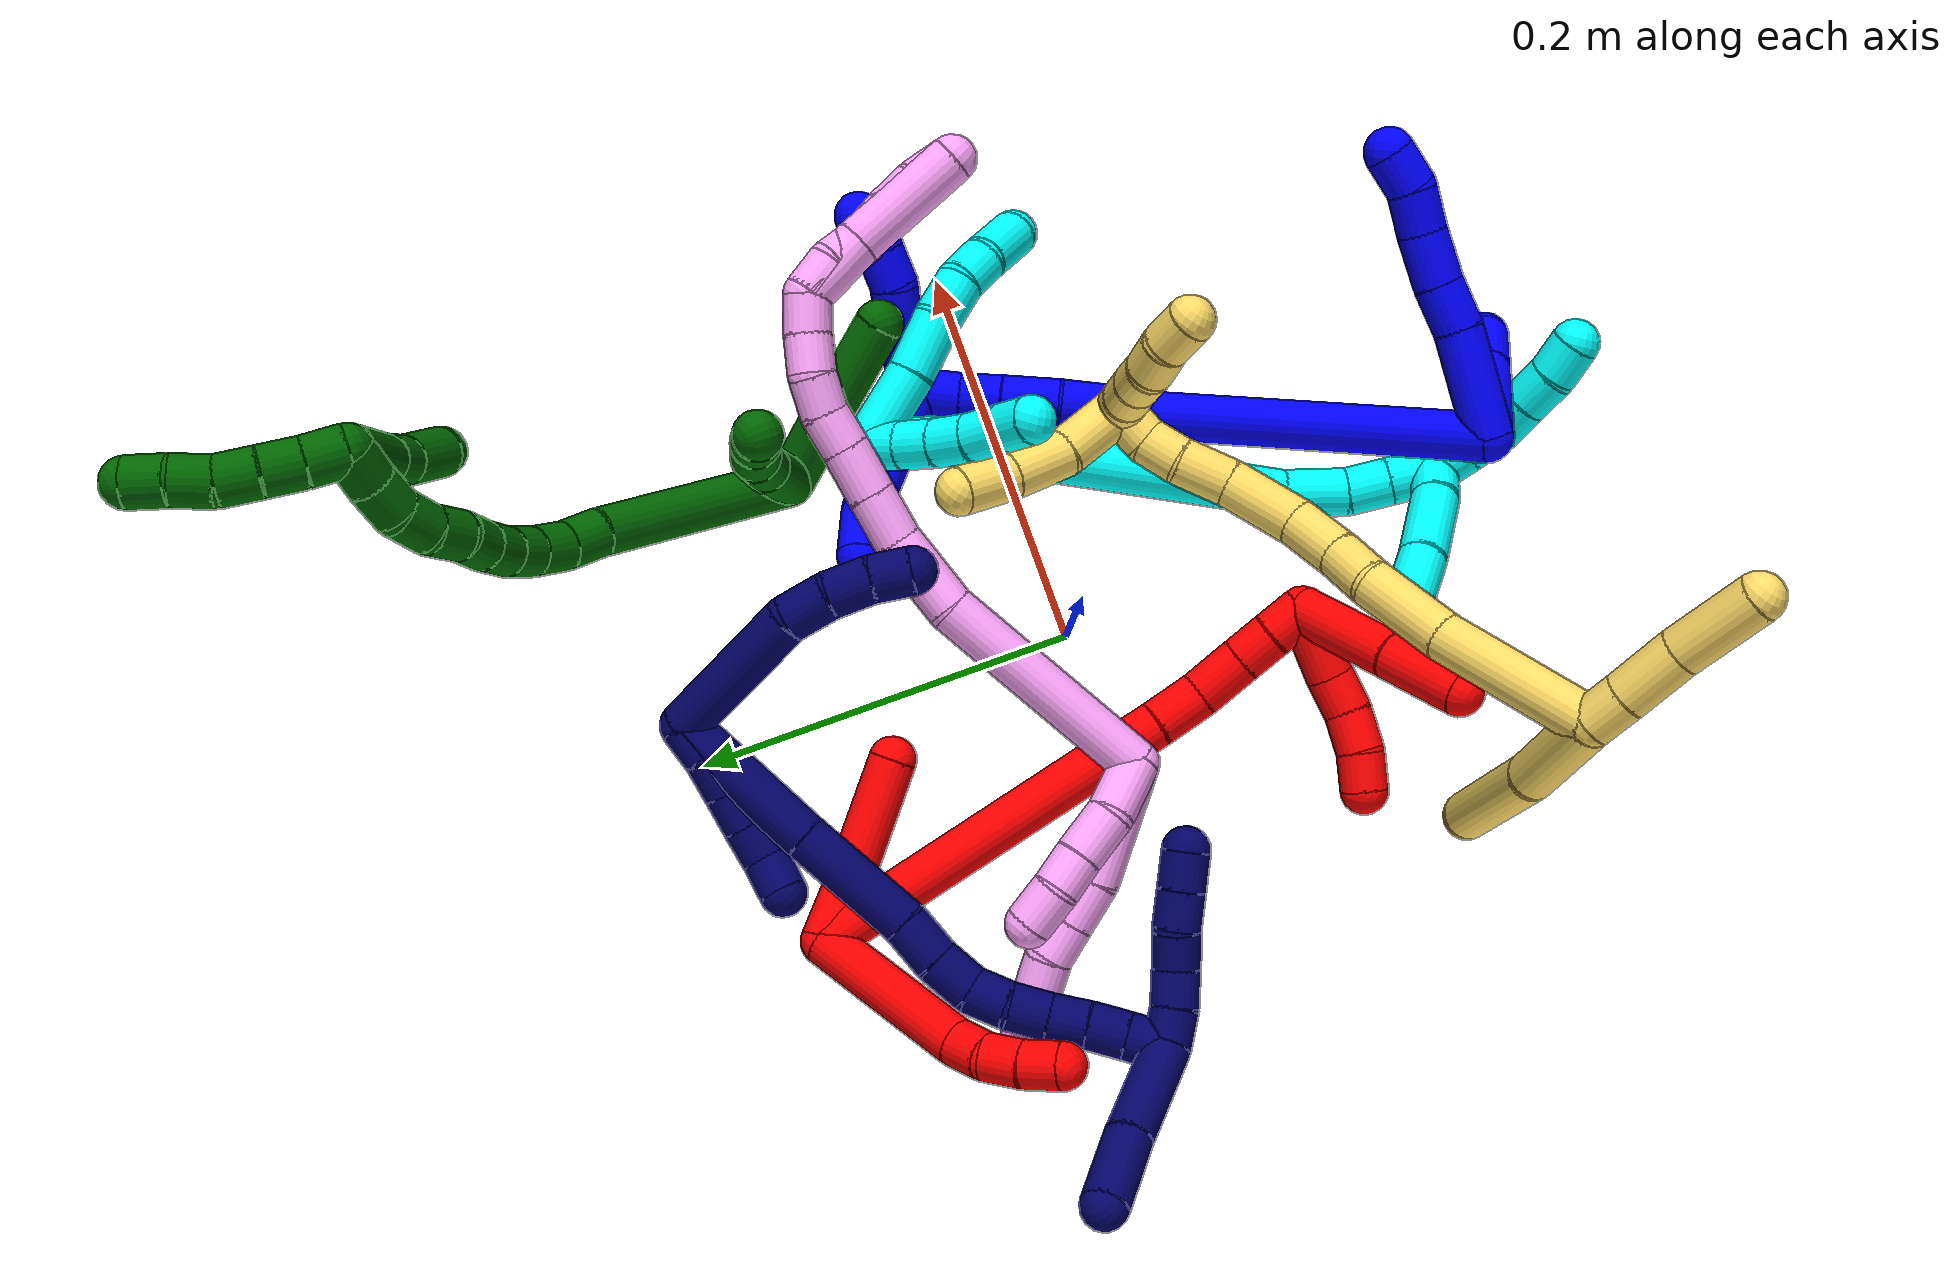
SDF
<sdf version="1.7">
 <world name="default">
  <plugin name="TubeGeneratorPlugin" filename="libtube_generator_plugin.so"/>
  <model name="photoneo_s_sensor">
   <static>1</static>
   <pose>0 0 2 1.57079 1.57079 3.14159</pose>
   <link name="link">
    <inertial><mass>0.1</mass></inertial>
    <sensor name="sensor" type="depth">
     <update_rate>30</update_rate>
     <camera>
      <horizontal_fov>1.22</horizontal_fov>
      <image><width>1920</width><height>1200</height><format>B8G8R8</format></image>
      <clip><near>0.1</near><far>4</far></clip>
      <depth_camera><output>points</output></depth_camera>
     </camera>
     <plugin name="camera_plugin" filename="libgazebo_ros_depth_camera.so">
      <baseline>0.2</baseline>
      <alwaysOn>1</alwaysOn>
      <updateRate>0.0</updateRate>
      <cameraName>camera_ir</cameraName>
      <imageTopicName>/camera/color/image_raw</imageTopicName>
      <cameraInfoTopicName>/camera/color/camera_info</cameraInfoTopicName>
      <depthImageTopicName>/camera/depth/image_raw</depthImageTopicName>
      <depthImageCameraInfoTopicName>/camera/depth/camera_info</depthImageCameraInfoTopicName>
      <pointCloudTopicName>/camera/depth/points</pointCloudTopicName>
      <frameName>fr_optical</frameName>
      <pointCloudCutoff>0.1</pointCloudCutoff>
      <pointCloudCutoffMax>2.0</pointCloudCutoffMax>
      <distortionK1>0</distortionK1>
      <distortionK2>0</distortionK2>
      <distortionK3>0</distortionK3>
      <distortionT1>0</distortionT1>
      <distortionT2>0</distortionT2>
      <CxPrime>0</CxPrime>
      <Cx>0</Cx>
      <Cy>0</Cy>
      <focalLength>0</focalLength>
      <hackBaseline>0</hackBaseline>
     </plugin>
    </sensor>
   </link>
  </model>
  <gravity>0 0 -9.8</gravity>
  <magnetic_field>6e-06 2.3e-05 -4.2e-05</magnetic_field>
  <atmosphere type="adiabatic"/>
  <physics name="default_physics" default="0" type="ode">
   <max_step_size>0.003</max_step_size>
   <real_time_factor>1</real_time_factor>
   <real_time_update_rate>1000</real_time_update_rate>
   <max_contacts>10000</max_contacts>
   <ode>
    <solver>
     <type>quick</type>
     <iters>100</iters>
     <sor>1.3</sor>
     <use_dynamic_moi_rescaling>0</use_dynamic_moi_rescaling>
    </solver>
    <constraints>
     <contact_max_correcting_vel>0</contact_max_correcting_vel>
     <contact_surface_layer>0.001</contact_surface_layer>
     <cfm>0</cfm>
     <erp>0.2</erp>
    </constraints>
   </ode>
  </physics>
  <scene><ambient>0.4 0.4 0.4 1</ambient><background>0.7 0.7 0.7 1</background><shadows>0</shadows></scene>
  <audio><device>default</device></audio>
  <spherical_coordinates>
   <surface_model>EARTH_WGS84</surface_model>
   <latitude_deg>0</latitude_deg>
   <longitude_deg>0</longitude_deg>
   <elevation>0</elevation>
   <heading_deg>0</heading_deg>
  </spherical_coordinates>
  <model name="bin">
   <static>1</static>
   <link name="bottom">
    <collision name="collision-bottom">
     <pose>0 0 -0.01 0 -0 0</pose>
     <geometry><box><size>0.8 0.6 0.02</size></box></geometry>
     <surface>
      <friction><ode><mu>100</mu><mu2>100</mu2></ode></friction>
      <contact><collide_bitmask>65535</collide_bitmask></contact>
     </surface>
    </collision>
   </link>
   <link name="west_wall">
    <collision name="collision-west_wall">
     <pose>-0.41 0 0.1 0 -0 0</pose>
     <geometry><box><size>0.02 0.6 0.2</size></box></geometry>
     <surface>
      <friction><ode><mu>100</mu><mu2>100</mu2></ode></friction>
      <contact><collide_bitmask>65535</collide_bitmask></contact>
     </surface>
    </collision>
   </link>
   <link name="east_wall">
    <collision name="collision-east_wall">
     <pose>0.41 0 0.1 0 -0 0</pose>
     <geometry><box><size>0.02 0.6 0.2</size></box></geometry>
     <surface>
      <friction><ode><mu>100</mu><mu2>100</mu2></ode></friction>
      <contact><collide_bitmask>65535</collide_bitmask></contact>
     </surface>
    </collision>
   </link>
   <link name="south_wall">
    <collision name="collision-south_wall">
     <pose>0 -0.31 0.1 0 -0 0</pose>
     <geometry><box><size>0.8 0.02 0.2</size></box></geometry>
     <surface>
      <friction><ode><mu>100</mu><mu2>100</mu2></ode></friction>
      <contact><collide_bitmask>65535</collide_bitmask></contact>
     </surface>
    </collision>
   </link>
   <link name="north_wall">
    <collision name="collision-north_wall">
     <pose>0 0.31 0.1 0 -0 0</pose>
     <geometry><box><size>0.8 0.02 0.2</size></box></geometry>
     <surface>
      <friction><ode><mu>100</mu><mu2>100</mu2></ode></friction>
      <contact><collide_bitmask>65535</collide_bitmask></contact>
     </surface>
    </collision>
   </link>
  </model>
  <model name="1">
   <static>0</static>
   <link name="1">
    <collision name="collision-cylinder-e_1_2_8">
     <pose>0.025704 0.003817 -0.009731 -2.76776 1.18454 -2.59357</pose>
     <geometry><cylinder><radius>0.0125</radius><length>0.055497</length></cylinder></geometry>
     <surface>
      <friction><ode><mu>1.16</mu><mu2>1.16</mu2><slip1>0</slip1><slip2>0</slip2></ode></friction>
      <contact><ode><kp>1e+06</kp><kd>1</kd><max_vel>0</max_vel><min_depth>0.001</min_depth></ode></contact>
     </surface>
    </collision>
    <visual name="visual-cylinder-e_1_2_8">
     <pose>0.025704 0.003817 -0.009731 -2.76776 1.18454 -2.59357</pose>
     <geometry><cylinder><radius>0.0125</radius><length>0.055497</length></cylinder></geometry>
     <material><ambient>0 0 1 1</ambient></material>
    </visual>
    <collision name="collision-cylinder-e_2_8_9">
     <pose>0.062046 0.010322 -0.025135 -2.69917 1.03773 -2.39126</pose>
     <geometry><cylinder><radius>0.0125</radius><length>0.024703</length></cylinder></geometry>
     <surface>
      <friction><ode><mu>1.16</mu><mu2>1.16</mu2><slip1>0</slip1><slip2>0</slip2></ode></friction>
      <contact><ode><kp>1e+06</kp><kd>1</kd><max_vel>0</max_vel><min_depth>0.001</min_depth></ode></contact>
     </surface>
    </collision>
    <visual name="visual-cylinder-e_2_8_9">
     <pose>0.062046 0.010322 -0.025135 -2.69917 1.03773 -2.39126</pose>
     <geometry><cylinder><radius>0.0125</radius><length>0.024703</length></cylinder></geometry>
     <material><ambient>0 0 1 1</ambient></material>
    </visual>
    <collision name="collision-cylinder-e_3_9_10">
     <pose>0.084919 0.016133 -0.035619 -2.56581 1.13241 -2.26964</pose>
     <geometry><cylinder><radius>0.0125</radius><length>0.027026</length></cylinder></geometry>
     <surface>
      <friction><ode><mu>1.16</mu><mu2>1.16</mu2><slip1>0</slip1><slip2>0</slip2></ode></friction>
      <contact><ode><kp>1e+06</kp><kd>1</kd><max_vel>0</max_vel><min_depth>0.001</min_depth></ode></contact>
     </surface>
    </collision>
    <visual name="visual-cylinder-e_3_9_10">
     <pose>0.084919 0.016133 -0.035619 -2.56581 1.13241 -2.26964</pose>
     <geometry><cylinder><radius>0.0125</radius><length>0.027026</length></cylinder></geometry>
     <material><ambient>0 0 1 1</ambient></material>
    </visual>
    <collision name="collision-cylinder-e_4_10_11">
     <pose>0.10721 0.022553 -0.043372 -2.29928 1.15679 -1.93887</pose>
     <geometry><cylinder><radius>0.0125</radius><length>0.021967</length></cylinder></geometry>
     <surface>
      <friction><ode><mu>1.16</mu><mu2>1.16</mu2><slip1>0</slip1><slip2>0</slip2></ode></friction>
      <contact><ode><kp>1e+06</kp><kd>1</kd><max_vel>0</max_vel><min_depth>0.001</min_depth></ode></contact>
     </surface>
    </collision>
    <visual name="visual-cylinder-e_4_10_11">
     <pose>0.10721 0.022553 -0.043372 -2.29928 1.15679 -1.93887</pose>
     <geometry><cylinder><radius>0.0125</radius><length>0.021967</length></cylinder></geometry>
     <material><ambient>0 0 1 1</ambient></material>
    </visual>
    <collision name="collision-cylinder-e_5_11_6">
     <pose>0.12527 0.029368 -0.051951 -2.58369 0.87796 -2.0461</pose>
     <geometry><cylinder><radius>0.0125</radius><length>0.020806</length></cylinder></geometry>
     <surface>
      <friction><ode><mu>1.16</mu><mu2>1.16</mu2><slip1>0</slip1><slip2>0</slip2></ode></friction>
      <contact><ode><kp>1e+06</kp><kd>1</kd><max_vel>0</max_vel><min_depth>0.001</min_depth></ode></contact>
     </surface>
    </collision>
    <visual name="visual-cylinder-e_5_11_6">
     <pose>0.12527 0.029368 -0.051951 -2.58369 0.87796 -2.0461</pose>
     <geometry><cylinder><radius>0.0125</radius><length>0.020806</length></cylinder></geometry>
     <material><ambient>0 0 1 1</ambient></material>
    </visual>
    <collision name="collision-cylinder-e_1_2_12">
     <pose>0.015697 -0.02689 -0.008458 1.87553 0.508083 0.680223</pose>
     <geometry><cylinder><radius>0.0125</radius><length>0.064528</length></cylinder></geometry>
     <surface>
      <friction><ode><mu>1.16</mu><mu2>1.16</mu2><slip1>0</slip1><slip2>0</slip2></ode></friction>
      <contact><ode><kp>1e+06</kp><kd>1</kd><max_vel>0</max_vel><min_depth>0.001</min_depth></ode></contact>
     </surface>
    </collision>
    <visual name="visual-cylinder-e_1_2_12">
     <pose>0.015697 -0.02689 -0.008458 1.87553 0.508083 0.680223</pose>
     <geometry><cylinder><radius>0.0125</radius><length>0.064528</length></cylinder></geometry>
     <material><ambient>0 0 1 1</ambient></material>
    </visual>
    <collision name="collision-cylinder-e_2_12_5">
     <pose>0.039922 -0.068585 -0.021671 1.88157 0.50165 0.675853</pose>
     <geometry><cylinder><radius>0.0125</radius><length>0.035472</length></cylinder></geometry>
     <surface>
      <friction><ode><mu>1.16</mu><mu2>1.16</mu2><slip1>0</slip1><slip2>0</slip2></ode></friction>
      <contact><ode><kp>1e+06</kp><kd>1</kd><max_vel>0</max_vel><min_depth>0.001</min_depth></ode></contact>
     </surface>
    </collision>
    <visual name="visual-cylinder-e_2_12_5">
     <pose>0.039922 -0.068585 -0.021671 1.88157 0.50165 0.675853</pose>
     <geometry><cylinder><radius>0.0125</radius><length>0.035472</length></cylinder></geometry>
     <material><ambient>0 0 1 1</ambient></material>
    </visual>
    <collision name="collision-cylinder-e_1_2_13">
     <pose>-0.003787 0.000859 -0.088516 -3.13189 -0.04276 2.69542</pose>
     <geometry><cylinder><radius>0.0125</radius><length>0.177203</length></cylinder></geometry>
     <surface>
      <friction><ode><mu>1.16</mu><mu2>1.16</mu2><slip1>0</slip1><slip2>0</slip2></ode></friction>
      <contact><ode><kp>1e+06</kp><kd>1</kd><max_vel>0</max_vel><min_depth>0.001</min_depth></ode></contact>
     </surface>
    </collision>
    <visual name="visual-cylinder-e_1_2_13">
     <pose>-0.003787 0.000859 -0.088516 -3.13189 -0.04276 2.69542</pose>
     <geometry><cylinder><radius>0.0125</radius><length>0.177203</length></cylinder></geometry>
     <material><ambient>0 0 1 1</ambient></material>
    </visual>
    <collision name="collision-cylinder-e_2_13_14">
     <pose>-0.006983 0.002458 -0.187059 -3.06789 0.058818 -1.34695</pose>
     <geometry><cylinder><radius>0.0125</radius><length>0.020141</length></cylinder></geometry>
     <surface>
      <friction><ode><mu>1.16</mu><mu2>1.16</mu2><slip1>0</slip1><slip2>0</slip2></ode></friction>
      <contact><ode><kp>1e+06</kp><kd>1</kd><max_vel>0</max_vel><min_depth>0.001</min_depth></ode></contact>
     </surface>
    </collision>
    <visual name="visual-cylinder-e_2_13_14">
     <pose>-0.006983 0.002458 -0.187059 -3.06789 0.058818 -1.34695</pose>
     <geometry><cylinder><radius>0.0125</radius><length>0.020141</length></cylinder></geometry>
     <material><ambient>0 0 1 1</ambient></material>
    </visual>
    <collision name="collision-cylinder-e_3_14_15">
     <pose>-0.0061 0.00836 -0.209367 -2.74376 0.021827 -0.108176</pose>
     <geometry><cylinder><radius>0.0125</radius><length>0.026652</length></cylinder></geometry>
     <surface>
      <friction><ode><mu>1.16</mu><mu2>1.16</mu2><slip1>0</slip1><slip2>0</slip2></ode></friction>
      <contact><ode><kp>1e+06</kp><kd>1</kd><max_vel>0</max_vel><min_depth>0.001</min_depth></ode></contact>
     </surface>
    </collision>
    <visual name="visual-cylinder-e_3_14_15">
     <pose>-0.0061 0.00836 -0.209367 -2.74376 0.021827 -0.108176</pose>
     <geometry><cylinder><radius>0.0125</radius><length>0.026652</length></cylinder></geometry>
     <material><ambient>0 0 1 1</ambient></material>
    </visual>
    <collision name="collision-cylinder-e_4_15_16">
     <pose>-0.006243 0.017549 -0.236107 -2.86992 -0.028905 0.21072</pose>
     <geometry><cylinder><radius>0.0125</radius><length>0.030029</length></cylinder></geometry>
     <surface>
      <friction><ode><mu>1.16</mu><mu2>1.16</mu2><slip1>0</slip1><slip2>0</slip2></ode></friction>
      <contact><ode><kp>1e+06</kp><kd>1</kd><max_vel>0</max_vel><min_depth>0.001</min_depth></ode></contact>
     </surface>
    </collision>
    <visual name="visual-cylinder-e_4_15_16">
     <pose>-0.006243 0.017549 -0.236107 -2.86992 -0.028905 0.21072</pose>
     <geometry><cylinder><radius>0.0125</radius><length>0.030029</length></cylinder></geometry>
     <material><ambient>0 0 1 1</ambient></material>
    </visual>
    <collision name="collision-cylinder-e_5_16_17">
     <pose>-0.007142 0.023949 -0.261535 -2.92854 -0.041346 0.382008</pose>
     <geometry><cylinder><radius>0.0125</radius><length>0.022469</length></cylinder></geometry>
     <surface>
      <friction><ode><mu>1.16</mu><mu2>1.16</mu2><slip1>0</slip1><slip2>0</slip2></ode></friction>
      <contact><ode><kp>1e+06</kp><kd>1</kd><max_vel>0</max_vel><min_depth>0.001</min_depth></ode></contact>
     </surface>
    </collision>
    <visual name="visual-cylinder-e_5_16_17">
     <pose>-0.007142 0.023949 -0.261535 -2.92854 -0.041346 0.382008</pose>
     <geometry><cylinder><radius>0.0125</radius><length>0.022469</length></cylinder></geometry>
     <material><ambient>0 0 1 1</ambient></material>
    </visual>
    <collision name="collision-cylinder-e_6_17_1">
     <pose>-0.007467 0.030801 -0.283372 -2.75063 0.011804 -0.059597</pose>
     <geometry><cylinder><radius>0.0125</radius><length>0.023506</length></cylinder></geometry>
     <surface>
      <friction><ode><mu>1.16</mu><mu2>1.16</mu2><slip1>0</slip1><slip2>0</slip2></ode></friction>
      <contact><ode><kp>1e+06</kp><kd>1</kd><max_vel>0</max_vel><min_depth>0.001</min_depth></ode></contact>
     </surface>
    </collision>
    <visual name="visual-cylinder-e_6_17_1">
     <pose>-0.007467 0.030801 -0.283372 -2.75063 0.011804 -0.059597</pose>
     <geometry><cylinder><radius>0.0125</radius><length>0.023506</length></cylinder></geometry>
     <material><ambient>0 0 1 1</ambient></material>
    </visual>
    <collision name="collision-cylinder-e_1_1_18">
     <pose>-0.038298 0.054276 -0.297051 -1.71783 -1.01575 1.1458</pose>
     <geometry><cylinder><radius>0.0125</radius><length>0.072881</length></cylinder></geometry>
     <surface>
      <friction><ode><mu>1.16</mu><mu2>1.16</mu2><slip1>0</slip1><slip2>0</slip2></ode></friction>
      <contact><ode><kp>1e+06</kp><kd>1</kd><max_vel>0</max_vel><min_depth>0.001</min_depth></ode></contact>
     </surface>
    </collision>
    <visual name="visual-cylinder-e_1_1_18">
     <pose>-0.038298 0.054276 -0.297051 -1.71783 -1.01575 1.1458</pose>
     <geometry><cylinder><radius>0.0125</radius><length>0.072881</length></cylinder></geometry>
     <material><ambient>0 0 1 1</ambient></material>
    </visual>
    <collision name="collision-cylinder-e_2_18_4">
     <pose>-0.079965 0.080934 -0.296584 -1.16629 -0.908928 0.623572</pose>
     <geometry><cylinder><radius>0.0125</radius><length>0.027119</length></cylinder></geometry>
     <surface>
      <friction><ode><mu>1.16</mu><mu2>1.16</mu2><slip1>0</slip1><slip2>0</slip2></ode></friction>
      <contact><ode><kp>1e+06</kp><kd>1</kd><max_vel>0</max_vel><min_depth>0.001</min_depth></ode></contact>
     </surface>
    </collision>
    <visual name="visual-cylinder-e_2_18_4">
     <pose>-0.079965 0.080934 -0.296584 -1.16629 -0.908928 0.623572</pose>
     <geometry><cylinder><radius>0.0125</radius><length>0.027119</length></cylinder></geometry>
     <material><ambient>0 0 1 1</ambient></material>
    </visual>
    <collision name="collision-cylinder-e_1_1_19">
     <pose>0.001761 0.038866 -0.296365 -2.10614 1.14068 -1.68941</pose>
     <geometry><cylinder><radius>0.0125</radius><length>0.02</length></cylinder></geometry>
     <surface>
      <friction><ode><mu>1.16</mu><mu2>1.16</mu2><slip1>0</slip1><slip2>0</slip2></ode></friction>
      <contact><ode><kp>1e+06</kp><kd>1</kd><max_vel>0</max_vel><min_depth>0.001</min_depth></ode></contact>
     </surface>
    </collision>
    <visual name="visual-cylinder-e_1_1_19">
     <pose>0.001761 0.038866 -0.296365 -2.10614 1.14068 -1.68941</pose>
     <geometry><cylinder><radius>0.0125</radius><length>0.02</length></cylinder></geometry>
     <material><ambient>0 0 1 1</ambient></material>
    </visual>
    <collision name="collision-cylinder-e_2_19_20">
     <pose>0.019394 0.047608 -0.299138 -1.69545 1.02445 -1.13456</pose>
     <geometry><cylinder><radius>0.0125</radius><length>0.02</length></cylinder></geometry>
     <surface>
      <friction><ode><mu>1.16</mu><mu2>1.16</mu2><slip1>0</slip1><slip2>0</slip2></ode></friction>
      <contact><ode><kp>1e+06</kp><kd>1</kd><max_vel>0</max_vel><min_depth>0.001</min_depth></ode></contact>
     </surface>
    </collision>
    <visual name="visual-cylinder-e_2_19_20">
     <pose>0.019394 0.047608 -0.299138 -1.69545 1.02445 -1.13456</pose>
     <geometry><cylinder><radius>0.0125</radius><length>0.02</length></cylinder></geometry>
     <material><ambient>0 0 1 1</ambient></material>
    </visual>
    <collision name="collision-cylinder-e_3_20_21">
     <pose>0.037273 0.05631 -0.300327 -1.72272 1.20381 -1.34962</pose>
     <geometry><cylinder><radius>0.0125</radius><length>0.02</length></cylinder></geometry>
     <surface>
      <friction><ode><mu>1.16</mu><mu2>1.16</mu2><slip1>0</slip1><slip2>0</slip2></ode></friction>
      <contact><ode><kp>1e+06</kp><kd>1</kd><max_vel>0</max_vel><min_depth>0.001</min_depth></ode></contact>
     </surface>
    </collision>
    <visual name="visual-cylinder-e_3_20_21">
     <pose>0.037273 0.05631 -0.300327 -1.72272 1.20381 -1.34962</pose>
     <geometry><cylinder><radius>0.0125</radius><length>0.02</length></cylinder></geometry>
     <material><ambient>0 0 1 1</ambient></material>
    </visual>
    <collision name="collision-cylinder-e_4_21_22">
     <pose>0.055297 0.06343 -0.304292 -2.33474 1.05322 -1.87498</pose>
     <geometry><cylinder><radius>0.0125</radius><length>0.02</length></cylinder></geometry>
     <surface>
      <friction><ode><mu>1.16</mu><mu2>1.16</mu2><slip1>0</slip1><slip2>0</slip2></ode></friction>
      <contact><ode><kp>1e+06</kp><kd>1</kd><max_vel>0</max_vel><min_depth>0.001</min_depth></ode></contact>
     </surface>
    </collision>
    <visual name="visual-cylinder-e_4_21_22">
     <pose>0.055297 0.06343 -0.304292 -2.33474 1.05322 -1.87498</pose>
     <geometry><cylinder><radius>0.0125</radius><length>0.02</length></cylinder></geometry>
     <material><ambient>0 0 1 1</ambient></material>
    </visual>
    <collision name="collision-cylinder-e_5_22_3">
     <pose>0.071931 0.069303 -0.313336 -2.7532 0.918071 -2.38416</pose>
     <geometry><cylinder><radius>0.0125</radius><length>0.02</length></cylinder></geometry>
     <surface>
      <friction><ode><mu>1.16</mu><mu2>1.16</mu2><slip1>0</slip1><slip2>0</slip2></ode></friction>
      <contact><ode><kp>1e+06</kp><kd>1</kd><max_vel>0</max_vel><min_depth>0.001</min_depth></ode></contact>
     </surface>
    </collision>
    <visual name="visual-cylinder-e_5_22_3">
     <pose>0.071931 0.069303 -0.313336 -2.7532 0.918071 -2.38416</pose>
     <geometry><cylinder><radius>0.0125</radius><length>0.02</length></cylinder></geometry>
     <material><ambient>0 0 1 1</ambient></material>
    </visual>
    <collision name="collision-sphere-3">
     <pose>0.079876 0.071603 -0.318958 0 -0 0</pose>
     <geometry><sphere><radius>0.0125</radius></sphere></geometry>
     <surface>
      <friction><ode><mu>1.16</mu><mu2>1.16</mu2><slip1>0</slip1><slip2>0</slip2></ode></friction>
      <contact><ode><kp>1e+06</kp><kd>1</kd><max_vel>0</max_vel><min_depth>0.001</min_depth></ode></contact>
     </surface>
    </collision>
    <visual name="visual-sphere-3">
     <pose>0.079876 0.071603 -0.318958 0 -0 0</pose>
     <geometry><sphere><radius>0.0125</radius></sphere></geometry>
     <material><ambient>0 0 1 1</ambient></material>
    </visual>
    <collision name="collision-sphere-22">
     <pose>0.063987 0.067003 -0.307715 0 -0 0</pose>
     <geometry><sphere><radius>0.0125</radius></sphere></geometry>
     <surface>
      <friction><ode><mu>1.16</mu><mu2>1.16</mu2><slip1>0</slip1><slip2>0</slip2></ode></friction>
      <contact><ode><kp>1e+06</kp><kd>1</kd><max_vel>0</max_vel><min_depth>0.001</min_depth></ode></contact>
     </surface>
    </collision>
    <visual name="visual-sphere-22">
     <pose>0.063987 0.067003 -0.307715 0 -0 0</pose>
     <geometry><sphere><radius>0.0125</radius></sphere></geometry>
     <material><ambient>0 0 1 1</ambient></material>
    </visual>
    <collision name="collision-sphere-21">
     <pose>0.046607 0.059857 -0.30087 0 -0 0</pose>
     <geometry><sphere><radius>0.0125</radius></sphere></geometry>
     <surface>
      <friction><ode><mu>1.16</mu><mu2>1.16</mu2><slip1>0</slip1><slip2>0</slip2></ode></friction>
      <contact><ode><kp>1e+06</kp><kd>1</kd><max_vel>0</max_vel><min_depth>0.001</min_depth></ode></contact>
     </surface>
    </collision>
    <visual name="visual-sphere-21">
     <pose>0.046607 0.059857 -0.30087 0 -0 0</pose>
     <geometry><sphere><radius>0.0125</radius></sphere></geometry>
     <material><ambient>0 0 1 1</ambient></material>
    </visual>
    <collision name="collision-sphere-20">
     <pose>0.027938 0.052763 -0.299784 0 -0 0</pose>
     <geometry><sphere><radius>0.0125</radius></sphere></geometry>
     <surface>
      <friction><ode><mu>1.16</mu><mu2>1.16</mu2><slip1>0</slip1><slip2>0</slip2></ode></friction>
      <contact><ode><kp>1e+06</kp><kd>1</kd><max_vel>0</max_vel><min_depth>0.001</min_depth></ode></contact>
     </surface>
    </collision>
    <visual name="visual-sphere-20">
     <pose>0.027938 0.052763 -0.299784 0 -0 0</pose>
     <geometry><sphere><radius>0.0125</radius></sphere></geometry>
     <material><ambient>0 0 1 1</ambient></material>
    </visual>
    <collision name="collision-sphere-19">
     <pose>0.01085 0.042453 -0.298492 0 -0 0</pose>
     <geometry><sphere><radius>0.0125</radius></sphere></geometry>
     <surface>
      <friction><ode><mu>1.16</mu><mu2>1.16</mu2><slip1>0</slip1><slip2>0</slip2></ode></friction>
      <contact><ode><kp>1e+06</kp><kd>1</kd><max_vel>0</max_vel><min_depth>0.001</min_depth></ode></contact>
     </surface>
    </collision>
    <visual name="visual-sphere-19">
     <pose>0.01085 0.042453 -0.298492 0 -0 0</pose>
     <geometry><sphere><radius>0.0125</radius></sphere></geometry>
     <material><ambient>0 0 1 1</ambient></material>
    </visual>
    <collision name="collision-sphere-6">
     <pose>0.133275 0.032886 -0.057588 0 -0 0</pose>
     <geometry><sphere><radius>0.0125</radius></sphere></geometry>
     <surface>
      <friction><ode><mu>1.16</mu><mu2>1.16</mu2><slip1>0</slip1><slip2>0</slip2></ode></friction>
      <contact><ode><kp>1e+06</kp><kd>1</kd><max_vel>0</max_vel><min_depth>0.001</min_depth></ode></contact>
     </surface>
    </collision>
    <visual name="visual-sphere-6">
     <pose>0.133275 0.032886 -0.057588 0 -0 0</pose>
     <geometry><sphere><radius>0.0125</radius></sphere></geometry>
     <material><ambient>0 0 1 1</ambient></material>
    </visual>
    <collision name="collision-sphere-11">
     <pose>0.117266 0.02585 -0.046313 0 -0 0</pose>
     <geometry><sphere><radius>0.0125</radius></sphere></geometry>
     <surface>
      <friction><ode><mu>1.16</mu><mu2>1.16</mu2><slip1>0</slip1><slip2>0</slip2></ode></friction>
      <contact><ode><kp>1e+06</kp><kd>1</kd><max_vel>0</max_vel><min_depth>0.001</min_depth></ode></contact>
     </surface>
    </collision>
    <visual name="visual-sphere-11">
     <pose>0.117266 0.02585 -0.046313 0 -0 0</pose>
     <geometry><sphere><radius>0.0125</radius></sphere></geometry>
     <material><ambient>0 0 1 1</ambient></material>
    </visual>
    <collision name="collision-sphere-10">
     <pose>0.097154 0.019256 -0.04043 0 -0 0</pose>
     <geometry><sphere><radius>0.0125</radius></sphere></geometry>
     <surface>
      <friction><ode><mu>1.16</mu><mu2>1.16</mu2><slip1>0</slip1><slip2>0</slip2></ode></friction>
      <contact><ode><kp>1e+06</kp><kd>1</kd><max_vel>0</max_vel><min_depth>0.001</min_depth></ode></contact>
     </surface>
    </collision>
    <visual name="visual-sphere-10">
     <pose>0.097154 0.019256 -0.04043 0 -0 0</pose>
     <geometry><sphere><radius>0.0125</radius></sphere></geometry>
     <material><ambient>0 0 1 1</ambient></material>
    </visual>
    <collision name="collision-sphere-9">
     <pose>0.072684 0.01301 -0.030808 0 -0 0</pose>
     <geometry><sphere><radius>0.0125</radius></sphere></geometry>
     <surface>
      <friction><ode><mu>1.16</mu><mu2>1.16</mu2><slip1>0</slip1><slip2>0</slip2></ode></friction>
      <contact><ode><kp>1e+06</kp><kd>1</kd><max_vel>0</max_vel><min_depth>0.001</min_depth></ode></contact>
     </surface>
    </collision>
    <visual name="visual-sphere-9">
     <pose>0.072684 0.01301 -0.030808 0 -0 0</pose>
     <geometry><sphere><radius>0.0125</radius></sphere></geometry>
     <material><ambient>0 0 1 1</ambient></material>
    </visual>
    <collision name="collision-sphere-2">
     <geometry><sphere><radius>0.0125</radius></sphere></geometry>
     <surface>
      <friction><ode><mu>1.16</mu><mu2>1.16</mu2><slip1>0</slip1><slip2>0</slip2></ode></friction>
      <contact><ode><kp>1e+06</kp><kd>1</kd><max_vel>0</max_vel><min_depth>0.001</min_depth></ode></contact>
     </surface>
    </collision>
    <visual name="visual-sphere-2">
     <geometry><sphere><radius>0.0125</radius></sphere></geometry>
     <material><ambient>0 0 1 1</ambient></material>
    </visual>
    <collision name="collision-sphere-8">
     <pose>0.051408 0.007635 -0.019463 0 -0 0</pose>
     <geometry><sphere><radius>0.0125</radius></sphere></geometry>
     <surface>
      <friction><ode><mu>1.16</mu><mu2>1.16</mu2><slip1>0</slip1><slip2>0</slip2></ode></friction>
      <contact><ode><kp>1e+06</kp><kd>1</kd><max_vel>0</max_vel><min_depth>0.001</min_depth></ode></contact>
     </surface>
    </collision>
    <visual name="visual-sphere-8">
     <pose>0.051408 0.007635 -0.019463 0 -0 0</pose>
     <geometry><sphere><radius>0.0125</radius></sphere></geometry>
     <material><ambient>0 0 1 1</ambient></material>
    </visual>
    <collision name="collision-sphere-12">
     <pose>0.031393 -0.05378 -0.016916 0 -0 0</pose>
     <geometry><sphere><radius>0.0125</radius></sphere></geometry>
     <surface>
      <friction><ode><mu>1.16</mu><mu2>1.16</mu2><slip1>0</slip1><slip2>0</slip2></ode></friction>
      <contact><ode><kp>1e+06</kp><kd>1</kd><max_vel>0</max_vel><min_depth>0.001</min_depth></ode></contact>
     </surface>
    </collision>
    <visual name="visual-sphere-12">
     <pose>0.031393 -0.05378 -0.016916 0 -0 0</pose>
     <geometry><sphere><radius>0.0125</radius></sphere></geometry>
     <material><ambient>0 0 1 1</ambient></material>
    </visual>
    <collision name="collision-sphere-5">
     <pose>0.048451 -0.083391 -0.026426 0 -0 0</pose>
     <geometry><sphere><radius>0.0125</radius></sphere></geometry>
     <surface>
      <friction><ode><mu>1.16</mu><mu2>1.16</mu2><slip1>0</slip1><slip2>0</slip2></ode></friction>
      <contact><ode><kp>1e+06</kp><kd>1</kd><max_vel>0</max_vel><min_depth>0.001</min_depth></ode></contact>
     </surface>
    </collision>
    <visual name="visual-sphere-5">
     <pose>0.048451 -0.083391 -0.026426 0 -0 0</pose>
     <geometry><sphere><radius>0.0125</radius></sphere></geometry>
     <material><ambient>0 0 1 1</ambient></material>
    </visual>
    <collision name="collision-sphere-13">
     <pose>-0.007575 0.001718 -0.177033 0 -0 0</pose>
     <geometry><sphere><radius>0.0125</radius></sphere></geometry>
     <surface>
      <friction><ode><mu>1.16</mu><mu2>1.16</mu2><slip1>0</slip1><slip2>0</slip2></ode></friction>
      <contact><ode><kp>1e+06</kp><kd>1</kd><max_vel>0</max_vel><min_depth>0.001</min_depth></ode></contact>
     </surface>
    </collision>
    <visual name="visual-sphere-13">
     <pose>-0.007575 0.001718 -0.177033 0 -0 0</pose>
     <geometry><sphere><radius>0.0125</radius></sphere></geometry>
     <material><ambient>0 0 1 1</ambient></material>
    </visual>
    <collision name="collision-sphere-14">
     <pose>-0.006391 0.003198 -0.197084 0 -0 0</pose>
     <geometry><sphere><radius>0.0125</radius></sphere></geometry>
     <surface>
      <friction><ode><mu>1.16</mu><mu2>1.16</mu2><slip1>0</slip1><slip2>0</slip2></ode></friction>
      <contact><ode><kp>1e+06</kp><kd>1</kd><max_vel>0</max_vel><min_depth>0.001</min_depth></ode></contact>
     </surface>
    </collision>
    <visual name="visual-sphere-14">
     <pose>-0.006391 0.003198 -0.197084 0 -0 0</pose>
     <geometry><sphere><radius>0.0125</radius></sphere></geometry>
     <material><ambient>0 0 1 1</ambient></material>
    </visual>
    <collision name="collision-sphere-15">
     <pose>-0.005809 0.013521 -0.221649 0 -0 0</pose>
     <geometry><sphere><radius>0.0125</radius></sphere></geometry>
     <surface>
      <friction><ode><mu>1.16</mu><mu2>1.16</mu2><slip1>0</slip1><slip2>0</slip2></ode></friction>
      <contact><ode><kp>1e+06</kp><kd>1</kd><max_vel>0</max_vel><min_depth>0.001</min_depth></ode></contact>
     </surface>
    </collision>
    <visual name="visual-sphere-15">
     <pose>-0.005809 0.013521 -0.221649 0 -0 0</pose>
     <geometry><sphere><radius>0.0125</radius></sphere></geometry>
     <material><ambient>0 0 1 1</ambient></material>
    </visual>
    <collision name="collision-sphere-16">
     <pose>-0.006677 0.021576 -0.250564 0 -0 0</pose>
     <geometry><sphere><radius>0.0125</radius></sphere></geometry>
     <surface>
      <friction><ode><mu>1.16</mu><mu2>1.16</mu2><slip1>0</slip1><slip2>0</slip2></ode></friction>
      <contact><ode><kp>1e+06</kp><kd>1</kd><max_vel>0</max_vel><min_depth>0.001</min_depth></ode></contact>
     </surface>
    </collision>
    <visual name="visual-sphere-16">
     <pose>-0.006677 0.021576 -0.250564 0 -0 0</pose>
     <geometry><sphere><radius>0.0125</radius></sphere></geometry>
     <material><ambient>0 0 1 1</ambient></material>
    </visual>
    <collision name="collision-sphere-17">
     <pose>-0.007606 0.026323 -0.272506 0 -0 0</pose>
     <geometry><sphere><radius>0.0125</radius></sphere></geometry>
     <surface>
      <friction><ode><mu>1.16</mu><mu2>1.16</mu2><slip1>0</slip1><slip2>0</slip2></ode></friction>
      <contact><ode><kp>1e+06</kp><kd>1</kd><max_vel>0</max_vel><min_depth>0.001</min_depth></ode></contact>
     </surface>
    </collision>
    <visual name="visual-sphere-17">
     <pose>-0.007606 0.026323 -0.272506 0 -0 0</pose>
     <geometry><sphere><radius>0.0125</radius></sphere></geometry>
     <material><ambient>0 0 1 1</ambient></material>
    </visual>
    <collision name="collision-sphere-1">
     <pose>-0.007328 0.03528 -0.294237 0 -0 0</pose>
     <geometry><sphere><radius>0.0125</radius></sphere></geometry>
     <surface>
      <friction><ode><mu>1.16</mu><mu2>1.16</mu2><slip1>0</slip1><slip2>0</slip2></ode></friction>
      <contact><ode><kp>1e+06</kp><kd>1</kd><max_vel>0</max_vel><min_depth>0.001</min_depth></ode></contact>
     </surface>
    </collision>
    <visual name="visual-sphere-1">
     <pose>-0.007328 0.03528 -0.294237 0 -0 0</pose>
     <geometry><sphere><radius>0.0125</radius></sphere></geometry>
     <material><ambient>0 0 1 1</ambient></material>
    </visual>
    <collision name="collision-sphere-18">
     <pose>-0.069268 0.073273 -0.299864 0 -0 0</pose>
     <geometry><sphere><radius>0.0125</radius></sphere></geometry>
     <surface>
      <friction><ode><mu>1.16</mu><mu2>1.16</mu2><slip1>0</slip1><slip2>0</slip2></ode></friction>
      <contact><ode><kp>1e+06</kp><kd>1</kd><max_vel>0</max_vel><min_depth>0.001</min_depth></ode></contact>
     </surface>
    </collision>
    <visual name="visual-sphere-18">
     <pose>-0.069268 0.073273 -0.299864 0 -0 0</pose>
     <geometry><sphere><radius>0.0125</radius></sphere></geometry>
     <material><ambient>0 0 1 1</ambient></material>
    </visual>
    <collision name="collision-sphere-4">
     <pose>-0.090661 0.088595 -0.293305 0 -0 0</pose>
     <geometry><sphere><radius>0.0125</radius></sphere></geometry>
     <surface>
      <friction><ode><mu>1.16</mu><mu2>1.16</mu2><slip1>0</slip1><slip2>0</slip2></ode></friction>
      <contact><ode><kp>1e+06</kp><kd>1</kd><max_vel>0</max_vel><min_depth>0.001</min_depth></ode></contact>
     </surface>
    </collision>
    <visual name="visual-sphere-4">
     <pose>-0.090661 0.088595 -0.293305 0 -0 0</pose>
     <geometry><sphere><radius>0.0125</radius></sphere></geometry>
     <material><ambient>0 0 1 1</ambient></material>
    </visual>
    <inertial>
     <pose>0.0132 0.015621 -0.146792 0 -0 0</pose>
     <mass>0.75</mass>
     <inertia>
      <ixx>-0.000152</ixx>
      <ixy>0</ixy>
      <ixz>0</ixz>
      <iyy>0.000706</iyy>
      <iyz>0</iyz>
      <izz>-3.2e-05</izz>
     </inertia>
    </inertial>
   </link>
   <pose>0.016148 -0.22468 0.087397 1.19291 -0.220368 -0.439204</pose>
  </model>
  <model name="2">
   <static>0</static>
   <link name="2">
    <collision name="collision-cylinder-e_1_2_8">
     <pose>-0.013784 -0.005805 0.041976 0.137424 -0.314481 -0.021822</pose>
     <geometry><cylinder><radius>0.0125</radius><length>0.089122</length></cylinder></geometry>
     <surface>
      <friction><ode><mu>1.16</mu><mu2>1.16</mu2><slip1>0</slip1><slip2>0</slip2></ode></friction>
      <contact><ode><kp>1e+06</kp><kd>1</kd><max_vel>0</max_vel><min_depth>0.001</min_depth></ode></contact>
     </surface>
    </collision>
    <visual name="visual-cylinder-e_1_2_8">
     <pose>-0.013784 -0.005805 0.041976 0.137424 -0.314481 -0.021822</pose>
     <geometry><cylinder><radius>0.0125</radius><length>0.089122</length></cylinder></geometry>
     <material><ambient>1 0 0 1</ambient></material>
    </visual>
    <collision name="collision-cylinder-e_2_8_9">
     <pose>-0.027379 -0.013169 0.093841 0.156313 0.018838 0.001475</pose>
     <geometry><cylinder><radius>0.0125</radius><length>0.020024</length></cylinder></geometry>
     <surface>
      <friction><ode><mu>1.16</mu><mu2>1.16</mu2><slip1>0</slip1><slip2>0</slip2></ode></friction>
      <contact><ode><kp>1e+06</kp><kd>1</kd><max_vel>0</max_vel><min_depth>0.001</min_depth></ode></contact>
     </surface>
    </collision>
    <visual name="visual-cylinder-e_2_8_9">
     <pose>-0.027379 -0.013169 0.093841 0.156313 0.018838 0.001475</pose>
     <geometry><cylinder><radius>0.0125</radius><length>0.020024</length></cylinder></geometry>
     <material><ambient>1 0 0 1</ambient></material>
    </visual>
    <collision name="collision-cylinder-e_3_9_10">
     <pose>-0.027539 -0.019331 0.112832 0.468267 -0.034219 -0.008162</pose>
     <geometry><cylinder><radius>0.0125</radius><length>0.020414</length></cylinder></geometry>
     <surface>
      <friction><ode><mu>1.16</mu><mu2>1.16</mu2><slip1>0</slip1><slip2>0</slip2></ode></friction>
      <contact><ode><kp>1e+06</kp><kd>1</kd><max_vel>0</max_vel><min_depth>0.001</min_depth></ode></contact>
     </surface>
    </collision>
    <visual name="visual-cylinder-e_3_9_10">
     <pose>-0.027539 -0.019331 0.112832 0.468267 -0.034219 -0.008162</pose>
     <geometry><cylinder><radius>0.0125</radius><length>0.020414</length></cylinder></geometry>
     <material><ambient>1 0 0 1</ambient></material>
    </visual>
    <collision name="collision-cylinder-e_4_10_6">
     <pose>-0.02749 -0.029682 0.130376 0.597691 0.039002 0.012017</pose>
     <geometry><cylinder><radius>0.0125</radius><length>0.02044</length></cylinder></geometry>
     <surface>
      <friction><ode><mu>1.16</mu><mu2>1.16</mu2><slip1>0</slip1><slip2>0</slip2></ode></friction>
      <contact><ode><kp>1e+06</kp><kd>1</kd><max_vel>0</max_vel><min_depth>0.001</min_depth></ode></contact>
     </surface>
    </collision>
    <visual name="visual-cylinder-e_4_10_6">
     <pose>-0.02749 -0.029682 0.130376 0.597691 0.039002 0.012017</pose>
     <geometry><cylinder><radius>0.0125</radius><length>0.02044</length></cylinder></geometry>
     <material><ambient>1 0 0 1</ambient></material>
    </visual>
    <collision name="collision-cylinder-e_1_2_11">
     <pose>0.006928 -0.013849 -0.004792 1.90394 0.441644 0.610727</pose>
     <geometry><cylinder><radius>0.0125</radius><length>0.032419</length></cylinder></geometry>
     <surface>
      <friction><ode><mu>1.16</mu><mu2>1.16</mu2><slip1>0</slip1><slip2>0</slip2></ode></friction>
      <contact><ode><kp>1e+06</kp><kd>1</kd><max_vel>0</max_vel><min_depth>0.001</min_depth></ode></contact>
     </surface>
    </collision>
    <visual name="visual-cylinder-e_1_2_11">
     <pose>0.006928 -0.013849 -0.004792 1.90394 0.441644 0.610727</pose>
     <geometry><cylinder><radius>0.0125</radius><length>0.032419</length></cylinder></geometry>
     <material><ambient>1 0 0 1</ambient></material>
    </visual>
    <collision name="collision-cylinder-e_2_11_5">
     <pose>0.034687 -0.053637 -0.015504 1.79514 0.664219 0.816324</pose>
     <geometry><cylinder><radius>0.0125</radius><length>0.067581</length></cylinder></geometry>
     <surface>
      <friction><ode><mu>1.16</mu><mu2>1.16</mu2><slip1>0</slip1><slip2>0</slip2></ode></friction>
      <contact><ode><kp>1e+06</kp><kd>1</kd><max_vel>0</max_vel><min_depth>0.001</min_depth></ode></contact>
     </surface>
    </collision>
    <visual name="visual-cylinder-e_2_11_5">
     <pose>0.034687 -0.053637 -0.015504 1.79514 0.664219 0.816324</pose>
     <geometry><cylinder><radius>0.0125</radius><length>0.067581</length></cylinder></geometry>
     <material><ambient>1 0 0 1</ambient></material>
    </visual>
    <collision name="collision-cylinder-e_1_2_12">
     <pose>0.020097 -0.095782 0.028031 1.2861 0.198713 0.149109</pose>
     <geometry><cylinder><radius>0.0125</radius><length>0.203606</length></cylinder></geometry>
     <surface>
      <friction><ode><mu>1.16</mu><mu2>1.16</mu2><slip1>0</slip1><slip2>0</slip2></ode></friction>
      <contact><ode><kp>1e+06</kp><kd>1</kd><max_vel>0</max_vel><min_depth>0.001</min_depth></ode></contact>
     </surface>
    </collision>
    <visual name="visual-cylinder-e_1_2_12">
     <pose>0.020097 -0.095782 0.028031 1.2861 0.198713 0.149109</pose>
     <geometry><cylinder><radius>0.0125</radius><length>0.203606</length></cylinder></geometry>
     <material><ambient>1 0 0 1</ambient></material>
    </visual>
    <collision name="collision-cylinder-e_2_12_13">
     <pose>0.042675 -0.204762 0.059144 1.34133 0.18107 0.143796</pose>
     <geometry><cylinder><radius>0.0125</radius><length>0.027556</length></cylinder></geometry>
     <surface>
      <friction><ode><mu>1.16</mu><mu2>1.16</mu2><slip1>0</slip1><slip2>0</slip2></ode></friction>
      <contact><ode><kp>1e+06</kp><kd>1</kd><max_vel>0</max_vel><min_depth>0.001</min_depth></ode></contact>
     </surface>
    </collision>
    <visual name="visual-cylinder-e_2_12_13">
     <pose>0.042675 -0.204762 0.059144 1.34133 0.18107 0.143796</pose>
     <geometry><cylinder><radius>0.0125</radius><length>0.027556</length></cylinder></geometry>
     <material><ambient>1 0 0 1</ambient></material>
    </visual>
    <collision name="collision-cylinder-e_3_13_14">
     <pose>0.051093 -0.229962 0.066892 1.20006 0.432049 0.298058</pose>
     <geometry><cylinder><radius>0.0125</radius><length>0.02836</length></cylinder></geometry>
     <surface>
      <friction><ode><mu>1.16</mu><mu2>1.16</mu2><slip1>0</slip1><slip2>0</slip2></ode></friction>
      <contact><ode><kp>1e+06</kp><kd>1</kd><max_vel>0</max_vel><min_depth>0.001</min_depth></ode></contact>
     </surface>
    </collision>
    <visual name="visual-cylinder-e_3_13_14">
     <pose>0.051093 -0.229962 0.066892 1.20006 0.432049 0.298058</pose>
     <geometry><cylinder><radius>0.0125</radius><length>0.02836</length></cylinder></geometry>
     <material><ambient>1 0 0 1</ambient></material>
    </visual>
    <collision name="collision-cylinder-e_4_14_15">
     <pose>0.061254 -0.250411 0.075022 1.18155 0.433189 0.293046</pose>
     <geometry><cylinder><radius>0.0125</radius><length>0.020119</length></cylinder></geometry>
     <surface>
      <friction><ode><mu>1.16</mu><mu2>1.16</mu2><slip1>0</slip1><slip2>0</slip2></ode></friction>
      <contact><ode><kp>1e+06</kp><kd>1</kd><max_vel>0</max_vel><min_depth>0.001</min_depth></ode></contact>
     </surface>
    </collision>
    <visual name="visual-cylinder-e_4_14_15">
     <pose>0.061254 -0.250411 0.075022 1.18155 0.433189 0.293046</pose>
     <geometry><cylinder><radius>0.0125</radius><length>0.020119</length></cylinder></geometry>
     <material><ambient>1 0 0 1</ambient></material>
    </visual>
    <collision name="collision-cylinder-e_5_15_1">
     <pose>0.069429 -0.26767 0.081706 1.22056 0.398751 0.280757</pose>
     <geometry><cylinder><radius>0.0125</radius><length>0.020359</length></cylinder></geometry>
     <surface>
      <friction><ode><mu>1.16</mu><mu2>1.16</mu2><slip1>0</slip1><slip2>0</slip2></ode></friction>
      <contact><ode><kp>1e+06</kp><kd>1</kd><max_vel>0</max_vel><min_depth>0.001</min_depth></ode></contact>
     </surface>
    </collision>
    <visual name="visual-cylinder-e_5_15_1">
     <pose>0.069429 -0.26767 0.081706 1.22056 0.398751 0.280757</pose>
     <geometry><cylinder><radius>0.0125</radius><length>0.020359</length></cylinder></geometry>
     <material><ambient>1 0 0 1</ambient></material>
    </visual>
    <collision name="collision-cylinder-e_1_1_16">
     <pose>0.071239 -0.278283 0.113479 0.063028 -0.074721 -0.002357</pose>
     <geometry><cylinder><radius>0.0125</radius><length>0.057382</length></cylinder></geometry>
     <surface>
      <friction><ode><mu>1.16</mu><mu2>1.16</mu2><slip1>0</slip1><slip2>0</slip2></ode></friction>
      <contact><ode><kp>1e+06</kp><kd>1</kd><max_vel>0</max_vel><min_depth>0.001</min_depth></ode></contact>
     </surface>
    </collision>
    <visual name="visual-cylinder-e_1_1_16">
     <pose>0.071239 -0.278283 0.113479 0.063028 -0.074721 -0.002357</pose>
     <geometry><cylinder><radius>0.0125</radius><length>0.057382</length></cylinder></geometry>
     <material><ambient>1 0 0 1</ambient></material>
    </visual>
    <collision name="collision-cylinder-e_2_16_4">
     <pose>0.066145 -0.282445 0.163005 0.112023 -0.138994 -0.007806</pose>
     <geometry><cylinder><radius>0.0125</radius><length>0.042618</length></cylinder></geometry>
     <surface>
      <friction><ode><mu>1.16</mu><mu2>1.16</mu2><slip1>0</slip1><slip2>0</slip2></ode></friction>
      <contact><ode><kp>1e+06</kp><kd>1</kd><max_vel>0</max_vel><min_depth>0.001</min_depth></ode></contact>
     </surface>
    </collision>
    <visual name="visual-cylinder-e_2_16_4">
     <pose>0.066145 -0.282445 0.163005 0.112023 -0.138994 -0.007806</pose>
     <geometry><cylinder><radius>0.0125</radius><length>0.042618</length></cylinder></geometry>
     <material><ambient>1 0 0 1</ambient></material>
    </visual>
    <collision name="collision-cylinder-e_1_1_17">
     <pose>0.057195 -0.274295 0.093871 -0.239654 -1.0535 0.139816</pose>
     <geometry><cylinder><radius>0.0125</radius><length>0.037245</length></cylinder></geometry>
     <surface>
      <friction><ode><mu>1.16</mu><mu2>1.16</mu2><slip1>0</slip1><slip2>0</slip2></ode></friction>
      <contact><ode><kp>1e+06</kp><kd>1</kd><max_vel>0</max_vel><min_depth>0.001</min_depth></ode></contact>
     </surface>
    </collision>
    <visual name="visual-cylinder-e_1_1_17">
     <pose>0.057195 -0.274295 0.093871 -0.239654 -1.0535 0.139816</pose>
     <geometry><cylinder><radius>0.0125</radius><length>0.037245</length></cylinder></geometry>
     <material><ambient>1 0 0 1</ambient></material>
    </visual>
    <collision name="collision-cylinder-e_2_17_18">
     <pose>0.032855 -0.270743 0.109224 -0.210148 -0.893951 0.101016</pose>
     <geometry><cylinder><radius>0.0125</radius><length>0.02092</length></cylinder></geometry>
     <surface>
      <friction><ode><mu>1.16</mu><mu2>1.16</mu2><slip1>0</slip1><slip2>0</slip2></ode></friction>
      <contact><ode><kp>1e+06</kp><kd>1</kd><max_vel>0</max_vel><min_depth>0.001</min_depth></ode></contact>
     </surface>
    </collision>
    <visual name="visual-cylinder-e_2_17_18">
     <pose>0.032855 -0.270743 0.109224 -0.210148 -0.893951 0.101016</pose>
     <geometry><cylinder><radius>0.0125</radius><length>0.02092</length></cylinder></geometry>
     <material><ambient>1 0 0 1</ambient></material>
    </visual>
    <collision name="collision-cylinder-e_3_18_19">
     <pose>0.016778 -0.265866 0.122184 -0.491857 -0.817305 0.216539</pose>
     <geometry><cylinder><radius>0.0125</radius><length>0.021728</length></cylinder></geometry>
     <surface>
      <friction><ode><mu>1.16</mu><mu2>1.16</mu2><slip1>0</slip1><slip2>0</slip2></ode></friction>
      <contact><ode><kp>1e+06</kp><kd>1</kd><max_vel>0</max_vel><min_depth>0.001</min_depth></ode></contact>
     </surface>
    </collision>
    <visual name="visual-cylinder-e_3_18_19">
     <pose>0.016778 -0.265866 0.122184 -0.491857 -0.817305 0.216539</pose>
     <geometry><cylinder><radius>0.0125</radius><length>0.021728</length></cylinder></geometry>
     <material><ambient>1 0 0 1</ambient></material>
    </visual>
    <collision name="collision-cylinder-e_4_19_3">
     <pose>0.000951 -0.257928 0.133094 -0.793252 -0.904647 0.401547</pose>
     <geometry><cylinder><radius>0.0125</radius><length>0.020108</length></cylinder></geometry>
     <surface>
      <friction><ode><mu>1.16</mu><mu2>1.16</mu2><slip1>0</slip1><slip2>0</slip2></ode></friction>
      <contact><ode><kp>1e+06</kp><kd>1</kd><max_vel>0</max_vel><min_depth>0.001</min_depth></ode></contact>
     </surface>
    </collision>
    <visual name="visual-cylinder-e_4_19_3">
     <pose>0.000951 -0.257928 0.133094 -0.793252 -0.904647 0.401547</pose>
     <geometry><cylinder><radius>0.0125</radius><length>0.020108</length></cylinder></geometry>
     <material><ambient>1 0 0 1</ambient></material>
    </visual>
    <collision name="collision-sphere-3">
     <pose>-0.006954 -0.2535 0.137452 0 -0 0</pose>
     <geometry><sphere><radius>0.0125</radius></sphere></geometry>
     <surface>
      <friction><ode><mu>1.16</mu><mu2>1.16</mu2><slip1>0</slip1><slip2>0</slip2></ode></friction>
      <contact><ode><kp>1e+06</kp><kd>1</kd><max_vel>0</max_vel><min_depth>0.001</min_depth></ode></contact>
     </surface>
    </collision>
    <visual name="visual-sphere-3">
     <pose>-0.006954 -0.2535 0.137452 0 -0 0</pose>
     <geometry><sphere><radius>0.0125</radius></sphere></geometry>
     <material><ambient>1 0 0 1</ambient></material>
    </visual>
    <collision name="collision-sphere-19">
     <pose>0.008855 -0.262355 0.128735 0 -0 0</pose>
     <geometry><sphere><radius>0.0125</radius></sphere></geometry>
     <surface>
      <friction><ode><mu>1.16</mu><mu2>1.16</mu2><slip1>0</slip1><slip2>0</slip2></ode></friction>
      <contact><ode><kp>1e+06</kp><kd>1</kd><max_vel>0</max_vel><min_depth>0.001</min_depth></ode></contact>
     </surface>
    </collision>
    <visual name="visual-sphere-19">
     <pose>0.008855 -0.262355 0.128735 0 -0 0</pose>
     <geometry><sphere><radius>0.0125</radius></sphere></geometry>
     <material><ambient>1 0 0 1</ambient></material>
    </visual>
    <collision name="collision-sphere-11">
     <pose>0.013857 -0.027697 -0.009584 0 -0 0</pose>
     <geometry><sphere><radius>0.0125</radius></sphere></geometry>
     <surface>
      <friction><ode><mu>1.16</mu><mu2>1.16</mu2><slip1>0</slip1><slip2>0</slip2></ode></friction>
      <contact><ode><kp>1e+06</kp><kd>1</kd><max_vel>0</max_vel><min_depth>0.001</min_depth></ode></contact>
     </surface>
    </collision>
    <visual name="visual-sphere-11">
     <pose>0.013857 -0.027697 -0.009584 0 -0 0</pose>
     <geometry><sphere><radius>0.0125</radius></sphere></geometry>
     <material><ambient>1 0 0 1</ambient></material>
    </visual>
    <collision name="collision-sphere-6">
     <pose>-0.027092 -0.035429 0.138818 0 -0 0</pose>
     <geometry><sphere><radius>0.0125</radius></sphere></geometry>
     <surface>
      <friction><ode><mu>1.16</mu><mu2>1.16</mu2><slip1>0</slip1><slip2>0</slip2></ode></friction>
      <contact><ode><kp>1e+06</kp><kd>1</kd><max_vel>0</max_vel><min_depth>0.001</min_depth></ode></contact>
     </surface>
    </collision>
    <visual name="visual-sphere-6">
     <pose>-0.027092 -0.035429 0.138818 0 -0 0</pose>
     <geometry><sphere><radius>0.0125</radius></sphere></geometry>
     <material><ambient>1 0 0 1</ambient></material>
    </visual>
    <collision name="collision-sphere-10">
     <pose>-0.027889 -0.023935 0.121934 0 -0 0</pose>
     <geometry><sphere><radius>0.0125</radius></sphere></geometry>
     <surface>
      <friction><ode><mu>1.16</mu><mu2>1.16</mu2><slip1>0</slip1><slip2>0</slip2></ode></friction>
      <contact><ode><kp>1e+06</kp><kd>1</kd><max_vel>0</max_vel><min_depth>0.001</min_depth></ode></contact>
     </surface>
    </collision>
    <visual name="visual-sphere-10">
     <pose>-0.027889 -0.023935 0.121934 0 -0 0</pose>
     <geometry><sphere><radius>0.0125</radius></sphere></geometry>
     <material><ambient>1 0 0 1</ambient></material>
    </visual>
    <collision name="collision-sphere-9">
     <pose>-0.02719 -0.014727 0.103729 0 -0 0</pose>
     <geometry><sphere><radius>0.0125</radius></sphere></geometry>
     <surface>
      <friction><ode><mu>1.16</mu><mu2>1.16</mu2><slip1>0</slip1><slip2>0</slip2></ode></friction>
      <contact><ode><kp>1e+06</kp><kd>1</kd><max_vel>0</max_vel><min_depth>0.001</min_depth></ode></contact>
     </surface>
    </collision>
    <visual name="visual-sphere-9">
     <pose>-0.02719 -0.014727 0.103729 0 -0 0</pose>
     <geometry><sphere><radius>0.0125</radius></sphere></geometry>
     <material><ambient>1 0 0 1</ambient></material>
    </visual>
    <collision name="collision-sphere-2">
     <geometry><sphere><radius>0.0125</radius></sphere></geometry>
     <surface>
      <friction><ode><mu>1.16</mu><mu2>1.16</mu2><slip1>0</slip1><slip2>0</slip2></ode></friction>
      <contact><ode><kp>1e+06</kp><kd>1</kd><max_vel>0</max_vel><min_depth>0.001</min_depth></ode></contact>
     </surface>
    </collision>
    <visual name="visual-sphere-2">
     <geometry><sphere><radius>0.0125</radius></sphere></geometry>
     <material><ambient>1 0 0 1</ambient></material>
    </visual>
    <collision name="collision-sphere-8">
     <pose>-0.027567 -0.01161 0.083952 0 -0 0</pose>
     <geometry><sphere><radius>0.0125</radius></sphere></geometry>
     <surface>
      <friction><ode><mu>1.16</mu><mu2>1.16</mu2><slip1>0</slip1><slip2>0</slip2></ode></friction>
      <contact><ode><kp>1e+06</kp><kd>1</kd><max_vel>0</max_vel><min_depth>0.001</min_depth></ode></contact>
     </surface>
    </collision>
    <visual name="visual-sphere-8">
     <pose>-0.027567 -0.01161 0.083952 0 -0 0</pose>
     <geometry><sphere><radius>0.0125</radius></sphere></geometry>
     <material><ambient>1 0 0 1</ambient></material>
    </visual>
    <collision name="collision-sphere-5">
     <pose>0.055517 -0.079577 -0.021423 0 -0 0</pose>
     <geometry><sphere><radius>0.0125</radius></sphere></geometry>
     <surface>
      <friction><ode><mu>1.16</mu><mu2>1.16</mu2><slip1>0</slip1><slip2>0</slip2></ode></friction>
      <contact><ode><kp>1e+06</kp><kd>1</kd><max_vel>0</max_vel><min_depth>0.001</min_depth></ode></contact>
     </surface>
    </collision>
    <visual name="visual-sphere-5">
     <pose>0.055517 -0.079577 -0.021423 0 -0 0</pose>
     <geometry><sphere><radius>0.0125</radius></sphere></geometry>
     <material><ambient>1 0 0 1</ambient></material>
    </visual>
    <collision name="collision-sphere-12">
     <pose>0.040193 -0.191564 0.056061 0 -0 0</pose>
     <geometry><sphere><radius>0.0125</radius></sphere></geometry>
     <surface>
      <friction><ode><mu>1.16</mu><mu2>1.16</mu2><slip1>0</slip1><slip2>0</slip2></ode></friction>
      <contact><ode><kp>1e+06</kp><kd>1</kd><max_vel>0</max_vel><min_depth>0.001</min_depth></ode></contact>
     </surface>
    </collision>
    <visual name="visual-sphere-12">
     <pose>0.040193 -0.191564 0.056061 0 -0 0</pose>
     <geometry><sphere><radius>0.0125</radius></sphere></geometry>
     <material><ambient>1 0 0 1</ambient></material>
    </visual>
    <collision name="collision-sphere-13">
     <pose>0.045156 -0.21796 0.062227 0 -0 0</pose>
     <geometry><sphere><radius>0.0125</radius></sphere></geometry>
     <surface>
      <friction><ode><mu>1.16</mu><mu2>1.16</mu2><slip1>0</slip1><slip2>0</slip2></ode></friction>
      <contact><ode><kp>1e+06</kp><kd>1</kd><max_vel>0</max_vel><min_depth>0.001</min_depth></ode></contact>
     </surface>
    </collision>
    <visual name="visual-sphere-13">
     <pose>0.045156 -0.21796 0.062227 0 -0 0</pose>
     <geometry><sphere><radius>0.0125</radius></sphere></geometry>
     <material><ambient>1 0 0 1</ambient></material>
    </visual>
    <collision name="collision-sphere-14">
     <pose>0.057031 -0.241964 0.071558 0 -0 0</pose>
     <geometry><sphere><radius>0.0125</radius></sphere></geometry>
     <surface>
      <friction><ode><mu>1.16</mu><mu2>1.16</mu2><slip1>0</slip1><slip2>0</slip2></ode></friction>
      <contact><ode><kp>1e+06</kp><kd>1</kd><max_vel>0</max_vel><min_depth>0.001</min_depth></ode></contact>
     </surface>
    </collision>
    <visual name="visual-sphere-14">
     <pose>0.057031 -0.241964 0.071558 0 -0 0</pose>
     <geometry><sphere><radius>0.0125</radius></sphere></geometry>
     <material><ambient>1 0 0 1</ambient></material>
    </visual>
    <collision name="collision-sphere-15">
     <pose>0.065476 -0.258859 0.078487 0 -0 0</pose>
     <geometry><sphere><radius>0.0125</radius></sphere></geometry>
     <surface>
      <friction><ode><mu>1.16</mu><mu2>1.16</mu2><slip1>0</slip1><slip2>0</slip2></ode></friction>
      <contact><ode><kp>1e+06</kp><kd>1</kd><max_vel>0</max_vel><min_depth>0.001</min_depth></ode></contact>
     </surface>
    </collision>
    <visual name="visual-sphere-15">
     <pose>0.065476 -0.258859 0.078487 0 -0 0</pose>
     <geometry><sphere><radius>0.0125</radius></sphere></geometry>
     <material><ambient>1 0 0 1</ambient></material>
    </visual>
    <collision name="collision-sphere-1">
     <pose>0.073381 -0.276481 0.084925 0 -0 0</pose>
     <geometry><sphere><radius>0.0125</radius></sphere></geometry>
     <surface>
      <friction><ode><mu>1.16</mu><mu2>1.16</mu2><slip1>0</slip1><slip2>0</slip2></ode></friction>
      <contact><ode><kp>1e+06</kp><kd>1</kd><max_vel>0</max_vel><min_depth>0.001</min_depth></ode></contact>
     </surface>
    </collision>
    <visual name="visual-sphere-1">
     <pose>0.073381 -0.276481 0.084925 0 -0 0</pose>
     <geometry><sphere><radius>0.0125</radius></sphere></geometry>
     <material><ambient>1 0 0 1</ambient></material>
    </visual>
    <collision name="collision-sphere-18">
     <pose>0.024701 -0.269376 0.115632 0 -0 0</pose>
     <geometry><sphere><radius>0.0125</radius></sphere></geometry>
     <surface>
      <friction><ode><mu>1.16</mu><mu2>1.16</mu2><slip1>0</slip1><slip2>0</slip2></ode></friction>
      <contact><ode><kp>1e+06</kp><kd>1</kd><max_vel>0</max_vel><min_depth>0.001</min_depth></ode></contact>
     </surface>
    </collision>
    <visual name="visual-sphere-18">
     <pose>0.024701 -0.269376 0.115632 0 -0 0</pose>
     <geometry><sphere><radius>0.0125</radius></sphere></geometry>
     <material><ambient>1 0 0 1</ambient></material>
    </visual>
    <collision name="collision-sphere-16">
     <pose>0.069097 -0.280086 0.142034 0 -0 0</pose>
     <geometry><sphere><radius>0.0125</radius></sphere></geometry>
     <surface>
      <friction><ode><mu>1.16</mu><mu2>1.16</mu2><slip1>0</slip1><slip2>0</slip2></ode></friction>
      <contact><ode><kp>1e+06</kp><kd>1</kd><max_vel>0</max_vel><min_depth>0.001</min_depth></ode></contact>
     </surface>
    </collision>
    <visual name="visual-sphere-16">
     <pose>0.069097 -0.280086 0.142034 0 -0 0</pose>
     <geometry><sphere><radius>0.0125</radius></sphere></geometry>
     <material><ambient>1 0 0 1</ambient></material>
    </visual>
    <collision name="collision-sphere-4">
     <pose>0.063193 -0.284804 0.183976 0 -0 0</pose>
     <geometry><sphere><radius>0.0125</radius></sphere></geometry>
     <surface>
      <friction><ode><mu>1.16</mu><mu2>1.16</mu2><slip1>0</slip1><slip2>0</slip2></ode></friction>
      <contact><ode><kp>1e+06</kp><kd>1</kd><max_vel>0</max_vel><min_depth>0.001</min_depth></ode></contact>
     </surface>
    </collision>
    <visual name="visual-sphere-4">
     <pose>0.063193 -0.284804 0.183976 0 -0 0</pose>
     <geometry><sphere><radius>0.0125</radius></sphere></geometry>
     <material><ambient>1 0 0 1</ambient></material>
    </visual>
    <collision name="collision-sphere-17">
     <pose>0.04101 -0.272109 0.102817 0 -0 0</pose>
     <geometry><sphere><radius>0.0125</radius></sphere></geometry>
     <surface>
      <friction><ode><mu>1.16</mu><mu2>1.16</mu2><slip1>0</slip1><slip2>0</slip2></ode></friction>
      <contact><ode><kp>1e+06</kp><kd>1</kd><max_vel>0</max_vel><min_depth>0.001</min_depth></ode></contact>
     </surface>
    </collision>
    <visual name="visual-sphere-17">
     <pose>0.04101 -0.272109 0.102817 0 -0 0</pose>
     <geometry><sphere><radius>0.0125</radius></sphere></geometry>
     <material><ambient>1 0 0 1</ambient></material>
    </visual>
    <inertial>
     <pose>0.025518 -0.137144 0.061817 0 -0 0</pose>
     <mass>0.75</mass>
     <inertia>
      <ixx>0.000936</ixx>
      <ixy>0</ixy>
      <ixz>0</ixz>
      <iyy>0.000425</iyy>
      <iyz>0</iyz>
      <izz>0.000608</izz>
     </inertia>
    </inertial>
   </link>
   <pose>-0.106462 0.170737 0.017783 0.499654 -0.755298 -0.057605</pose>
  </model>
  <model name="3">
   <static>0</static>
   <link name="3">
    <collision name="collision-cylinder-e_1_2_8">
     <pose>-0.001048 -0.008668 0.019659 0.415281 -0.048739 -0.01027</pose>
     <geometry><cylinder><radius>0.0125</radius><length>0.04302</length></cylinder></geometry>
     <surface>
      <friction><ode><mu>1.16</mu><mu2>1.16</mu2><slip1>0</slip1><slip2>0</slip2></ode></friction>
      <contact><ode><kp>1e+06</kp><kd>1</kd><max_vel>0</max_vel><min_depth>0.001</min_depth></ode></contact>
     </surface>
    </collision>
    <visual name="visual-cylinder-e_1_2_8">
     <pose>-0.001048 -0.008668 0.019659 0.415281 -0.048739 -0.01027</pose>
     <geometry><cylinder><radius>0.0125</radius><length>0.04302</length></cylinder></geometry>
     <material><ambient>0.003922 1 0.996078 1</ambient></material>
    </visual>
    <collision name="collision-cylinder-e_2_8_9">
     <pose>-0.001193 -0.023029 0.054084 0.367985 0.056977 0.010606</pose>
     <geometry><cylinder><radius>0.0125</radius><length>0.031704</length></cylinder></geometry>
     <surface>
      <friction><ode><mu>1.16</mu><mu2>1.16</mu2><slip1>0</slip1><slip2>0</slip2></ode></friction>
      <contact><ode><kp>1e+06</kp><kd>1</kd><max_vel>0</max_vel><min_depth>0.001</min_depth></ode></contact>
     </surface>
    </collision>
    <visual name="visual-cylinder-e_2_8_9">
     <pose>-0.001193 -0.023029 0.054084 0.367985 0.056977 0.010606</pose>
     <geometry><cylinder><radius>0.0125</radius><length>0.031704</length></cylinder></geometry>
     <material><ambient>0.003922 1 0.996078 1</ambient></material>
    </visual>
    <collision name="collision-cylinder-e_3_9_10">
     <pose>0.00085 -0.03506 0.07867 0.57318 0.097294 0.028693</pose>
     <geometry><cylinder><radius>0.0125</radius><length>0.023484</length></cylinder></geometry>
     <surface>
      <friction><ode><mu>1.16</mu><mu2>1.16</mu2><slip1>0</slip1><slip2>0</slip2></ode></friction>
      <contact><ode><kp>1e+06</kp><kd>1</kd><max_vel>0</max_vel><min_depth>0.001</min_depth></ode></contact>
     </surface>
    </collision>
    <visual name="visual-cylinder-e_3_9_10">
     <pose>0.00085 -0.03506 0.07867 0.57318 0.097294 0.028693</pose>
     <geometry><cylinder><radius>0.0125</radius><length>0.023484</length></cylinder></geometry>
     <material><ambient>0.003922 1 0.996078 1</ambient></material>
    </visual>
    <collision name="collision-cylinder-e_4_10_11">
     <pose>0.002723 -0.049112 0.095037 0.866944 0.072217 0.033435</pose>
     <geometry><cylinder><radius>0.0125</radius><length>0.02029</length></cylinder></geometry>
     <surface>
      <friction><ode><mu>1.16</mu><mu2>1.16</mu2><slip1>0</slip1><slip2>0</slip2></ode></friction>
      <contact><ode><kp>1e+06</kp><kd>1</kd><max_vel>0</max_vel><min_depth>0.001</min_depth></ode></contact>
     </surface>
    </collision>
    <visual name="visual-cylinder-e_4_10_11">
     <pose>0.002723 -0.049112 0.095037 0.866944 0.072217 0.033435</pose>
     <geometry><cylinder><radius>0.0125</radius><length>0.02029</length></cylinder></geometry>
     <material><ambient>0.003922 1 0.996078 1</ambient></material>
    </visual>
    <collision name="collision-cylinder-e_5_11_6">
     <pose>0.007105 -0.070435 0.108623 1.09355 0.233864 0.142756</pose>
     <geometry><cylinder><radius>0.0125</radius><length>0.031501</length></cylinder></geometry>
     <surface>
      <friction><ode><mu>1.16</mu><mu2>1.16</mu2><slip1>0</slip1><slip2>0</slip2></ode></friction>
      <contact><ode><kp>1e+06</kp><kd>1</kd><max_vel>0</max_vel><min_depth>0.001</min_depth></ode></contact>
     </surface>
    </collision>
    <visual name="visual-cylinder-e_5_11_6">
     <pose>0.007105 -0.070435 0.108623 1.09355 0.233864 0.142756</pose>
     <geometry><cylinder><radius>0.0125</radius><length>0.031501</length></cylinder></geometry>
     <material><ambient>0.003922 1 0.996078 1</ambient></material>
    </visual>
    <collision name="collision-cylinder-e_1_2_12">
     <pose>-0.009151 -0.002582 0.003096 0.695146 -1.15586 -0.464059</pose>
     <geometry><cylinder><radius>0.0125</radius><length>0.02</length></cylinder></geometry>
     <surface>
      <friction><ode><mu>1.16</mu><mu2>1.16</mu2><slip1>0</slip1><slip2>0</slip2></ode></friction>
      <contact><ode><kp>1e+06</kp><kd>1</kd><max_vel>0</max_vel><min_depth>0.001</min_depth></ode></contact>
     </surface>
    </collision>
    <visual name="visual-cylinder-e_1_2_12">
     <pose>-0.009151 -0.002582 0.003096 0.695146 -1.15586 -0.464059</pose>
     <geometry><cylinder><radius>0.0125</radius><length>0.02</length></cylinder></geometry>
     <material><ambient>0.003922 1 0.996078 1</ambient></material>
    </visual>
    <collision name="collision-cylinder-e_2_12_13">
     <pose>-0.027459 -0.007061 0.009738 0.491334 -1.15691 -0.324559</pose>
     <geometry><cylinder><radius>0.0125</radius><length>0.02</length></cylinder></geometry>
     <surface>
      <friction><ode><mu>1.16</mu><mu2>1.16</mu2><slip1>0</slip1><slip2>0</slip2></ode></friction>
      <contact><ode><kp>1e+06</kp><kd>1</kd><max_vel>0</max_vel><min_depth>0.001</min_depth></ode></contact>
     </surface>
    </collision>
    <visual name="visual-cylinder-e_2_12_13">
     <pose>-0.027459 -0.007061 0.009738 0.491334 -1.15691 -0.324559</pose>
     <geometry><cylinder><radius>0.0125</radius><length>0.02</length></cylinder></geometry>
     <material><ambient>0.003922 1 0.996078 1</ambient></material>
    </visual>
    <collision name="collision-cylinder-e_3_13_14">
     <pose>-0.04557 -0.010419 0.017487 0.334228 -1.10967 -0.20834</pose>
     <geometry><cylinder><radius>0.0125</radius><length>0.02</length></cylinder></geometry>
     <surface>
      <friction><ode><mu>1.16</mu><mu2>1.16</mu2><slip1>0</slip1><slip2>0</slip2></ode></friction>
      <contact><ode><kp>1e+06</kp><kd>1</kd><max_vel>0</max_vel><min_depth>0.001</min_depth></ode></contact>
     </surface>
    </collision>
    <visual name="visual-cylinder-e_3_13_14">
     <pose>-0.04557 -0.010419 0.017487 0.334228 -1.10967 -0.20834</pose>
     <geometry><cylinder><radius>0.0125</radius><length>0.02</length></cylinder></geometry>
     <material><ambient>0.003922 1 0.996078 1</ambient></material>
    </visual>
    <collision name="collision-cylinder-e_4_14_15">
     <pose>-0.062954 -0.013272 0.026888 0.261998 -1.00258 -0.144146</pose>
     <geometry><cylinder><radius>0.0125</radius><length>0.02</length></cylinder></geometry>
     <surface>
      <friction><ode><mu>1.16</mu><mu2>1.16</mu2><slip1>0</slip1><slip2>0</slip2></ode></friction>
      <contact><ode><kp>1e+06</kp><kd>1</kd><max_vel>0</max_vel><min_depth>0.001</min_depth></ode></contact>
     </surface>
    </collision>
    <visual name="visual-cylinder-e_4_14_15">
     <pose>-0.062954 -0.013272 0.026888 0.261998 -1.00258 -0.144146</pose>
     <geometry><cylinder><radius>0.0125</radius><length>0.02</length></cylinder></geometry>
     <material><ambient>0.003922 1 0.996078 1</ambient></material>
    </visual>
    <collision name="collision-cylinder-e_5_15_5">
     <pose>-0.080145 -0.013453 0.036749 -0.254402 -1.06803 0.150963</pose>
     <geometry><cylinder><radius>0.0125</radius><length>0.02</length></cylinder></geometry>
     <surface>
      <friction><ode><mu>1.16</mu><mu2>1.16</mu2><slip1>0</slip1><slip2>0</slip2></ode></friction>
      <contact><ode><kp>1e+06</kp><kd>1</kd><max_vel>0</max_vel><min_depth>0.001</min_depth></ode></contact>
     </surface>
    </collision>
    <visual name="visual-cylinder-e_5_15_5">
     <pose>-0.080145 -0.013453 0.036749 -0.254402 -1.06803 0.150963</pose>
     <geometry><cylinder><radius>0.0125</radius><length>0.02</length></cylinder></geometry>
     <material><ambient>0.003922 1 0.996078 1</ambient></material>
    </visual>
    <collision name="collision-cylinder-e_1_2_16">
     <pose>-0.008757 -0.014402 0.004855 1.24565 -0.522707 -0.379561</pose>
     <geometry><cylinder><radius>0.0125</radius><length>0.035081</length></cylinder></geometry>
     <surface>
      <friction><ode><mu>1.16</mu><mu2>1.16</mu2><slip1>0</slip1><slip2>0</slip2></ode></friction>
      <contact><ode><kp>1e+06</kp><kd>1</kd><max_vel>0</max_vel><min_depth>0.001</min_depth></ode></contact>
     </surface>
    </collision>
    <visual name="visual-cylinder-e_1_2_16">
     <pose>-0.008757 -0.014402 0.004855 1.24565 -0.522707 -0.379561</pose>
     <geometry><cylinder><radius>0.0125</radius><length>0.035081</length></cylinder></geometry>
     <material><ambient>0.003922 1 0.996078 1</ambient></material>
    </visual>
    <collision name="collision-cylinder-e_2_16_17">
     <pose>-0.079715 -0.097113 0.017155 1.46224 -0.735698 -0.665627</pose>
     <geometry><cylinder><radius>0.0125</radius><length>0.185371</length></cylinder></geometry>
     <surface>
      <friction><ode><mu>1.16</mu><mu2>1.16</mu2><slip1>0</slip1><slip2>0</slip2></ode></friction>
      <contact><ode><kp>1e+06</kp><kd>1</kd><max_vel>0</max_vel><min_depth>0.001</min_depth></ode></contact>
     </surface>
    </collision>
    <visual name="visual-cylinder-e_2_16_17">
     <pose>-0.079715 -0.097113 0.017155 1.46224 -0.735698 -0.665627</pose>
     <geometry><cylinder><radius>0.0125</radius><length>0.185371</length></cylinder></geometry>
     <material><ambient>0.003922 1 0.996078 1</ambient></material>
    </visual>
    <collision name="collision-cylinder-e_3_17_18">
     <pose>-0.153567 -0.176287 0.0291 1.17807 -0.780717 -0.536602</pose>
     <geometry><cylinder><radius>0.0125</radius><length>0.033107</length></cylinder></geometry>
     <surface>
      <friction><ode><mu>1.16</mu><mu2>1.16</mu2><slip1>0</slip1><slip2>0</slip2></ode></friction>
      <contact><ode><kp>1e+06</kp><kd>1</kd><max_vel>0</max_vel><min_depth>0.001</min_depth></ode></contact>
     </surface>
    </collision>
    <visual name="visual-cylinder-e_3_17_18">
     <pose>-0.153567 -0.176287 0.0291 1.17807 -0.780717 -0.536602</pose>
     <geometry><cylinder><radius>0.0125</radius><length>0.033107</length></cylinder></geometry>
     <material><ambient>0.003922 1 0.996078 1</ambient></material>
    </visual>
    <collision name="collision-cylinder-e_4_18_19">
     <pose>-0.172572 -0.193651 0.038993 0.878263 -0.716479 -0.348161</pose>
     <geometry><cylinder><radius>0.0125</radius><length>0.022398</length></cylinder></geometry>
     <surface>
      <friction><ode><mu>1.16</mu><mu2>1.16</mu2><slip1>0</slip1><slip2>0</slip2></ode></friction>
      <contact><ode><kp>1e+06</kp><kd>1</kd><max_vel>0</max_vel><min_depth>0.001</min_depth></ode></contact>
     </surface>
    </collision>
    <visual name="visual-cylinder-e_4_18_19">
     <pose>-0.172572 -0.193651 0.038993 0.878263 -0.716479 -0.348161</pose>
     <geometry><cylinder><radius>0.0125</radius><length>0.022398</length></cylinder></geometry>
     <material><ambient>0.003922 1 0.996078 1</ambient></material>
    </visual>
    <collision name="collision-cylinder-e_5_19_1">
     <pose>-0.187823 -0.207128 0.050172 0.878348 -0.716592 -0.348258</pose>
     <geometry><cylinder><radius>0.0125</radius><length>0.024043</length></cylinder></geometry>
     <surface>
      <friction><ode><mu>1.16</mu><mu2>1.16</mu2><slip1>0</slip1><slip2>0</slip2></ode></friction>
      <contact><ode><kp>1e+06</kp><kd>1</kd><max_vel>0</max_vel><min_depth>0.001</min_depth></ode></contact>
     </surface>
    </collision>
    <visual name="visual-cylinder-e_5_19_1">
     <pose>-0.187823 -0.207128 0.050172 0.878348 -0.716592 -0.348258</pose>
     <geometry><cylinder><radius>0.0125</radius><length>0.024043</length></cylinder></geometry>
     <material><ambient>0.003922 1 0.996078 1</ambient></material>
    </visual>
    <collision name="collision-cylinder-e_1_1_20">
     <pose>-0.202397 -0.207339 0.050059 -2.2879 -0.639602 1.25874</pose>
     <geometry><cylinder><radius>0.0125</radius><length>0.022378</length></cylinder></geometry>
     <surface>
      <friction><ode><mu>1.16</mu><mu2>1.16</mu2><slip1>0</slip1><slip2>0</slip2></ode></friction>
      <contact><ode><kp>1e+06</kp><kd>1</kd><max_vel>0</max_vel><min_depth>0.001</min_depth></ode></contact>
     </surface>
    </collision>
    <visual name="visual-cylinder-e_1_1_20">
     <pose>-0.202397 -0.207339 0.050059 -2.2879 -0.639602 1.25874</pose>
     <geometry><cylinder><radius>0.0125</radius><length>0.022378</length></cylinder></geometry>
     <material><ambient>0.003922 1 0.996078 1</ambient></material>
    </visual>
    <collision name="collision-cylinder-e_2_20_21">
     <pose>-0.218736 -0.186356 0.031106 -2.31358 -0.464065 0.986772</pose>
     <geometry><cylinder><radius>0.0125</radius><length>0.043166</length></cylinder></geometry>
     <surface>
      <friction><ode><mu>1.16</mu><mu2>1.16</mu2><slip1>0</slip1><slip2>0</slip2></ode></friction>
      <contact><ode><kp>1e+06</kp><kd>1</kd><max_vel>0</max_vel><min_depth>0.001</min_depth></ode></contact>
     </surface>
    </collision>
    <visual name="visual-cylinder-e_2_20_21">
     <pose>-0.218736 -0.186356 0.031106 -2.31358 -0.464065 0.986772</pose>
     <geometry><cylinder><radius>0.0125</radius><length>0.043166</length></cylinder></geometry>
     <material><ambient>0.003922 1 0.996078 1</ambient></material>
    </visual>
    <collision name="collision-cylinder-e_3_21_4">
     <pose>-0.234698 -0.160566 0.006955 -2.3352 -0.374454 0.835907</pose>
     <geometry><cylinder><radius>0.0125</radius><length>0.034456</length></cylinder></geometry>
     <surface>
      <friction><ode><mu>1.16</mu><mu2>1.16</mu2><slip1>0</slip1><slip2>0</slip2></ode></friction>
      <contact><ode><kp>1e+06</kp><kd>1</kd><max_vel>0</max_vel><min_depth>0.001</min_depth></ode></contact>
     </surface>
    </collision>
    <visual name="visual-cylinder-e_3_21_4">
     <pose>-0.234698 -0.160566 0.006955 -2.3352 -0.374454 0.835907</pose>
     <geometry><cylinder><radius>0.0125</radius><length>0.034456</length></cylinder></geometry>
     <material><ambient>0.003922 1 0.996078 1</ambient></material>
    </visual>
    <collision name="collision-cylinder-e_1_1_22">
     <pose>-0.200657 -0.218516 0.063453 0.532069 -0.516521 -0.143716</pose>
     <geometry><cylinder><radius>0.0125</radius><length>0.02</length></cylinder></geometry>
     <surface>
      <friction><ode><mu>1.16</mu><mu2>1.16</mu2><slip1>0</slip1><slip2>0</slip2></ode></friction>
      <contact><ode><kp>1e+06</kp><kd>1</kd><max_vel>0</max_vel><min_depth>0.001</min_depth></ode></contact>
     </surface>
    </collision>
    <visual name="visual-cylinder-e_1_1_22">
     <pose>-0.200657 -0.218516 0.063453 0.532069 -0.516521 -0.143716</pose>
     <geometry><cylinder><radius>0.0125</radius><length>0.02</length></cylinder></geometry>
     <material><ambient>0.003922 1 0.996078 1</ambient></material>
    </visual>
    <collision name="collision-cylinder-e_2_22_23">
     <pose>-0.211781 -0.225127 0.07849 0.283731 -0.666861 -0.098858</pose>
     <geometry><cylinder><radius>0.0125</radius><length>0.02</length></cylinder></geometry>
     <surface>
      <friction><ode><mu>1.16</mu><mu2>1.16</mu2><slip1>0</slip1><slip2>0</slip2></ode></friction>
      <contact><ode><kp>1e+06</kp><kd>1</kd><max_vel>0</max_vel><min_depth>0.001</min_depth></ode></contact>
     </surface>
    </collision>
    <visual name="visual-cylinder-e_2_22_23">
     <pose>-0.211781 -0.225127 0.07849 0.283731 -0.666861 -0.098858</pose>
     <geometry><cylinder><radius>0.0125</radius><length>0.02</length></cylinder></geometry>
     <material><ambient>0.003922 1 0.996078 1</ambient></material>
    </visual>
    <collision name="collision-cylinder-e_3_23_24">
     <pose>-0.223135 -0.226836 0.094579 -0.057411 -0.543246 0.015993</pose>
     <geometry><cylinder><radius>0.0125</radius><length>0.02</length></cylinder></geometry>
     <surface>
      <friction><ode><mu>1.16</mu><mu2>1.16</mu2><slip1>0</slip1><slip2>0</slip2></ode></friction>
      <contact><ode><kp>1e+06</kp><kd>1</kd><max_vel>0</max_vel><min_depth>0.001</min_depth></ode></contact>
     </surface>
    </collision>
    <visual name="visual-cylinder-e_3_23_24">
     <pose>-0.223135 -0.226836 0.094579 -0.057411 -0.543246 0.015993</pose>
     <geometry><cylinder><radius>0.0125</radius><length>0.02</length></cylinder></geometry>
     <material><ambient>0.003922 1 0.996078 1</ambient></material>
    </visual>
    <collision name="collision-cylinder-e_4_24_25">
     <pose>-0.233508 -0.226192 0.111663 -0.017929 -0.547319 0.005033</pose>
     <geometry><cylinder><radius>0.0125</radius><length>0.02</length></cylinder></geometry>
     <surface>
      <friction><ode><mu>1.16</mu><mu2>1.16</mu2><slip1>0</slip1><slip2>0</slip2></ode></friction>
      <contact><ode><kp>1e+06</kp><kd>1</kd><max_vel>0</max_vel><min_depth>0.001</min_depth></ode></contact>
     </surface>
    </collision>
    <visual name="visual-cylinder-e_4_24_25">
     <pose>-0.233508 -0.226192 0.111663 -0.017929 -0.547319 0.005033</pose>
     <geometry><cylinder><radius>0.0125</radius><length>0.02</length></cylinder></geometry>
     <material><ambient>0.003922 1 0.996078 1</ambient></material>
    </visual>
    <collision name="collision-cylinder-e_5_25_3">
     <pose>-0.24212 -0.226176 0.129602 0.01465 -0.347703 -0.002573</pose>
     <geometry><cylinder><radius>0.0125</radius><length>0.02</length></cylinder></geometry>
     <surface>
      <friction><ode><mu>1.16</mu><mu2>1.16</mu2><slip1>0</slip1><slip2>0</slip2></ode></friction>
      <contact><ode><kp>1e+06</kp><kd>1</kd><max_vel>0</max_vel><min_depth>0.001</min_depth></ode></contact>
     </surface>
    </collision>
    <visual name="visual-cylinder-e_5_25_3">
     <pose>-0.24212 -0.226176 0.129602 0.01465 -0.347703 -0.002573</pose>
     <geometry><cylinder><radius>0.0125</radius><length>0.02</length></cylinder></geometry>
     <material><ambient>0.003922 1 0.996078 1</ambient></material>
    </visual>
    <collision name="collision-sphere-3">
     <pose>-0.245527 -0.226314 0.139002 0 -0 0</pose>
     <geometry><sphere><radius>0.0125</radius></sphere></geometry>
     <surface>
      <friction><ode><mu>1.16</mu><mu2>1.16</mu2><slip1>0</slip1><slip2>0</slip2></ode></friction>
      <contact><ode><kp>1e+06</kp><kd>1</kd><max_vel>0</max_vel><min_depth>0.001</min_depth></ode></contact>
     </surface>
    </collision>
    <visual name="visual-sphere-3">
     <pose>-0.245527 -0.226314 0.139002 0 -0 0</pose>
     <geometry><sphere><radius>0.0125</radius></sphere></geometry>
     <material><ambient>0.003922 1 0.996078 1</ambient></material>
    </visual>
    <collision name="collision-sphere-25">
     <pose>-0.238712 -0.226038 0.120201 0 -0 0</pose>
     <geometry><sphere><radius>0.0125</radius></sphere></geometry>
     <surface>
      <friction><ode><mu>1.16</mu><mu2>1.16</mu2><slip1>0</slip1><slip2>0</slip2></ode></friction>
      <contact><ode><kp>1e+06</kp><kd>1</kd><max_vel>0</max_vel><min_depth>0.001</min_depth></ode></contact>
     </surface>
    </collision>
    <visual name="visual-sphere-25">
     <pose>-0.238712 -0.226038 0.120201 0 -0 0</pose>
     <geometry><sphere><radius>0.0125</radius></sphere></geometry>
     <material><ambient>0.003922 1 0.996078 1</ambient></material>
    </visual>
    <collision name="collision-sphere-24">
     <pose>-0.228304 -0.226345 0.103126 0 -0 0</pose>
     <geometry><sphere><radius>0.0125</radius></sphere></geometry>
     <surface>
      <friction><ode><mu>1.16</mu><mu2>1.16</mu2><slip1>0</slip1><slip2>0</slip2></ode></friction>
      <contact><ode><kp>1e+06</kp><kd>1</kd><max_vel>0</max_vel><min_depth>0.001</min_depth></ode></contact>
     </surface>
    </collision>
    <visual name="visual-sphere-24">
     <pose>-0.228304 -0.226345 0.103126 0 -0 0</pose>
     <geometry><sphere><radius>0.0125</radius></sphere></geometry>
     <material><ambient>0.003922 1 0.996078 1</ambient></material>
    </visual>
    <collision name="collision-sphere-23">
     <pose>-0.217966 -0.227327 0.086033 0 -0 0</pose>
     <geometry><sphere><radius>0.0125</radius></sphere></geometry>
     <surface>
      <friction><ode><mu>1.16</mu><mu2>1.16</mu2><slip1>0</slip1><slip2>0</slip2></ode></friction>
      <contact><ode><kp>1e+06</kp><kd>1</kd><max_vel>0</max_vel><min_depth>0.001</min_depth></ode></contact>
     </surface>
    </collision>
    <visual name="visual-sphere-23">
     <pose>-0.217966 -0.227327 0.086033 0 -0 0</pose>
     <geometry><sphere><radius>0.0125</radius></sphere></geometry>
     <material><ambient>0.003922 1 0.996078 1</ambient></material>
    </visual>
    <collision name="collision-sphere-22">
     <pose>-0.205596 -0.222928 0.070946 0 -0 0</pose>
     <geometry><sphere><radius>0.0125</radius></sphere></geometry>
     <surface>
      <friction><ode><mu>1.16</mu><mu2>1.16</mu2><slip1>0</slip1><slip2>0</slip2></ode></friction>
      <contact><ode><kp>1e+06</kp><kd>1</kd><max_vel>0</max_vel><min_depth>0.001</min_depth></ode></contact>
     </surface>
    </collision>
    <visual name="visual-sphere-22">
     <pose>-0.205596 -0.222928 0.070946 0 -0 0</pose>
     <geometry><sphere><radius>0.0125</radius></sphere></geometry>
     <material><ambient>0.003922 1 0.996078 1</ambient></material>
    </visual>
    <collision name="collision-sphere-4">
     <pose>-0.240999 -0.148993 -0.004142 0 -0 0</pose>
     <geometry><sphere><radius>0.0125</radius></sphere></geometry>
     <surface>
      <friction><ode><mu>1.16</mu><mu2>1.16</mu2><slip1>0</slip1><slip2>0</slip2></ode></friction>
      <contact><ode><kp>1e+06</kp><kd>1</kd><max_vel>0</max_vel><min_depth>0.001</min_depth></ode></contact>
     </surface>
    </collision>
    <visual name="visual-sphere-4">
     <pose>-0.240999 -0.148993 -0.004142 0 -0 0</pose>
     <geometry><sphere><radius>0.0125</radius></sphere></geometry>
     <material><ambient>0.003922 1 0.996078 1</ambient></material>
    </visual>
    <collision name="collision-sphere-21">
     <pose>-0.228396 -0.172139 0.018052 0 -0 0</pose>
     <geometry><sphere><radius>0.0125</radius></sphere></geometry>
     <surface>
      <friction><ode><mu>1.16</mu><mu2>1.16</mu2><slip1>0</slip1><slip2>0</slip2></ode></friction>
      <contact><ode><kp>1e+06</kp><kd>1</kd><max_vel>0</max_vel><min_depth>0.001</min_depth></ode></contact>
     </surface>
    </collision>
    <visual name="visual-sphere-21">
     <pose>-0.228396 -0.172139 0.018052 0 -0 0</pose>
     <geometry><sphere><radius>0.0125</radius></sphere></geometry>
     <material><ambient>0.003922 1 0.996078 1</ambient></material>
    </visual>
    <collision name="collision-sphere-20">
     <pose>-0.209076 -0.200572 0.044159 0 -0 0</pose>
     <geometry><sphere><radius>0.0125</radius></sphere></geometry>
     <surface>
      <friction><ode><mu>1.16</mu><mu2>1.16</mu2><slip1>0</slip1><slip2>0</slip2></ode></friction>
      <contact><ode><kp>1e+06</kp><kd>1</kd><max_vel>0</max_vel><min_depth>0.001</min_depth></ode></contact>
     </surface>
    </collision>
    <visual name="visual-sphere-20">
     <pose>-0.209076 -0.200572 0.044159 0 -0 0</pose>
     <geometry><sphere><radius>0.0125</radius></sphere></geometry>
     <material><ambient>0.003922 1 0.996078 1</ambient></material>
    </visual>
    <collision name="collision-sphere-6">
     <pose>0.010755 -0.084045 0.115661 0 -0 0</pose>
     <geometry><sphere><radius>0.0125</radius></sphere></geometry>
     <surface>
      <friction><ode><mu>1.16</mu><mu2>1.16</mu2><slip1>0</slip1><slip2>0</slip2></ode></friction>
      <contact><ode><kp>1e+06</kp><kd>1</kd><max_vel>0</max_vel><min_depth>0.001</min_depth></ode></contact>
     </surface>
    </collision>
    <visual name="visual-sphere-6">
     <pose>0.010755 -0.084045 0.115661 0 -0 0</pose>
     <geometry><sphere><radius>0.0125</radius></sphere></geometry>
     <material><ambient>0.003922 1 0.996078 1</ambient></material>
    </visual>
    <collision name="collision-sphere-11">
     <pose>0.003455 -0.056826 0.101585 0 -0 0</pose>
     <geometry><sphere><radius>0.0125</radius></sphere></geometry>
     <surface>
      <friction><ode><mu>1.16</mu><mu2>1.16</mu2><slip1>0</slip1><slip2>0</slip2></ode></friction>
      <contact><ode><kp>1e+06</kp><kd>1</kd><max_vel>0</max_vel><min_depth>0.001</min_depth></ode></contact>
     </surface>
    </collision>
    <visual name="visual-sphere-11">
     <pose>0.003455 -0.056826 0.101585 0 -0 0</pose>
     <geometry><sphere><radius>0.0125</radius></sphere></geometry>
     <material><ambient>0.003922 1 0.996078 1</ambient></material>
    </visual>
    <collision name="collision-sphere-10">
     <pose>0.001991 -0.041398 0.088488 0 -0 0</pose>
     <geometry><sphere><radius>0.0125</radius></sphere></geometry>
     <surface>
      <friction><ode><mu>1.16</mu><mu2>1.16</mu2><slip1>0</slip1><slip2>0</slip2></ode></friction>
      <contact><ode><kp>1e+06</kp><kd>1</kd><max_vel>0</max_vel><min_depth>0.001</min_depth></ode></contact>
     </surface>
    </collision>
    <visual name="visual-sphere-10">
     <pose>0.001991 -0.041398 0.088488 0 -0 0</pose>
     <geometry><sphere><radius>0.0125</radius></sphere></geometry>
     <material><ambient>0.003922 1 0.996078 1</ambient></material>
    </visual>
    <collision name="collision-sphere-9">
     <pose>-0.00029 -0.028723 0.068851 0 -0 0</pose>
     <geometry><sphere><radius>0.0125</radius></sphere></geometry>
     <surface>
      <friction><ode><mu>1.16</mu><mu2>1.16</mu2><slip1>0</slip1><slip2>0</slip2></ode></friction>
      <contact><ode><kp>1e+06</kp><kd>1</kd><max_vel>0</max_vel><min_depth>0.001</min_depth></ode></contact>
     </surface>
    </collision>
    <visual name="visual-sphere-9">
     <pose>-0.00029 -0.028723 0.068851 0 -0 0</pose>
     <geometry><sphere><radius>0.0125</radius></sphere></geometry>
     <material><ambient>0.003922 1 0.996078 1</ambient></material>
    </visual>
    <collision name="collision-sphere-2">
     <geometry><sphere><radius>0.0125</radius></sphere></geometry>
     <surface>
      <friction><ode><mu>1.16</mu><mu2>1.16</mu2><slip1>0</slip1><slip2>0</slip2></ode></friction>
      <contact><ode><kp>1e+06</kp><kd>1</kd><max_vel>0</max_vel><min_depth>0.001</min_depth></ode></contact>
     </surface>
    </collision>
    <visual name="visual-sphere-2">
     <geometry><sphere><radius>0.0125</radius></sphere></geometry>
     <material><ambient>0.003922 1 0.996078 1</ambient></material>
    </visual>
    <collision name="collision-sphere-19">
     <pose>-0.179927 -0.200151 0.044385 0 -0 0</pose>
     <geometry><sphere><radius>0.0125</radius></sphere></geometry>
     <surface>
      <friction><ode><mu>1.16</mu><mu2>1.16</mu2><slip1>0</slip1><slip2>0</slip2></ode></friction>
      <contact><ode><kp>1e+06</kp><kd>1</kd><max_vel>0</max_vel><min_depth>0.001</min_depth></ode></contact>
     </surface>
    </collision>
    <visual name="visual-sphere-19">
     <pose>-0.179927 -0.200151 0.044385 0 -0 0</pose>
     <geometry><sphere><radius>0.0125</radius></sphere></geometry>
     <material><ambient>0.003922 1 0.996078 1</ambient></material>
    </visual>
    <collision name="collision-sphere-8">
     <pose>-0.002096 -0.017336 0.039317 0 -0 0</pose>
     <geometry><sphere><radius>0.0125</radius></sphere></geometry>
     <surface>
      <friction><ode><mu>1.16</mu><mu2>1.16</mu2><slip1>0</slip1><slip2>0</slip2></ode></friction>
      <contact><ode><kp>1e+06</kp><kd>1</kd><max_vel>0</max_vel><min_depth>0.001</min_depth></ode></contact>
     </surface>
    </collision>
    <visual name="visual-sphere-8">
     <pose>-0.002096 -0.017336 0.039317 0 -0 0</pose>
     <geometry><sphere><radius>0.0125</radius></sphere></geometry>
     <material><ambient>0.003922 1 0.996078 1</ambient></material>
    </visual>
    <collision name="collision-sphere-12">
     <pose>-0.018303 -0.005164 0.006192 0 -0 0</pose>
     <geometry><sphere><radius>0.0125</radius></sphere></geometry>
     <surface>
      <friction><ode><mu>1.16</mu><mu2>1.16</mu2><slip1>0</slip1><slip2>0</slip2></ode></friction>
      <contact><ode><kp>1e+06</kp><kd>1</kd><max_vel>0</max_vel><min_depth>0.001</min_depth></ode></contact>
     </surface>
    </collision>
    <visual name="visual-sphere-12">
     <pose>-0.018303 -0.005164 0.006192 0 -0 0</pose>
     <geometry><sphere><radius>0.0125</radius></sphere></geometry>
     <material><ambient>0.003922 1 0.996078 1</ambient></material>
    </visual>
    <collision name="collision-sphere-13">
     <pose>-0.036614 -0.008959 0.013284 0 -0 0</pose>
     <geometry><sphere><radius>0.0125</radius></sphere></geometry>
     <surface>
      <friction><ode><mu>1.16</mu><mu2>1.16</mu2><slip1>0</slip1><slip2>0</slip2></ode></friction>
      <contact><ode><kp>1e+06</kp><kd>1</kd><max_vel>0</max_vel><min_depth>0.001</min_depth></ode></contact>
     </surface>
    </collision>
    <visual name="visual-sphere-13">
     <pose>-0.036614 -0.008959 0.013284 0 -0 0</pose>
     <geometry><sphere><radius>0.0125</radius></sphere></geometry>
     <material><ambient>0.003922 1 0.996078 1</ambient></material>
    </visual>
    <collision name="collision-sphere-14">
     <pose>-0.054525 -0.011878 0.02169 0 -0 0</pose>
     <geometry><sphere><radius>0.0125</radius></sphere></geometry>
     <surface>
      <friction><ode><mu>1.16</mu><mu2>1.16</mu2><slip1>0</slip1><slip2>0</slip2></ode></friction>
      <contact><ode><kp>1e+06</kp><kd>1</kd><max_vel>0</max_vel><min_depth>0.001</min_depth></ode></contact>
     </surface>
    </collision>
    <visual name="visual-sphere-14">
     <pose>-0.054525 -0.011878 0.02169 0 -0 0</pose>
     <geometry><sphere><radius>0.0125</radius></sphere></geometry>
     <material><ambient>0.003922 1 0.996078 1</ambient></material>
    </visual>
    <collision name="collision-sphere-15">
     <pose>-0.071382 -0.014666 0.032086 0 -0 0</pose>
     <geometry><sphere><radius>0.0125</radius></sphere></geometry>
     <surface>
      <friction><ode><mu>1.16</mu><mu2>1.16</mu2><slip1>0</slip1><slip2>0</slip2></ode></friction>
      <contact><ode><kp>1e+06</kp><kd>1</kd><max_vel>0</max_vel><min_depth>0.001</min_depth></ode></contact>
     </surface>
    </collision>
    <visual name="visual-sphere-15">
     <pose>-0.071382 -0.014666 0.032086 0 -0 0</pose>
     <geometry><sphere><radius>0.0125</radius></sphere></geometry>
     <material><ambient>0.003922 1 0.996078 1</ambient></material>
    </visual>
    <collision name="collision-sphere-5">
     <pose>-0.088908 -0.012241 0.041412 0 -0 0</pose>
     <geometry><sphere><radius>0.0125</radius></sphere></geometry>
     <surface>
      <friction><ode><mu>1.16</mu><mu2>1.16</mu2><slip1>0</slip1><slip2>0</slip2></ode></friction>
      <contact><ode><kp>1e+06</kp><kd>1</kd><max_vel>0</max_vel><min_depth>0.001</min_depth></ode></contact>
     </surface>
    </collision>
    <visual name="visual-sphere-5">
     <pose>-0.088908 -0.012241 0.041412 0 -0 0</pose>
     <geometry><sphere><radius>0.0125</radius></sphere></geometry>
     <material><ambient>0.003922 1 0.996078 1</ambient></material>
    </visual>
    <collision name="collision-sphere-16">
     <pose>-0.017514 -0.028804 0.00971 0 -0 0</pose>
     <geometry><sphere><radius>0.0125</radius></sphere></geometry>
     <surface>
      <friction><ode><mu>1.16</mu><mu2>1.16</mu2><slip1>0</slip1><slip2>0</slip2></ode></friction>
      <contact><ode><kp>1e+06</kp><kd>1</kd><max_vel>0</max_vel><min_depth>0.001</min_depth></ode></contact>
     </surface>
    </collision>
    <visual name="visual-sphere-16">
     <pose>-0.017514 -0.028804 0.00971 0 -0 0</pose>
     <geometry><sphere><radius>0.0125</radius></sphere></geometry>
     <material><ambient>0.003922 1 0.996078 1</ambient></material>
    </visual>
    <collision name="collision-sphere-17">
     <pose>-0.141917 -0.165422 0.024599 0 -0 0</pose>
     <geometry><sphere><radius>0.0125</radius></sphere></geometry>
     <surface>
      <friction><ode><mu>1.16</mu><mu2>1.16</mu2><slip1>0</slip1><slip2>0</slip2></ode></friction>
      <contact><ode><kp>1e+06</kp><kd>1</kd><max_vel>0</max_vel><min_depth>0.001</min_depth></ode></contact>
     </surface>
    </collision>
    <visual name="visual-sphere-17">
     <pose>-0.141917 -0.165422 0.024599 0 -0 0</pose>
     <geometry><sphere><radius>0.0125</radius></sphere></geometry>
     <material><ambient>0.003922 1 0.996078 1</ambient></material>
    </visual>
    <collision name="collision-sphere-18">
     <pose>-0.165217 -0.187151 0.033601 0 -0 0</pose>
     <geometry><sphere><radius>0.0125</radius></sphere></geometry>
     <surface>
      <friction><ode><mu>1.16</mu><mu2>1.16</mu2><slip1>0</slip1><slip2>0</slip2></ode></friction>
      <contact><ode><kp>1e+06</kp><kd>1</kd><max_vel>0</max_vel><min_depth>0.001</min_depth></ode></contact>
     </surface>
    </collision>
    <visual name="visual-sphere-18">
     <pose>-0.165217 -0.187151 0.033601 0 -0 0</pose>
     <geometry><sphere><radius>0.0125</radius></sphere></geometry>
     <material><ambient>0.003922 1 0.996078 1</ambient></material>
    </visual>
    <collision name="collision-sphere-1">
     <pose>-0.195718 -0.214105 0.055959 0 -0 0</pose>
     <geometry><sphere><radius>0.0125</radius></sphere></geometry>
     <surface>
      <friction><ode><mu>1.16</mu><mu2>1.16</mu2><slip1>0</slip1><slip2>0</slip2></ode></friction>
      <contact><ode><kp>1e+06</kp><kd>1</kd><max_vel>0</max_vel><min_depth>0.001</min_depth></ode></contact>
     </surface>
    </collision>
    <visual name="visual-sphere-1">
     <pose>-0.195718 -0.214105 0.055959 0 -0 0</pose>
     <geometry><sphere><radius>0.0125</radius></sphere></geometry>
     <material><ambient>0.003922 1 0.996078 1</ambient></material>
    </visual>
    <inertial>
     <pose>-0.102828 -0.107216 0.040385 0 -0 0</pose>
     <mass>0.75</mass>
     <inertia><ixx>9.1e-05</ixx><ixy>0</ixy><ixz>0</ixz><iyy>4.4e-05</iyy><iyz>0</iyz><izz>0.000811</izz></inertia>
    </inertial>
   </link>
   <pose>0.122291 0.06533 0.049414 1.18007 0.609117 0.729571</pose>
  </model>
  <model name="4">
   <static>0</static>
   <link name="4">
    <collision name="collision-cylinder-e_1_2_8">
     <pose>-0.015211 0.003416 0.027742 -0.122528 -0.498376 0.031217</pose>
     <geometry><cylinder><radius>0.0125</radius><length>0.063646</length></cylinder></geometry>
     <surface>
      <friction><ode><mu>1.16</mu><mu2>1.16</mu2><slip1>0</slip1><slip2>0</slip2></ode></friction>
      <contact><ode><kp>1e+06</kp><kd>1</kd><max_vel>0</max_vel><min_depth>0.001</min_depth></ode></contact>
     </surface>
    </collision>
    <visual name="visual-cylinder-e_1_2_8">
     <pose>-0.015211 0.003416 0.027742 -0.122528 -0.498376 0.031217</pose>
     <geometry><cylinder><radius>0.0125</radius><length>0.063646</length></cylinder></geometry>
     <material><ambient>1 0.65098 0.996078 1</ambient></material>
    </visual>
    <collision name="collision-cylinder-e_2_8_9">
     <pose>-0.033929 0.009135 0.067016 -0.197095 -0.289781 0.02885</pose>
     <geometry><cylinder><radius>0.0125</radius><length>0.024541</length></cylinder></geometry>
     <surface>
      <friction><ode><mu>1.16</mu><mu2>1.16</mu2><slip1>0</slip1><slip2>0</slip2></ode></friction>
      <contact><ode><kp>1e+06</kp><kd>1</kd><max_vel>0</max_vel><min_depth>0.001</min_depth></ode></contact>
     </surface>
    </collision>
    <visual name="visual-cylinder-e_2_8_9">
     <pose>-0.033929 0.009135 0.067016 -0.197095 -0.289781 0.02885</pose>
     <geometry><cylinder><radius>0.0125</radius><length>0.024541</length></cylinder></geometry>
     <material><ambient>1 0.65098 0.996078 1</ambient></material>
    </visual>
    <collision name="collision-cylinder-e_3_9_10">
     <pose>-0.040441 0.013393 0.088373 -0.196427 -0.291531 0.028928</pose>
     <geometry><cylinder><radius>0.0125</radius><length>0.020921</length></cylinder></geometry>
     <surface>
      <friction><ode><mu>1.16</mu><mu2>1.16</mu2><slip1>0</slip1><slip2>0</slip2></ode></friction>
      <contact><ode><kp>1e+06</kp><kd>1</kd><max_vel>0</max_vel><min_depth>0.001</min_depth></ode></contact>
     </surface>
    </collision>
    <visual name="visual-cylinder-e_3_9_10">
     <pose>-0.040441 0.013393 0.088373 -0.196427 -0.291531 0.028928</pose>
     <geometry><cylinder><radius>0.0125</radius><length>0.020921</length></cylinder></geometry>
     <material><ambient>1 0.65098 0.996078 1</ambient></material>
    </visual>
    <collision name="collision-cylinder-e_4_10_6">
     <pose>-0.054151 0.020231 0.114923 -0.284067 -0.550895 0.080787</pose>
     <geometry><cylinder><radius>0.0125</radius><length>0.040893</length></cylinder></geometry>
     <surface>
      <friction><ode><mu>1.16</mu><mu2>1.16</mu2><slip1>0</slip1><slip2>0</slip2></ode></friction>
      <contact><ode><kp>1e+06</kp><kd>1</kd><max_vel>0</max_vel><min_depth>0.001</min_depth></ode></contact>
     </surface>
    </collision>
    <visual name="visual-cylinder-e_4_10_6">
     <pose>-0.054151 0.020231 0.114923 -0.284067 -0.550895 0.080787</pose>
     <geometry><cylinder><radius>0.0125</radius><length>0.040893</length></cylinder></geometry>
     <material><ambient>1 0.65098 0.996078 1</ambient></material>
    </visual>
    <collision name="collision-cylinder-e_1_2_11">
     <pose>-0.003087 -0.003767 0.014744 0.250136 -0.200113 -0.025242</pose>
     <geometry><cylinder><radius>0.0125</radius><length>0.031054</length></cylinder></geometry>
     <surface>
      <friction><ode><mu>1.16</mu><mu2>1.16</mu2><slip1>0</slip1><slip2>0</slip2></ode></friction>
      <contact><ode><kp>1e+06</kp><kd>1</kd><max_vel>0</max_vel><min_depth>0.001</min_depth></ode></contact>
     </surface>
    </collision>
    <visual name="visual-cylinder-e_1_2_11">
     <pose>-0.003087 -0.003767 0.014744 0.250136 -0.200113 -0.025242</pose>
     <geometry><cylinder><radius>0.0125</radius><length>0.031054</length></cylinder></geometry>
     <material><ambient>1 0.65098 0.996078 1</ambient></material>
    </visual>
    <collision name="collision-cylinder-e_2_11_12">
     <pose>-0.007863 -0.007008 0.042592 -0.040103 -0.128114 0.002573</pose>
     <geometry><cylinder><radius>0.0125</radius><length>0.026447</length></cylinder></geometry>
     <surface>
      <friction><ode><mu>1.16</mu><mu2>1.16</mu2><slip1>0</slip1><slip2>0</slip2></ode></friction>
      <contact><ode><kp>1e+06</kp><kd>1</kd><max_vel>0</max_vel><min_depth>0.001</min_depth></ode></contact>
     </surface>
    </collision>
    <visual name="visual-cylinder-e_2_11_12">
     <pose>-0.007863 -0.007008 0.042592 -0.040103 -0.128114 0.002573</pose>
     <geometry><cylinder><radius>0.0125</radius><length>0.026447</length></cylinder></geometry>
     <material><ambient>1 0.65098 0.996078 1</ambient></material>
    </visual>
    <collision name="collision-cylinder-e_3_12_13">
     <pose>-0.011345 -0.006004 0.065601 -0.048248 -0.178911 0.004328</pose>
     <geometry><cylinder><radius>0.0125</radius><length>0.020153</length></cylinder></geometry>
     <surface>
      <friction><ode><mu>1.16</mu><mu2>1.16</mu2><slip1>0</slip1><slip2>0</slip2></ode></friction>
      <contact><ode><kp>1e+06</kp><kd>1</kd><max_vel>0</max_vel><min_depth>0.001</min_depth></ode></contact>
     </surface>
    </collision>
    <visual name="visual-cylinder-e_3_12_13">
     <pose>-0.011345 -0.006004 0.065601 -0.048248 -0.178911 0.004328</pose>
     <geometry><cylinder><radius>0.0125</radius><length>0.020153</length></cylinder></geometry>
     <material><ambient>1 0.65098 0.996078 1</ambient></material>
    </visual>
    <collision name="collision-cylinder-e_4_13_5">
     <pose>-0.01532 -0.002492 0.086035 -0.28049 -0.196512 0.02783</pose>
     <geometry><cylinder><radius>0.0125</radius><length>0.022345</length></cylinder></geometry>
     <surface>
      <friction><ode><mu>1.16</mu><mu2>1.16</mu2><slip1>0</slip1><slip2>0</slip2></ode></friction>
      <contact><ode><kp>1e+06</kp><kd>1</kd><max_vel>0</max_vel><min_depth>0.001</min_depth></ode></contact>
     </surface>
    </collision>
    <visual name="visual-cylinder-e_4_13_5">
     <pose>-0.01532 -0.002492 0.086035 -0.28049 -0.196512 0.02783</pose>
     <geometry><cylinder><radius>0.0125</radius><length>0.022345</length></cylinder></geometry>
     <material><ambient>1 0.65098 0.996078 1</ambient></material>
    </visual>
    <collision name="collision-cylinder-e_1_2_14">
     <pose>0.060375 0.011129 0.00586 -1.0861 1.36541 -0.912519</pose>
     <geometry><cylinder><radius>0.0125</radius><length>0.123342</length></cylinder></geometry>
     <surface>
      <friction><ode><mu>1.16</mu><mu2>1.16</mu2><slip1>0</slip1><slip2>0</slip2></ode></friction>
      <contact><ode><kp>1e+06</kp><kd>1</kd><max_vel>0</max_vel><min_depth>0.001</min_depth></ode></contact>
     </surface>
    </collision>
    <visual name="visual-cylinder-e_1_2_14">
     <pose>0.060375 0.011129 0.00586 -1.0861 1.36541 -0.912519</pose>
     <geometry><cylinder><radius>0.0125</radius><length>0.123342</length></cylinder></geometry>
     <material><ambient>1 0.65098 0.996078 1</ambient></material>
    </visual>
    <collision name="collision-cylinder-e_2_14_15">
     <pose>0.141175 0.027561 0.00901 -2.0434 1.28706 -1.77303</pose>
     <geometry><cylinder><radius>0.0125</radius><length>0.042551</length></cylinder></geometry>
     <surface>
      <friction><ode><mu>1.16</mu><mu2>1.16</mu2><slip1>0</slip1><slip2>0</slip2></ode></friction>
      <contact><ode><kp>1e+06</kp><kd>1</kd><max_vel>0</max_vel><min_depth>0.001</min_depth></ode></contact>
     </surface>
    </collision>
    <visual name="visual-cylinder-e_2_14_15">
     <pose>0.141175 0.027561 0.00901 -2.0434 1.28706 -1.77303</pose>
     <geometry><cylinder><radius>0.0125</radius><length>0.042551</length></cylinder></geometry>
     <material><ambient>1 0.65098 0.996078 1</ambient></material>
    </visual>
    <collision name="collision-cylinder-e_3_15_16">
     <pose>0.174663 0.034164 0.00296 -2.77027 1.30313 -2.65866</pose>
     <geometry><cylinder><radius>0.0125</radius><length>0.027091</length></cylinder></geometry>
     <surface>
      <friction><ode><mu>1.16</mu><mu2>1.16</mu2><slip1>0</slip1><slip2>0</slip2></ode></friction>
      <contact><ode><kp>1e+06</kp><kd>1</kd><max_vel>0</max_vel><min_depth>0.001</min_depth></ode></contact>
     </surface>
    </collision>
    <visual name="visual-cylinder-e_3_15_16">
     <pose>0.174663 0.034164 0.00296 -2.77027 1.30313 -2.65866</pose>
     <geometry><cylinder><radius>0.0125</radius><length>0.027091</length></cylinder></geometry>
     <material><ambient>1 0.65098 0.996078 1</ambient></material>
    </visual>
    <collision name="collision-cylinder-e_4_16_17">
     <pose>0.200496 0.036643 -0.003709 -2.80137 1.30085 -2.69753</pose>
     <geometry><cylinder><radius>0.0125</radius><length>0.0265</length></cylinder></geometry>
     <surface>
      <friction><ode><mu>1.16</mu><mu2>1.16</mu2><slip1>0</slip1><slip2>0</slip2></ode></friction>
      <contact><ode><kp>1e+06</kp><kd>1</kd><max_vel>0</max_vel><min_depth>0.001</min_depth></ode></contact>
     </surface>
    </collision>
    <visual name="visual-cylinder-e_4_16_17">
     <pose>0.200496 0.036643 -0.003709 -2.80137 1.30085 -2.69753</pose>
     <geometry><cylinder><radius>0.0125</radius><length>0.0265</length></cylinder></geometry>
     <material><ambient>1 0.65098 0.996078 1</ambient></material>
    </visual>
    <collision name="collision-cylinder-e_5_17_18">
     <pose>0.223196 0.038651 -0.009257 -2.78369 1.33681 -2.69122</pose>
     <geometry><cylinder><radius>0.0125</radius><length>0.020415</length></cylinder></geometry>
     <surface>
      <friction><ode><mu>1.16</mu><mu2>1.16</mu2><slip1>0</slip1><slip2>0</slip2></ode></friction>
      <contact><ode><kp>1e+06</kp><kd>1</kd><max_vel>0</max_vel><min_depth>0.001</min_depth></ode></contact>
     </surface>
    </collision>
    <visual name="visual-cylinder-e_5_17_18">
     <pose>0.223196 0.038651 -0.009257 -2.78369 1.33681 -2.69122</pose>
     <geometry><cylinder><radius>0.0125</radius><length>0.020415</length></cylinder></geometry>
     <material><ambient>1 0.65098 0.996078 1</ambient></material>
    </visual>
    <collision name="collision-cylinder-e_6_18_19">
     <pose>0.242235 0.038982 -0.015633 3.02252 1.1398 2.95609</pose>
     <geometry><cylinder><radius>0.0125</radius><length>0.020051</length></cylinder></geometry>
     <surface>
      <friction><ode><mu>1.16</mu><mu2>1.16</mu2><slip1>0</slip1><slip2>0</slip2></ode></friction>
      <contact><ode><kp>1e+06</kp><kd>1</kd><max_vel>0</max_vel><min_depth>0.001</min_depth></ode></contact>
     </surface>
    </collision>
    <visual name="visual-cylinder-e_6_18_19">
     <pose>0.242235 0.038982 -0.015633 3.02252 1.1398 2.95609</pose>
     <geometry><cylinder><radius>0.0125</radius><length>0.020051</length></cylinder></geometry>
     <material><ambient>1 0.65098 0.996078 1</ambient></material>
    </visual>
    <collision name="collision-cylinder-e_7_19_20">
     <pose>0.259017 0.039585 -0.026132 -2.96974 0.872988 -2.7764</pose>
     <geometry><cylinder><radius>0.0125</radius><length>0.02003</length></cylinder></geometry>
     <surface>
      <friction><ode><mu>1.16</mu><mu2>1.16</mu2><slip1>0</slip1><slip2>0</slip2></ode></friction>
      <contact><ode><kp>1e+06</kp><kd>1</kd><max_vel>0</max_vel><min_depth>0.001</min_depth></ode></contact>
     </surface>
    </collision>
    <visual name="visual-cylinder-e_7_19_20">
     <pose>0.259017 0.039585 -0.026132 -2.96974 0.872988 -2.7764</pose>
     <geometry><cylinder><radius>0.0125</radius><length>0.02003</length></cylinder></geometry>
     <material><ambient>1 0.65098 0.996078 1</ambient></material>
    </visual>
    <collision name="collision-cylinder-e_8_20_1">
     <pose>0.273937 0.041019 -0.039369 -3.09337 0.809478 -3.02913</pose>
     <geometry><cylinder><radius>0.0125</radius><length>0.020019</length></cylinder></geometry>
     <surface>
      <friction><ode><mu>1.16</mu><mu2>1.16</mu2><slip1>0</slip1><slip2>0</slip2></ode></friction>
      <contact><ode><kp>1e+06</kp><kd>1</kd><max_vel>0</max_vel><min_depth>0.001</min_depth></ode></contact>
     </surface>
    </collision>
    <visual name="visual-cylinder-e_8_20_1">
     <pose>0.273937 0.041019 -0.039369 -3.09337 0.809478 -3.02913</pose>
     <geometry><cylinder><radius>0.0125</radius><length>0.020019</length></cylinder></geometry>
     <material><ambient>1 0.65098 0.996078 1</ambient></material>
    </visual>
    <collision name="collision-cylinder-e_1_1_21">
     <pose>0.281751 0.040532 -0.064857 3.09752 0.030478 1.21003</pose>
     <geometry><cylinder><radius>0.0125</radius><length>0.037234</length></cylinder></geometry>
     <surface>
      <friction><ode><mu>1.16</mu><mu2>1.16</mu2><slip1>0</slip1><slip2>0</slip2></ode></friction>
      <contact><ode><kp>1e+06</kp><kd>1</kd><max_vel>0</max_vel><min_depth>0.001</min_depth></ode></contact>
     </surface>
    </collision>
    <visual name="visual-cylinder-e_1_1_21">
     <pose>0.281751 0.040532 -0.064857 3.09752 0.030478 1.21003</pose>
     <geometry><cylinder><radius>0.0125</radius><length>0.037234</length></cylinder></geometry>
     <material><ambient>1 0.65098 0.996078 1</ambient></material>
    </visual>
    <collision name="collision-cylinder-e_2_21_4">
     <pose>0.28192 0.032363 -0.113955 2.90521 -0.01268 -0.106685</pose>
     <geometry><cylinder><radius>0.0125</radius><length>0.062766</length></cylinder></geometry>
     <surface>
      <friction><ode><mu>1.16</mu><mu2>1.16</mu2><slip1>0</slip1><slip2>0</slip2></ode></friction>
      <contact><ode><kp>1e+06</kp><kd>1</kd><max_vel>0</max_vel><min_depth>0.001</min_depth></ode></contact>
     </surface>
    </collision>
    <visual name="visual-cylinder-e_2_21_4">
     <pose>0.28192 0.032363 -0.113955 2.90521 -0.01268 -0.106685</pose>
     <geometry><cylinder><radius>0.0125</radius><length>0.062766</length></cylinder></geometry>
     <material><ambient>1 0.65098 0.996078 1</ambient></material>
    </visual>
    <collision name="collision-cylinder-e_1_1_22">
     <pose>0.282609 0.040976 -0.056157 3.10367 0.143015 2.62403</pose>
     <geometry><cylinder><radius>0.0125</radius><length>0.02</length></cylinder></geometry>
     <surface>
      <friction><ode><mu>1.16</mu><mu2>1.16</mu2><slip1>0</slip1><slip2>0</slip2></ode></friction>
      <contact><ode><kp>1e+06</kp><kd>1</kd><max_vel>0</max_vel><min_depth>0.001</min_depth></ode></contact>
     </surface>
    </collision>
    <visual name="visual-cylinder-e_1_1_22">
     <pose>0.282609 0.040976 -0.056157 3.10367 0.143015 2.62403</pose>
     <geometry><cylinder><radius>0.0125</radius><length>0.02</length></cylinder></geometry>
     <material><ambient>1 0.65098 0.996078 1</ambient></material>
    </visual>
    <collision name="collision-cylinder-e_2_22_23">
     <pose>0.282623 0.041139 -0.075933 -3.08724 -0.141601 2.40952</pose>
     <geometry><cylinder><radius>0.0125</radius><length>0.02</length></cylinder></geometry>
     <surface>
      <friction><ode><mu>1.16</mu><mu2>1.16</mu2><slip1>0</slip1><slip2>0</slip2></ode></friction>
      <contact><ode><kp>1e+06</kp><kd>1</kd><max_vel>0</max_vel><min_depth>0.001</min_depth></ode></contact>
     </surface>
    </collision>
    <visual name="visual-cylinder-e_2_22_23">
     <pose>0.282623 0.041139 -0.075933 -3.08724 -0.141601 2.40952</pose>
     <geometry><cylinder><radius>0.0125</radius><length>0.02</length></cylinder></geometry>
     <material><ambient>1 0.65098 0.996078 1</ambient></material>
    </visual>
    <collision name="collision-cylinder-e_3_23_24">
     <pose>0.282097 0.040549 -0.095715 3.02814 0.088693 1.32667</pose>
     <geometry><cylinder><radius>0.0125</radius><length>0.02</length></cylinder></geometry>
     <surface>
      <friction><ode><mu>1.16</mu><mu2>1.16</mu2><slip1>0</slip1><slip2>0</slip2></ode></friction>
      <contact><ode><kp>1e+06</kp><kd>1</kd><max_vel>0</max_vel><min_depth>0.001</min_depth></ode></contact>
     </surface>
    </collision>
    <visual name="visual-cylinder-e_3_23_24">
     <pose>0.282097 0.040549 -0.095715 3.02814 0.088693 1.32667</pose>
     <geometry><cylinder><radius>0.0125</radius><length>0.02</length></cylinder></geometry>
     <material><ambient>1 0.65098 0.996078 1</ambient></material>
    </visual>
    <collision name="collision-cylinder-e_4_24_25">
     <pose>0.283263 0.037991 -0.115505 2.99804 0.027999 0.384626</pose>
     <geometry><cylinder><radius>0.0125</radius><length>0.02</length></cylinder></geometry>
     <surface>
      <friction><ode><mu>1.16</mu><mu2>1.16</mu2><slip1>0</slip1><slip2>0</slip2></ode></friction>
      <contact><ode><kp>1e+06</kp><kd>1</kd><max_vel>0</max_vel><min_depth>0.001</min_depth></ode></contact>
     </surface>
    </collision>
    <visual name="visual-cylinder-e_4_24_25">
     <pose>0.283263 0.037991 -0.115505 2.99804 0.027999 0.384626</pose>
     <geometry><cylinder><radius>0.0125</radius><length>0.02</length></cylinder></geometry>
     <material><ambient>1 0.65098 0.996078 1</ambient></material>
    </visual>
    <collision name="collision-cylinder-e_5_25_3">
     <pose>0.282063 0.035399 -0.135219 3.02376 -0.148575 -1.80125</pose>
     <geometry><cylinder><radius>0.0125</radius><length>0.02</length></cylinder></geometry>
     <surface>
      <friction><ode><mu>1.16</mu><mu2>1.16</mu2><slip1>0</slip1><slip2>0</slip2></ode></friction>
      <contact><ode><kp>1e+06</kp><kd>1</kd><max_vel>0</max_vel><min_depth>0.001</min_depth></ode></contact>
     </surface>
    </collision>
    <visual name="visual-cylinder-e_5_25_3">
     <pose>0.282063 0.035399 -0.135219 3.02376 -0.148575 -1.80125</pose>
     <geometry><cylinder><radius>0.0125</radius><length>0.02</length></cylinder></geometry>
     <material><ambient>1 0.65098 0.996078 1</ambient></material>
    </visual>
    <collision name="collision-sphere-3">
     <pose>0.280582 0.034236 -0.145041 0 -0 0</pose>
     <geometry><sphere><radius>0.0125</radius></sphere></geometry>
     <surface>
      <friction><ode><mu>1.16</mu><mu2>1.16</mu2><slip1>0</slip1><slip2>0</slip2></ode></friction>
      <contact><ode><kp>1e+06</kp><kd>1</kd><max_vel>0</max_vel><min_depth>0.001</min_depth></ode></contact>
     </surface>
    </collision>
    <visual name="visual-sphere-3">
     <pose>0.280582 0.034236 -0.145041 0 -0 0</pose>
     <geometry><sphere><radius>0.0125</radius></sphere></geometry>
     <material><ambient>1 0.65098 0.996078 1</ambient></material>
    </visual>
    <collision name="collision-sphere-25">
     <pose>0.283543 0.036561 -0.125398 0 -0 0</pose>
     <geometry><sphere><radius>0.0125</radius></sphere></geometry>
     <surface>
      <friction><ode><mu>1.16</mu><mu2>1.16</mu2><slip1>0</slip1><slip2>0</slip2></ode></friction>
      <contact><ode><kp>1e+06</kp><kd>1</kd><max_vel>0</max_vel><min_depth>0.001</min_depth></ode></contact>
     </surface>
    </collision>
    <visual name="visual-sphere-25">
     <pose>0.283543 0.036561 -0.125398 0 -0 0</pose>
     <geometry><sphere><radius>0.0125</radius></sphere></geometry>
     <material><ambient>1 0.65098 0.996078 1</ambient></material>
    </visual>
    <collision name="collision-sphere-24">
     <pose>0.282983 0.039421 -0.105612 0 -0 0</pose>
     <geometry><sphere><radius>0.0125</radius></sphere></geometry>
     <surface>
      <friction><ode><mu>1.16</mu><mu2>1.16</mu2><slip1>0</slip1><slip2>0</slip2></ode></friction>
      <contact><ode><kp>1e+06</kp><kd>1</kd><max_vel>0</max_vel><min_depth>0.001</min_depth></ode></contact>
     </surface>
    </collision>
    <visual name="visual-sphere-24">
     <pose>0.282983 0.039421 -0.105612 0 -0 0</pose>
     <geometry><sphere><radius>0.0125</radius></sphere></geometry>
     <material><ambient>1 0.65098 0.996078 1</ambient></material>
    </visual>
    <collision name="collision-sphere-23">
     <pose>0.281211 0.041677 -0.085818 0 -0 0</pose>
     <geometry><sphere><radius>0.0125</radius></sphere></geometry>
     <surface>
      <friction><ode><mu>1.16</mu><mu2>1.16</mu2><slip1>0</slip1><slip2>0</slip2></ode></friction>
      <contact><ode><kp>1e+06</kp><kd>1</kd><max_vel>0</max_vel><min_depth>0.001</min_depth></ode></contact>
     </surface>
    </collision>
    <visual name="visual-sphere-23">
     <pose>0.281211 0.041677 -0.085818 0 -0 0</pose>
     <geometry><sphere><radius>0.0125</radius></sphere></geometry>
     <material><ambient>1 0.65098 0.996078 1</ambient></material>
    </visual>
    <collision name="collision-sphere-22">
     <pose>0.284034 0.040601 -0.066048 0 -0 0</pose>
     <geometry><sphere><radius>0.0125</radius></sphere></geometry>
     <surface>
      <friction><ode><mu>1.16</mu><mu2>1.16</mu2><slip1>0</slip1><slip2>0</slip2></ode></friction>
      <contact><ode><kp>1e+06</kp><kd>1</kd><max_vel>0</max_vel><min_depth>0.001</min_depth></ode></contact>
     </surface>
    </collision>
    <visual name="visual-sphere-22">
     <pose>0.284034 0.040601 -0.066048 0 -0 0</pose>
     <geometry><sphere><radius>0.0125</radius></sphere></geometry>
     <material><ambient>1 0.65098 0.996078 1</ambient></material>
    </visual>
    <collision name="collision-sphere-4">
     <pose>0.281522 0.025014 -0.144462 0 -0 0</pose>
     <geometry><sphere><radius>0.0125</radius></sphere></geometry>
     <surface>
      <friction><ode><mu>1.16</mu><mu2>1.16</mu2><slip1>0</slip1><slip2>0</slip2></ode></friction>
      <contact><ode><kp>1e+06</kp><kd>1</kd><max_vel>0</max_vel><min_depth>0.001</min_depth></ode></contact>
     </surface>
    </collision>
    <visual name="visual-sphere-4">
     <pose>0.281522 0.025014 -0.144462 0 -0 0</pose>
     <geometry><sphere><radius>0.0125</radius></sphere></geometry>
     <material><ambient>1 0.65098 0.996078 1</ambient></material>
    </visual>
    <collision name="collision-sphere-21">
     <pose>0.282318 0.039712 -0.083447 0 -0 0</pose>
     <geometry><sphere><radius>0.0125</radius></sphere></geometry>
     <surface>
      <friction><ode><mu>1.16</mu><mu2>1.16</mu2><slip1>0</slip1><slip2>0</slip2></ode></friction>
      <contact><ode><kp>1e+06</kp><kd>1</kd><max_vel>0</max_vel><min_depth>0.001</min_depth></ode></contact>
     </surface>
    </collision>
    <visual name="visual-sphere-21">
     <pose>0.282318 0.039712 -0.083447 0 -0 0</pose>
     <geometry><sphere><radius>0.0125</radius></sphere></geometry>
     <material><ambient>1 0.65098 0.996078 1</ambient></material>
    </visual>
    <collision name="collision-sphere-1">
     <pose>0.281183 0.041351 -0.046266 0 -0 0</pose>
     <geometry><sphere><radius>0.0125</radius></sphere></geometry>
     <surface>
      <friction><ode><mu>1.16</mu><mu2>1.16</mu2><slip1>0</slip1><slip2>0</slip2></ode></friction>
      <contact><ode><kp>1e+06</kp><kd>1</kd><max_vel>0</max_vel><min_depth>0.001</min_depth></ode></contact>
     </surface>
    </collision>
    <visual name="visual-sphere-1">
     <pose>0.281183 0.041351 -0.046266 0 -0 0</pose>
     <geometry><sphere><radius>0.0125</radius></sphere></geometry>
     <material><ambient>1 0.65098 0.996078 1</ambient></material>
    </visual>
    <collision name="collision-sphere-11">
     <pose>-0.006173 -0.007534 0.029488 0 -0 0</pose>
     <geometry><sphere><radius>0.0125</radius></sphere></geometry>
     <surface>
      <friction><ode><mu>1.16</mu><mu2>1.16</mu2><slip1>0</slip1><slip2>0</slip2></ode></friction>
      <contact><ode><kp>1e+06</kp><kd>1</kd><max_vel>0</max_vel><min_depth>0.001</min_depth></ode></contact>
     </surface>
    </collision>
    <visual name="visual-sphere-11">
     <pose>-0.006173 -0.007534 0.029488 0 -0 0</pose>
     <geometry><sphere><radius>0.0125</radius></sphere></geometry>
     <material><ambient>1 0.65098 0.996078 1</ambient></material>
    </visual>
    <collision name="collision-sphere-6">
     <pose>-0.064853 0.025114 0.131646 0 -0 0</pose>
     <geometry><sphere><radius>0.0125</radius></sphere></geometry>
     <surface>
      <friction><ode><mu>1.16</mu><mu2>1.16</mu2><slip1>0</slip1><slip2>0</slip2></ode></friction>
      <contact><ode><kp>1e+06</kp><kd>1</kd><max_vel>0</max_vel><min_depth>0.001</min_depth></ode></contact>
     </surface>
    </collision>
    <visual name="visual-sphere-6">
     <pose>-0.064853 0.025114 0.131646 0 -0 0</pose>
     <geometry><sphere><radius>0.0125</radius></sphere></geometry>
     <material><ambient>1 0.65098 0.996078 1</ambient></material>
    </visual>
    <collision name="collision-sphere-10">
     <pose>-0.043448 0.015349 0.0982 0 -0 0</pose>
     <geometry><sphere><radius>0.0125</radius></sphere></geometry>
     <surface>
      <friction><ode><mu>1.16</mu><mu2>1.16</mu2><slip1>0</slip1><slip2>0</slip2></ode></friction>
      <contact><ode><kp>1e+06</kp><kd>1</kd><max_vel>0</max_vel><min_depth>0.001</min_depth></ode></contact>
     </surface>
    </collision>
    <visual name="visual-sphere-10">
     <pose>-0.043448 0.015349 0.0982 0 -0 0</pose>
     <geometry><sphere><radius>0.0125</radius></sphere></geometry>
     <material><ambient>1 0.65098 0.996078 1</ambient></material>
    </visual>
    <collision name="collision-sphere-9">
     <pose>-0.037435 0.011438 0.078547 0 -0 0</pose>
     <geometry><sphere><radius>0.0125</radius></sphere></geometry>
     <surface>
      <friction><ode><mu>1.16</mu><mu2>1.16</mu2><slip1>0</slip1><slip2>0</slip2></ode></friction>
      <contact><ode><kp>1e+06</kp><kd>1</kd><max_vel>0</max_vel><min_depth>0.001</min_depth></ode></contact>
     </surface>
    </collision>
    <visual name="visual-sphere-9">
     <pose>-0.037435 0.011438 0.078547 0 -0 0</pose>
     <geometry><sphere><radius>0.0125</radius></sphere></geometry>
     <material><ambient>1 0.65098 0.996078 1</ambient></material>
    </visual>
    <collision name="collision-sphere-2">
     <geometry><sphere><radius>0.0125</radius></sphere></geometry>
     <surface>
      <friction><ode><mu>1.16</mu><mu2>1.16</mu2><slip1>0</slip1><slip2>0</slip2></ode></friction>
      <contact><ode><kp>1e+06</kp><kd>1</kd><max_vel>0</max_vel><min_depth>0.001</min_depth></ode></contact>
     </surface>
    </collision>
    <visual name="visual-sphere-2">
     <geometry><sphere><radius>0.0125</radius></sphere></geometry>
     <material><ambient>1 0.65098 0.996078 1</ambient></material>
    </visual>
    <collision name="collision-sphere-19">
     <pose>0.251343 0.038485 -0.019791 0 -0 0</pose>
     <geometry><sphere><radius>0.0125</radius></sphere></geometry>
     <surface>
      <friction><ode><mu>1.16</mu><mu2>1.16</mu2><slip1>0</slip1><slip2>0</slip2></ode></friction>
      <contact><ode><kp>1e+06</kp><kd>1</kd><max_vel>0</max_vel><min_depth>0.001</min_depth></ode></contact>
     </surface>
    </collision>
    <visual name="visual-sphere-19">
     <pose>0.251343 0.038485 -0.019791 0 -0 0</pose>
     <geometry><sphere><radius>0.0125</radius></sphere></geometry>
     <material><ambient>1 0.65098 0.996078 1</ambient></material>
    </visual>
    <collision name="collision-sphere-8">
     <pose>-0.030423 0.006833 0.055485 0 -0 0</pose>
     <geometry><sphere><radius>0.0125</radius></sphere></geometry>
     <surface>
      <friction><ode><mu>1.16</mu><mu2>1.16</mu2><slip1>0</slip1><slip2>0</slip2></ode></friction>
      <contact><ode><kp>1e+06</kp><kd>1</kd><max_vel>0</max_vel><min_depth>0.001</min_depth></ode></contact>
     </surface>
    </collision>
    <visual name="visual-sphere-8">
     <pose>-0.030423 0.006833 0.055485 0 -0 0</pose>
     <geometry><sphere><radius>0.0125</radius></sphere></geometry>
     <material><ambient>1 0.65098 0.996078 1</ambient></material>
    </visual>
    <collision name="collision-sphere-12">
     <pose>-0.009552 -0.006482 0.055697 0 -0 0</pose>
     <geometry><sphere><radius>0.0125</radius></sphere></geometry>
     <surface>
      <friction><ode><mu>1.16</mu><mu2>1.16</mu2><slip1>0</slip1><slip2>0</slip2></ode></friction>
      <contact><ode><kp>1e+06</kp><kd>1</kd><max_vel>0</max_vel><min_depth>0.001</min_depth></ode></contact>
     </surface>
    </collision>
    <visual name="visual-sphere-12">
     <pose>-0.009552 -0.006482 0.055697 0 -0 0</pose>
     <geometry><sphere><radius>0.0125</radius></sphere></geometry>
     <material><ambient>1 0.65098 0.996078 1</ambient></material>
    </visual>
    <collision name="collision-sphere-13">
     <pose>-0.013138 -0.005526 0.075505 0 -0 0</pose>
     <geometry><sphere><radius>0.0125</radius></sphere></geometry>
     <surface>
      <friction><ode><mu>1.16</mu><mu2>1.16</mu2><slip1>0</slip1><slip2>0</slip2></ode></friction>
      <contact><ode><kp>1e+06</kp><kd>1</kd><max_vel>0</max_vel><min_depth>0.001</min_depth></ode></contact>
     </surface>
    </collision>
    <visual name="visual-sphere-13">
     <pose>-0.013138 -0.005526 0.075505 0 -0 0</pose>
     <geometry><sphere><radius>0.0125</radius></sphere></geometry>
     <material><ambient>1 0.65098 0.996078 1</ambient></material>
    </visual>
    <collision name="collision-sphere-5">
     <pose>-0.017501 0.000541 0.096564 0 -0 0</pose>
     <geometry><sphere><radius>0.0125</radius></sphere></geometry>
     <surface>
      <friction><ode><mu>1.16</mu><mu2>1.16</mu2><slip1>0</slip1><slip2>0</slip2></ode></friction>
      <contact><ode><kp>1e+06</kp><kd>1</kd><max_vel>0</max_vel><min_depth>0.001</min_depth></ode></contact>
     </surface>
    </collision>
    <visual name="visual-sphere-5">
     <pose>-0.017501 0.000541 0.096564 0 -0 0</pose>
     <geometry><sphere><radius>0.0125</radius></sphere></geometry>
     <material><ambient>1 0.65098 0.996078 1</ambient></material>
    </visual>
    <collision name="collision-sphere-14">
     <pose>0.12075 0.022258 0.011721 0 -0 0</pose>
     <geometry><sphere><radius>0.0125</radius></sphere></geometry>
     <surface>
      <friction><ode><mu>1.16</mu><mu2>1.16</mu2><slip1>0</slip1><slip2>0</slip2></ode></friction>
      <contact><ode><kp>1e+06</kp><kd>1</kd><max_vel>0</max_vel><min_depth>0.001</min_depth></ode></contact>
     </surface>
    </collision>
    <visual name="visual-sphere-14">
     <pose>0.12075 0.022258 0.011721 0 -0 0</pose>
     <geometry><sphere><radius>0.0125</radius></sphere></geometry>
     <material><ambient>1 0.65098 0.996078 1</ambient></material>
    </visual>
    <collision name="collision-sphere-15">
     <pose>0.1616 0.032864 0.006299 0 -0 0</pose>
     <geometry><sphere><radius>0.0125</radius></sphere></geometry>
     <surface>
      <friction><ode><mu>1.16</mu><mu2>1.16</mu2><slip1>0</slip1><slip2>0</slip2></ode></friction>
      <contact><ode><kp>1e+06</kp><kd>1</kd><max_vel>0</max_vel><min_depth>0.001</min_depth></ode></contact>
     </surface>
    </collision>
    <visual name="visual-sphere-15">
     <pose>0.1616 0.032864 0.006299 0 -0 0</pose>
     <geometry><sphere><radius>0.0125</radius></sphere></geometry>
     <material><ambient>1 0.65098 0.996078 1</ambient></material>
    </visual>
    <collision name="collision-sphere-16">
     <pose>0.187726 0.035463 -0.000378 0 -0 0</pose>
     <geometry><sphere><radius>0.0125</radius></sphere></geometry>
     <surface>
      <friction><ode><mu>1.16</mu><mu2>1.16</mu2><slip1>0</slip1><slip2>0</slip2></ode></friction>
      <contact><ode><kp>1e+06</kp><kd>1</kd><max_vel>0</max_vel><min_depth>0.001</min_depth></ode></contact>
     </surface>
    </collision>
    <visual name="visual-sphere-16">
     <pose>0.187726 0.035463 -0.000378 0 -0 0</pose>
     <geometry><sphere><radius>0.0125</radius></sphere></geometry>
     <material><ambient>1 0.65098 0.996078 1</ambient></material>
    </visual>
    <collision name="collision-sphere-17">
     <pose>0.213267 0.037822 -0.00704 0 -0 0</pose>
     <geometry><sphere><radius>0.0125</radius></sphere></geometry>
     <surface>
      <friction><ode><mu>1.16</mu><mu2>1.16</mu2><slip1>0</slip1><slip2>0</slip2></ode></friction>
      <contact><ode><kp>1e+06</kp><kd>1</kd><max_vel>0</max_vel><min_depth>0.001</min_depth></ode></contact>
     </surface>
    </collision>
    <visual name="visual-sphere-17">
     <pose>0.213267 0.037822 -0.00704 0 -0 0</pose>
     <geometry><sphere><radius>0.0125</radius></sphere></geometry>
     <material><ambient>1 0.65098 0.996078 1</ambient></material>
    </visual>
    <collision name="collision-sphere-18">
     <pose>0.233126 0.03948 -0.011474 0 -0 0</pose>
     <geometry><sphere><radius>0.0125</radius></sphere></geometry>
     <surface>
      <friction><ode><mu>1.16</mu><mu2>1.16</mu2><slip1>0</slip1><slip2>0</slip2></ode></friction>
      <contact><ode><kp>1e+06</kp><kd>1</kd><max_vel>0</max_vel><min_depth>0.001</min_depth></ode></contact>
     </surface>
    </collision>
    <visual name="visual-sphere-18">
     <pose>0.233126 0.03948 -0.011474 0 -0 0</pose>
     <geometry><sphere><radius>0.0125</radius></sphere></geometry>
     <material><ambient>1 0.65098 0.996078 1</ambient></material>
    </visual>
    <collision name="collision-sphere-20">
     <pose>0.266691 0.040686 -0.032472 0 -0 0</pose>
     <geometry><sphere><radius>0.0125</radius></sphere></geometry>
     <surface>
      <friction><ode><mu>1.16</mu><mu2>1.16</mu2><slip1>0</slip1><slip2>0</slip2></ode></friction>
      <contact><ode><kp>1e+06</kp><kd>1</kd><max_vel>0</max_vel><min_depth>0.001</min_depth></ode></contact>
     </surface>
    </collision>
    <visual name="visual-sphere-20">
     <pose>0.266691 0.040686 -0.032472 0 -0 0</pose>
     <geometry><sphere><radius>0.0125</radius></sphere></geometry>
     <material><ambient>1 0.65098 0.996078 1</ambient></material>
    </visual>
    <inertial>
     <pose>0.125717 0.021544 -0.006768 0 -0 0</pose>
     <mass>0.75</mass>
     <inertia>
      <ixx>7.2e-05</ixx>
      <ixy>0</ixy>
      <ixz>0</ixz>
      <iyy>0.000176</iyy>
      <iyz>0</iyz>
      <izz>-0.000189</izz>
     </inertia>
    </inertial>
   </link>
   <pose>-0.075061 -0.008753 0.037264 -1.40893 -0.336792 0.413202</pose>
  </model>
  <model name="5">
   <static>0</static>
   <link name="5">
    <collision name="collision-cylinder-e_1_2_8">
     <pose>0.003377 0.01682 -0.026334 -2.57319 0.107646 -0.364768</pose>
     <geometry><cylinder><radius>0.0125</radius><length>0.062858</length></cylinder></geometry>
     <surface>
      <friction><ode><mu>1.16</mu><mu2>1.16</mu2><slip1>0</slip1><slip2>0</slip2></ode></friction>
      <contact><ode><kp>1e+06</kp><kd>1</kd><max_vel>0</max_vel><min_depth>0.001</min_depth></ode></contact>
     </surface>
    </collision>
    <visual name="visual-cylinder-e_1_2_8">
     <pose>0.003377 0.01682 -0.026334 -2.57319 0.107646 -0.364768</pose>
     <geometry><cylinder><radius>0.0125</radius><length>0.062858</length></cylinder></geometry>
     <material><ambient>1 0.858824 0.4 1</ambient></material>
    </visual>
    <collision name="collision-cylinder-e_2_8_6">
     <pose>0.010707 0.063522 -0.084129 -2.38194 0.090866 -0.226792</pose>
     <geometry><cylinder><radius>0.0125</radius><length>0.087142</length></cylinder></geometry>
     <surface>
      <friction><ode><mu>1.16</mu><mu2>1.16</mu2><slip1>0</slip1><slip2>0</slip2></ode></friction>
      <contact><ode><kp>1e+06</kp><kd>1</kd><max_vel>0</max_vel><min_depth>0.001</min_depth></ode></contact>
     </surface>
    </collision>
    <visual name="visual-cylinder-e_2_8_6">
     <pose>0.010707 0.063522 -0.084129 -2.38194 0.090866 -0.226792</pose>
     <geometry><cylinder><radius>0.0125</radius><length>0.087142</length></cylinder></geometry>
     <material><ambient>1 0.858824 0.4 1</ambient></material>
    </visual>
    <collision name="collision-cylinder-e_1_2_9">
     <pose>0.002051 -0.000187 0.010469 0.017901 0.193406 0.001737</pose>
     <geometry><cylinder><radius>0.0125</radius><length>0.021339</length></cylinder></geometry>
     <surface>
      <friction><ode><mu>1.16</mu><mu2>1.16</mu2><slip1>0</slip1><slip2>0</slip2></ode></friction>
      <contact><ode><kp>1e+06</kp><kd>1</kd><max_vel>0</max_vel><min_depth>0.001</min_depth></ode></contact>
     </surface>
    </collision>
    <visual name="visual-cylinder-e_1_2_9">
     <pose>0.002051 -0.000187 0.010469 0.017901 0.193406 0.001737</pose>
     <geometry><cylinder><radius>0.0125</radius><length>0.021339</length></cylinder></geometry>
     <material><ambient>1 0.858824 0.4 1</ambient></material>
    </visual>
    <collision name="collision-cylinder-e_2_9_10">
     <pose>0.00699 -0.000433 0.037308 0.003538 0.174676 0.00031</pose>
     <geometry><cylinder><radius>0.0125</radius><length>0.033247</length></cylinder></geometry>
     <surface>
      <friction><ode><mu>1.16</mu><mu2>1.16</mu2><slip1>0</slip1><slip2>0</slip2></ode></friction>
      <contact><ode><kp>1e+06</kp><kd>1</kd><max_vel>0</max_vel><min_depth>0.001</min_depth></ode></contact>
     </surface>
    </collision>
    <visual name="visual-cylinder-e_2_9_10">
     <pose>0.00699 -0.000433 0.037308 0.003538 0.174676 0.00031</pose>
     <geometry><cylinder><radius>0.0125</radius><length>0.033247</length></cylinder></geometry>
     <material><ambient>1 0.858824 0.4 1</ambient></material>
    </visual>
    <collision name="collision-cylinder-e_3_10_5">
     <pose>0.014389 -0.003332 0.075751 0.128018 0.199952 0.012859</pose>
     <geometry><cylinder><radius>0.0125</radius><length>0.045414</length></cylinder></geometry>
     <surface>
      <friction><ode><mu>1.16</mu><mu2>1.16</mu2><slip1>0</slip1><slip2>0</slip2></ode></friction>
      <contact><ode><kp>1e+06</kp><kd>1</kd><max_vel>0</max_vel><min_depth>0.001</min_depth></ode></contact>
     </surface>
    </collision>
    <visual name="visual-cylinder-e_3_10_5">
     <pose>0.014389 -0.003332 0.075751 0.128018 0.199952 0.012859</pose>
     <geometry><cylinder><radius>0.0125</radius><length>0.045414</length></cylinder></geometry>
     <material><ambient>1 0.858824 0.4 1</ambient></material>
    </visual>
    <collision name="collision-cylinder-e_1_2_11">
     <pose>-0.033448 0.025147 -0.011911 -2.01316 -0.876907 1.27535</pose>
     <geometry><cylinder><radius>0.0125</radius><length>0.087016</length></cylinder></geometry>
     <surface>
      <friction><ode><mu>1.16</mu><mu2>1.16</mu2><slip1>0</slip1><slip2>0</slip2></ode></friction>
      <contact><ode><kp>1e+06</kp><kd>1</kd><max_vel>0</max_vel><min_depth>0.001</min_depth></ode></contact>
     </surface>
    </collision>
    <visual name="visual-cylinder-e_1_2_11">
     <pose>-0.033448 0.025147 -0.011911 -2.01316 -0.876907 1.27535</pose>
     <geometry><cylinder><radius>0.0125</radius><length>0.087016</length></cylinder></geometry>
     <material><ambient>1 0.858824 0.4 1</ambient></material>
    </visual>
    <collision name="collision-cylinder-e_2_11_12">
     <pose>-0.086268 0.063378 -0.027617 -1.85302 -0.957881 1.20962</pose>
     <geometry><cylinder><radius>0.0125</radius><length>0.047368</length></cylinder></geometry>
     <surface>
      <friction><ode><mu>1.16</mu><mu2>1.16</mu2><slip1>0</slip1><slip2>0</slip2></ode></friction>
      <contact><ode><kp>1e+06</kp><kd>1</kd><max_vel>0</max_vel><min_depth>0.001</min_depth></ode></contact>
     </surface>
    </collision>
    <visual name="visual-cylinder-e_2_11_12">
     <pose>-0.086268 0.063378 -0.027617 -1.85302 -0.957881 1.20962</pose>
     <geometry><cylinder><radius>0.0125</radius><length>0.047368</length></cylinder></geometry>
     <material><ambient>1 0.858824 0.4 1</ambient></material>
    </visual>
    <collision name="collision-cylinder-e_3_12_13">
     <pose>-0.114052 0.086108 -0.033583 -1.79237 -0.704958 0.862148</pose>
     <geometry><cylinder><radius>0.0125</radius><length>0.02596</length></cylinder></geometry>
     <surface>
      <friction><ode><mu>1.16</mu><mu2>1.16</mu2><slip1>0</slip1><slip2>0</slip2></ode></friction>
      <contact><ode><kp>1e+06</kp><kd>1</kd><max_vel>0</max_vel><min_depth>0.001</min_depth></ode></contact>
     </surface>
    </collision>
    <visual name="visual-cylinder-e_3_12_13">
     <pose>-0.114052 0.086108 -0.033583 -1.79237 -0.704958 0.862148</pose>
     <geometry><cylinder><radius>0.0125</radius><length>0.02596</length></cylinder></geometry>
     <material><ambient>1 0.858824 0.4 1</ambient></material>
    </visual>
    <collision name="collision-cylinder-e_4_13_14">
     <pose>-0.134267 0.10515 -0.038355 -1.84061 -0.880395 1.1085</pose>
     <geometry><cylinder><radius>0.0125</radius><length>0.030622</length></cylinder></geometry>
     <surface>
      <friction><ode><mu>1.16</mu><mu2>1.16</mu2><slip1>0</slip1><slip2>0</slip2></ode></friction>
      <contact><ode><kp>1e+06</kp><kd>1</kd><max_vel>0</max_vel><min_depth>0.001</min_depth></ode></contact>
     </surface>
    </collision>
    <visual name="visual-cylinder-e_4_13_14">
     <pose>-0.134267 0.10515 -0.038355 -1.84061 -0.880395 1.1085</pose>
     <geometry><cylinder><radius>0.0125</radius><length>0.030622</length></cylinder></geometry>
     <material><ambient>1 0.858824 0.4 1</ambient></material>
    </visual>
    <collision name="collision-cylinder-e_5_14_15">
     <pose>-0.16464 0.121174 -0.044614 -2.07546 -1.18371 1.70086</pose>
     <geometry><cylinder><radius>0.0125</radius><length>0.040103</length></cylinder></geometry>
     <surface>
      <friction><ode><mu>1.16</mu><mu2>1.16</mu2><slip1>0</slip1><slip2>0</slip2></ode></friction>
      <contact><ode><kp>1e+06</kp><kd>1</kd><max_vel>0</max_vel><min_depth>0.001</min_depth></ode></contact>
     </surface>
    </collision>
    <visual name="visual-cylinder-e_5_14_15">
     <pose>-0.16464 0.121174 -0.044614 -2.07546 -1.18371 1.70086</pose>
     <geometry><cylinder><radius>0.0125</radius><length>0.040103</length></cylinder></geometry>
     <material><ambient>1 0.858824 0.4 1</ambient></material>
    </visual>
    <collision name="collision-cylinder-e_6_15_16">
     <pose>-0.196716 0.128945 -0.05115 -2.76256 -1.34552 2.66909</pose>
     <geometry><cylinder><radius>0.0125</radius><length>0.027717</length></cylinder></geometry>
     <surface>
      <friction><ode><mu>1.16</mu><mu2>1.16</mu2><slip1>0</slip1><slip2>0</slip2></ode></friction>
      <contact><ode><kp>1e+06</kp><kd>1</kd><max_vel>0</max_vel><min_depth>0.001</min_depth></ode></contact>
     </surface>
    </collision>
    <visual name="visual-cylinder-e_6_15_16">
     <pose>-0.196716 0.128945 -0.05115 -2.76256 -1.34552 2.66909</pose>
     <geometry><cylinder><radius>0.0125</radius><length>0.027717</length></cylinder></geometry>
     <material><ambient>1 0.858824 0.4 1</ambient></material>
    </visual>
    <collision name="collision-cylinder-e_7_16_17">
     <pose>-0.219817 0.132659 -0.055403 -2.06302 -1.27583 1.78323</pose>
     <geometry><cylinder><radius>0.0125</radius><length>0.020052</length></cylinder></geometry>
     <surface>
      <friction><ode><mu>1.16</mu><mu2>1.16</mu2><slip1>0</slip1><slip2>0</slip2></ode></friction>
      <contact><ode><kp>1e+06</kp><kd>1</kd><max_vel>0</max_vel><min_depth>0.001</min_depth></ode></contact>
     </surface>
    </collision>
    <visual name="visual-cylinder-e_7_16_17">
     <pose>-0.219817 0.132659 -0.055403 -2.06302 -1.27583 1.78323</pose>
     <geometry><cylinder><radius>0.0125</radius><length>0.020052</length></cylinder></geometry>
     <material><ambient>1 0.858824 0.4 1</ambient></material>
    </visual>
    <collision name="collision-cylinder-e_8_17_1">
     <pose>-0.239532 0.13782 -0.055111 -0.998421 -1.27508 0.767733</pose>
     <geometry><cylinder><radius>0.0125</radius><length>0.021163</length></cylinder></geometry>
     <surface>
      <friction><ode><mu>1.16</mu><mu2>1.16</mu2><slip1>0</slip1><slip2>0</slip2></ode></friction>
      <contact><ode><kp>1e+06</kp><kd>1</kd><max_vel>0</max_vel><min_depth>0.001</min_depth></ode></contact>
     </surface>
    </collision>
    <visual name="visual-cylinder-e_8_17_1">
     <pose>-0.239532 0.13782 -0.055111 -0.998421 -1.27508 0.767733</pose>
     <geometry><cylinder><radius>0.0125</radius><length>0.021163</length></cylinder></geometry>
     <material><ambient>1 0.858824 0.4 1</ambient></material>
    </visual>
    <collision name="collision-cylinder-e_1_1_18">
     <pose>-0.255845 0.127908 -0.066071 2.36124 -0.335204 -0.780571</pose>
     <geometry><cylinder><radius>0.0125</radius><length>0.037642</length></cylinder></geometry>
     <surface>
      <friction><ode><mu>1.16</mu><mu2>1.16</mu2><slip1>0</slip1><slip2>0</slip2></ode></friction>
      <contact><ode><kp>1e+06</kp><kd>1</kd><max_vel>0</max_vel><min_depth>0.001</min_depth></ode></contact>
     </surface>
    </collision>
    <visual name="visual-cylinder-e_1_1_18">
     <pose>-0.255845 0.127908 -0.066071 2.36124 -0.335204 -0.780571</pose>
     <geometry><cylinder><radius>0.0125</radius><length>0.037642</length></cylinder></geometry>
     <material><ambient>1 0.858824 0.4 1</ambient></material>
    </visual>
    <collision name="collision-cylinder-e_2_18_19">
     <pose>-0.270911 0.10585 -0.088044 2.34502 -0.586264 -1.2445</pose>
     <geometry><cylinder><radius>0.0125</radius><length>0.032081</length></cylinder></geometry>
     <surface>
      <friction><ode><mu>1.16</mu><mu2>1.16</mu2><slip1>0</slip1><slip2>0</slip2></ode></friction>
      <contact><ode><kp>1e+06</kp><kd>1</kd><max_vel>0</max_vel><min_depth>0.001</min_depth></ode></contact>
     </surface>
    </collision>
    <visual name="visual-cylinder-e_2_18_19">
     <pose>-0.270911 0.10585 -0.088044 2.34502 -0.586264 -1.2445</pose>
     <geometry><cylinder><radius>0.0125</radius><length>0.032081</length></cylinder></geometry>
     <material><ambient>1 0.858824 0.4 1</ambient></material>
    </visual>
    <collision name="collision-cylinder-e_3_19_4">
     <pose>-0.288966 0.086322 -0.104123 2.16482 -0.651565 -1.13268</pose>
     <geometry><cylinder><radius>0.0125</radius><length>0.030278</length></cylinder></geometry>
     <surface>
      <friction><ode><mu>1.16</mu><mu2>1.16</mu2><slip1>0</slip1><slip2>0</slip2></ode></friction>
      <contact><ode><kp>1e+06</kp><kd>1</kd><max_vel>0</max_vel><min_depth>0.001</min_depth></ode></contact>
     </surface>
    </collision>
    <visual name="visual-cylinder-e_3_19_4">
     <pose>-0.288966 0.086322 -0.104123 2.16482 -0.651565 -1.13268</pose>
     <geometry><cylinder><radius>0.0125</radius><length>0.030278</length></cylinder></geometry>
     <material><ambient>1 0.858824 0.4 1</ambient></material>
    </visual>
    <collision name="collision-cylinder-e_1_1_20">
     <pose>-0.250582 0.133066 -0.046718 0.829687 -0.092907 -0.04094</pose>
     <geometry><cylinder><radius>0.0125</radius><length>0.02</length></cylinder></geometry>
     <surface>
      <friction><ode><mu>1.16</mu><mu2>1.16</mu2><slip1>0</slip1><slip2>0</slip2></ode></friction>
      <contact><ode><kp>1e+06</kp><kd>1</kd><max_vel>0</max_vel><min_depth>0.001</min_depth></ode></contact>
     </surface>
    </collision>
    <visual name="visual-cylinder-e_1_1_20">
     <pose>-0.250582 0.133066 -0.046718 0.829687 -0.092907 -0.04094</pose>
     <geometry><cylinder><radius>0.0125</radius><length>0.02</length></cylinder></geometry>
     <material><ambient>1 0.858824 0.4 1</ambient></material>
    </visual>
    <collision name="collision-cylinder-e_2_20_21">
     <pose>-0.252238 0.118866 -0.032753 0.757856 -0.0729 -0.029037</pose>
     <geometry><cylinder><radius>0.0125</radius><length>0.02</length></cylinder></geometry>
     <surface>
      <friction><ode><mu>1.16</mu><mu2>1.16</mu2><slip1>0</slip1><slip2>0</slip2></ode></friction>
      <contact><ode><kp>1e+06</kp><kd>1</kd><max_vel>0</max_vel><min_depth>0.001</min_depth></ode></contact>
     </surface>
    </collision>
    <visual name="visual-cylinder-e_2_20_21">
     <pose>-0.252238 0.118866 -0.032753 0.757856 -0.0729 -0.029037</pose>
     <geometry><cylinder><radius>0.0125</radius><length>0.02</length></cylinder></geometry>
     <material><ambient>1 0.858824 0.4 1</ambient></material>
    </visual>
    <collision name="collision-cylinder-e_3_21_22">
     <pose>-0.253381 0.105274 -0.01813 0.739883 -0.041487 -0.01609</pose>
     <geometry><cylinder><radius>0.0125</radius><length>0.02</length></cylinder></geometry>
     <surface>
      <friction><ode><mu>1.16</mu><mu2>1.16</mu2><slip1>0</slip1><slip2>0</slip2></ode></friction>
      <contact><ode><kp>1e+06</kp><kd>1</kd><max_vel>0</max_vel><min_depth>0.001</min_depth></ode></contact>
     </surface>
    </collision>
    <visual name="visual-cylinder-e_3_21_22">
     <pose>-0.253381 0.105274 -0.01813 0.739883 -0.041487 -0.01609</pose>
     <geometry><cylinder><radius>0.0125</radius><length>0.02</length></cylinder></geometry>
     <material><ambient>1 0.858824 0.4 1</ambient></material>
    </visual>
    <collision name="collision-cylinder-e_4_22_23">
     <pose>-0.254677 0.094254 -0.001758 0.444549 -0.0882 -0.019946</pose>
     <geometry><cylinder><radius>0.0125</radius><length>0.02</length></cylinder></geometry>
     <surface>
      <friction><ode><mu>1.16</mu><mu2>1.16</mu2><slip1>0</slip1><slip2>0</slip2></ode></friction>
      <contact><ode><kp>1e+06</kp><kd>1</kd><max_vel>0</max_vel><min_depth>0.001</min_depth></ode></contact>
     </surface>
    </collision>
    <visual name="visual-cylinder-e_4_22_23">
     <pose>-0.254677 0.094254 -0.001758 0.444549 -0.0882 -0.019946</pose>
     <geometry><cylinder><radius>0.0125</radius><length>0.02</length></cylinder></geometry>
     <material><ambient>1 0.858824 0.4 1</ambient></material>
    </visual>
    <collision name="collision-cylinder-e_5_23_3">
     <pose>-0.254622 0.087654 0.016918 0.234756 0.09368 0.011055</pose>
     <geometry><cylinder><radius>0.0125</radius><length>0.02</length></cylinder></geometry>
     <surface>
      <friction><ode><mu>1.16</mu><mu2>1.16</mu2><slip1>0</slip1><slip2>0</slip2></ode></friction>
      <contact><ode><kp>1e+06</kp><kd>1</kd><max_vel>0</max_vel><min_depth>0.001</min_depth></ode></contact>
     </surface>
    </collision>
    <visual name="visual-cylinder-e_5_23_3">
     <pose>-0.254622 0.087654 0.016918 0.234756 0.09368 0.011055</pose>
     <geometry><cylinder><radius>0.0125</radius><length>0.02</length></cylinder></geometry>
     <material><ambient>1 0.858824 0.4 1</ambient></material>
    </visual>
    <collision name="collision-sphere-3">
     <pose>-0.253687 0.085339 0.026602 0 -0 0</pose>
     <geometry><sphere><radius>0.0125</radius></sphere></geometry>
     <surface>
      <friction><ode><mu>1.16</mu><mu2>1.16</mu2><slip1>0</slip1><slip2>0</slip2></ode></friction>
      <contact><ode><kp>1e+06</kp><kd>1</kd><max_vel>0</max_vel><min_depth>0.001</min_depth></ode></contact>
     </surface>
    </collision>
    <visual name="visual-sphere-3">
     <pose>-0.253687 0.085339 0.026602 0 -0 0</pose>
     <geometry><sphere><radius>0.0125</radius></sphere></geometry>
     <material><ambient>1 0.858824 0.4 1</ambient></material>
    </visual>
    <collision name="collision-sphere-23">
     <pose>-0.255557 0.08997 0.007235 0 -0 0</pose>
     <geometry><sphere><radius>0.0125</radius></sphere></geometry>
     <surface>
      <friction><ode><mu>1.16</mu><mu2>1.16</mu2><slip1>0</slip1><slip2>0</slip2></ode></friction>
      <contact><ode><kp>1e+06</kp><kd>1</kd><max_vel>0</max_vel><min_depth>0.001</min_depth></ode></contact>
     </surface>
    </collision>
    <visual name="visual-sphere-23">
     <pose>-0.255557 0.08997 0.007235 0 -0 0</pose>
     <geometry><sphere><radius>0.0125</radius></sphere></geometry>
     <material><ambient>1 0.858824 0.4 1</ambient></material>
    </visual>
    <collision name="collision-sphere-22">
     <pose>-0.253796 0.098538 -0.010751 0 -0 0</pose>
     <geometry><sphere><radius>0.0125</radius></sphere></geometry>
     <surface>
      <friction><ode><mu>1.16</mu><mu2>1.16</mu2><slip1>0</slip1><slip2>0</slip2></ode></friction>
      <contact><ode><kp>1e+06</kp><kd>1</kd><max_vel>0</max_vel><min_depth>0.001</min_depth></ode></contact>
     </surface>
    </collision>
    <visual name="visual-sphere-22">
     <pose>-0.253796 0.098538 -0.010751 0 -0 0</pose>
     <geometry><sphere><radius>0.0125</radius></sphere></geometry>
     <material><ambient>1 0.858824 0.4 1</ambient></material>
    </visual>
    <collision name="collision-sphere-21">
     <pose>-0.252966 0.11201 -0.025509 0 -0 0</pose>
     <geometry><sphere><radius>0.0125</radius></sphere></geometry>
     <surface>
      <friction><ode><mu>1.16</mu><mu2>1.16</mu2><slip1>0</slip1><slip2>0</slip2></ode></friction>
      <contact><ode><kp>1e+06</kp><kd>1</kd><max_vel>0</max_vel><min_depth>0.001</min_depth></ode></contact>
     </surface>
    </collision>
    <visual name="visual-sphere-21">
     <pose>-0.252966 0.11201 -0.025509 0 -0 0</pose>
     <geometry><sphere><radius>0.0125</radius></sphere></geometry>
     <material><ambient>1 0.858824 0.4 1</ambient></material>
    </visual>
    <collision name="collision-sphere-20">
     <pose>-0.25151 0.125721 -0.039996 0 -0 0</pose>
     <geometry><sphere><radius>0.0125</radius></sphere></geometry>
     <surface>
      <friction><ode><mu>1.16</mu><mu2>1.16</mu2><slip1>0</slip1><slip2>0</slip2></ode></friction>
      <contact><ode><kp>1e+06</kp><kd>1</kd><max_vel>0</max_vel><min_depth>0.001</min_depth></ode></contact>
     </surface>
    </collision>
    <visual name="visual-sphere-20">
     <pose>-0.25151 0.125721 -0.039996 0 -0 0</pose>
     <geometry><sphere><radius>0.0125</radius></sphere></geometry>
     <material><ambient>1 0.858824 0.4 1</ambient></material>
    </visual>
    <collision name="collision-sphere-4">
     <pose>-0.298147 0.076346 -0.110861 0 -0 0</pose>
     <geometry><sphere><radius>0.0125</radius></sphere></geometry>
     <surface>
      <friction><ode><mu>1.16</mu><mu2>1.16</mu2><slip1>0</slip1><slip2>0</slip2></ode></friction>
      <contact><ode><kp>1e+06</kp><kd>1</kd><max_vel>0</max_vel><min_depth>0.001</min_depth></ode></contact>
     </surface>
    </collision>
    <visual name="visual-sphere-4">
     <pose>-0.298147 0.076346 -0.110861 0 -0 0</pose>
     <geometry><sphere><radius>0.0125</radius></sphere></geometry>
     <material><ambient>1 0.858824 0.4 1</ambient></material>
    </visual>
    <collision name="collision-sphere-5">
     <pose>0.0189 -0.006173 0.097824 0 -0 0</pose>
     <geometry><sphere><radius>0.0125</radius></sphere></geometry>
     <surface>
      <friction><ode><mu>1.16</mu><mu2>1.16</mu2><slip1>0</slip1><slip2>0</slip2></ode></friction>
      <contact><ode><kp>1e+06</kp><kd>1</kd><max_vel>0</max_vel><min_depth>0.001</min_depth></ode></contact>
     </surface>
    </collision>
    <visual name="visual-sphere-5">
     <pose>0.0189 -0.006173 0.097824 0 -0 0</pose>
     <geometry><sphere><radius>0.0125</radius></sphere></geometry>
     <material><ambient>1 0.858824 0.4 1</ambient></material>
    </visual>
    <collision name="collision-sphere-10">
     <pose>0.009879 -0.000491 0.053678 0 -0 0</pose>
     <geometry><sphere><radius>0.0125</radius></sphere></geometry>
     <surface>
      <friction><ode><mu>1.16</mu><mu2>1.16</mu2><slip1>0</slip1><slip2>0</slip2></ode></friction>
      <contact><ode><kp>1e+06</kp><kd>1</kd><max_vel>0</max_vel><min_depth>0.001</min_depth></ode></contact>
     </surface>
    </collision>
    <visual name="visual-sphere-10">
     <pose>0.009879 -0.000491 0.053678 0 -0 0</pose>
     <geometry><sphere><radius>0.0125</radius></sphere></geometry>
     <material><ambient>1 0.858824 0.4 1</ambient></material>
    </visual>
    <collision name="collision-sphere-6">
     <pose>0.014661 0.093405 -0.115591 0 -0 0</pose>
     <geometry><sphere><radius>0.0125</radius></sphere></geometry>
     <surface>
      <friction><ode><mu>1.16</mu><mu2>1.16</mu2><slip1>0</slip1><slip2>0</slip2></ode></friction>
      <contact><ode><kp>1e+06</kp><kd>1</kd><max_vel>0</max_vel><min_depth>0.001</min_depth></ode></contact>
     </surface>
    </collision>
    <visual name="visual-sphere-6">
     <pose>0.014661 0.093405 -0.115591 0 -0 0</pose>
     <geometry><sphere><radius>0.0125</radius></sphere></geometry>
     <material><ambient>1 0.858824 0.4 1</ambient></material>
    </visual>
    <collision name="collision-sphere-9">
     <pose>0.004101 -0.000375 0.020937 0 -0 0</pose>
     <geometry><sphere><radius>0.0125</radius></sphere></geometry>
     <surface>
      <friction><ode><mu>1.16</mu><mu2>1.16</mu2><slip1>0</slip1><slip2>0</slip2></ode></friction>
      <contact><ode><kp>1e+06</kp><kd>1</kd><max_vel>0</max_vel><min_depth>0.001</min_depth></ode></contact>
     </surface>
    </collision>
    <visual name="visual-sphere-9">
     <pose>0.004101 -0.000375 0.020937 0 -0 0</pose>
     <geometry><sphere><radius>0.0125</radius></sphere></geometry>
     <material><ambient>1 0.858824 0.4 1</ambient></material>
    </visual>
    <collision name="collision-sphere-2">
     <geometry><sphere><radius>0.0125</radius></sphere></geometry>
     <surface>
      <friction><ode><mu>1.16</mu><mu2>1.16</mu2><slip1>0</slip1><slip2>0</slip2></ode></friction>
      <contact><ode><kp>1e+06</kp><kd>1</kd><max_vel>0</max_vel><min_depth>0.001</min_depth></ode></contact>
     </surface>
    </collision>
    <visual name="visual-sphere-2">
     <geometry><sphere><radius>0.0125</radius></sphere></geometry>
     <material><ambient>1 0.858824 0.4 1</ambient></material>
    </visual>
    <collision name="collision-sphere-19">
     <pose>-0.279786 0.096297 -0.097386 0 -0 0</pose>
     <geometry><sphere><radius>0.0125</radius></sphere></geometry>
     <surface>
      <friction><ode><mu>1.16</mu><mu2>1.16</mu2><slip1>0</slip1><slip2>0</slip2></ode></friction>
      <contact><ode><kp>1e+06</kp><kd>1</kd><max_vel>0</max_vel><min_depth>0.001</min_depth></ode></contact>
     </surface>
    </collision>
    <visual name="visual-sphere-19">
     <pose>-0.279786 0.096297 -0.097386 0 -0 0</pose>
     <geometry><sphere><radius>0.0125</radius></sphere></geometry>
     <material><ambient>1 0.858824 0.4 1</ambient></material>
    </visual>
    <collision name="collision-sphere-8">
     <pose>0.006753 0.03364 -0.052668 0 -0 0</pose>
     <geometry><sphere><radius>0.0125</radius></sphere></geometry>
     <surface>
      <friction><ode><mu>1.16</mu><mu2>1.16</mu2><slip1>0</slip1><slip2>0</slip2></ode></friction>
      <contact><ode><kp>1e+06</kp><kd>1</kd><max_vel>0</max_vel><min_depth>0.001</min_depth></ode></contact>
     </surface>
    </collision>
    <visual name="visual-sphere-8">
     <pose>0.006753 0.03364 -0.052668 0 -0 0</pose>
     <geometry><sphere><radius>0.0125</radius></sphere></geometry>
     <material><ambient>1 0.858824 0.4 1</ambient></material>
    </visual>
    <collision name="collision-sphere-11">
     <pose>-0.066895 0.050293 -0.023822 0 -0 0</pose>
     <geometry><sphere><radius>0.0125</radius></sphere></geometry>
     <surface>
      <friction><ode><mu>1.16</mu><mu2>1.16</mu2><slip1>0</slip1><slip2>0</slip2></ode></friction>
      <contact><ode><kp>1e+06</kp><kd>1</kd><max_vel>0</max_vel><min_depth>0.001</min_depth></ode></contact>
     </surface>
    </collision>
    <visual name="visual-sphere-11">
     <pose>-0.066895 0.050293 -0.023822 0 -0 0</pose>
     <geometry><sphere><radius>0.0125</radius></sphere></geometry>
     <material><ambient>1 0.858824 0.4 1</ambient></material>
    </visual>
    <collision name="collision-sphere-12">
     <pose>-0.105641 0.076464 -0.031411 0 -0 0</pose>
     <geometry><sphere><radius>0.0125</radius></sphere></geometry>
     <surface>
      <friction><ode><mu>1.16</mu><mu2>1.16</mu2><slip1>0</slip1><slip2>0</slip2></ode></friction>
      <contact><ode><kp>1e+06</kp><kd>1</kd><max_vel>0</max_vel><min_depth>0.001</min_depth></ode></contact>
     </surface>
    </collision>
    <visual name="visual-sphere-12">
     <pose>-0.105641 0.076464 -0.031411 0 -0 0</pose>
     <geometry><sphere><radius>0.0125</radius></sphere></geometry>
     <material><ambient>1 0.858824 0.4 1</ambient></material>
    </visual>
    <collision name="collision-sphere-13">
     <pose>-0.122463 0.095752 -0.035756 0 -0 0</pose>
     <geometry><sphere><radius>0.0125</radius></sphere></geometry>
     <surface>
      <friction><ode><mu>1.16</mu><mu2>1.16</mu2><slip1>0</slip1><slip2>0</slip2></ode></friction>
      <contact><ode><kp>1e+06</kp><kd>1</kd><max_vel>0</max_vel><min_depth>0.001</min_depth></ode></contact>
     </surface>
    </collision>
    <visual name="visual-sphere-13">
     <pose>-0.122463 0.095752 -0.035756 0 -0 0</pose>
     <geometry><sphere><radius>0.0125</radius></sphere></geometry>
     <material><ambient>1 0.858824 0.4 1</ambient></material>
    </visual>
    <collision name="collision-sphere-14">
     <pose>-0.146072 0.114548 -0.040954 0 -0 0</pose>
     <geometry><sphere><radius>0.0125</radius></sphere></geometry>
     <surface>
      <friction><ode><mu>1.16</mu><mu2>1.16</mu2><slip1>0</slip1><slip2>0</slip2></ode></friction>
      <contact><ode><kp>1e+06</kp><kd>1</kd><max_vel>0</max_vel><min_depth>0.001</min_depth></ode></contact>
     </surface>
    </collision>
    <visual name="visual-sphere-14">
     <pose>-0.146072 0.114548 -0.040954 0 -0 0</pose>
     <geometry><sphere><radius>0.0125</radius></sphere></geometry>
     <material><ambient>1 0.858824 0.4 1</ambient></material>
    </visual>
    <collision name="collision-sphere-15">
     <pose>-0.183208 0.127799 -0.048274 0 -0 0</pose>
     <geometry><sphere><radius>0.0125</radius></sphere></geometry>
     <surface>
      <friction><ode><mu>1.16</mu><mu2>1.16</mu2><slip1>0</slip1><slip2>0</slip2></ode></friction>
      <contact><ode><kp>1e+06</kp><kd>1</kd><max_vel>0</max_vel><min_depth>0.001</min_depth></ode></contact>
     </surface>
    </collision>
    <visual name="visual-sphere-15">
     <pose>-0.183208 0.127799 -0.048274 0 -0 0</pose>
     <geometry><sphere><radius>0.0125</radius></sphere></geometry>
     <material><ambient>1 0.858824 0.4 1</ambient></material>
    </visual>
    <collision name="collision-sphere-16">
     <pose>-0.210224 0.13009 -0.054026 0 -0 0</pose>
     <geometry><sphere><radius>0.0125</radius></sphere></geometry>
     <surface>
      <friction><ode><mu>1.16</mu><mu2>1.16</mu2><slip1>0</slip1><slip2>0</slip2></ode></friction>
      <contact><ode><kp>1e+06</kp><kd>1</kd><max_vel>0</max_vel><min_depth>0.001</min_depth></ode></contact>
     </surface>
    </collision>
    <visual name="visual-sphere-16">
     <pose>-0.210224 0.13009 -0.054026 0 -0 0</pose>
     <geometry><sphere><radius>0.0125</radius></sphere></geometry>
     <material><ambient>1 0.858824 0.4 1</ambient></material>
    </visual>
    <collision name="collision-sphere-17">
     <pose>-0.22941 0.135228 -0.056781 0 -0 0</pose>
     <geometry><sphere><radius>0.0125</radius></sphere></geometry>
     <surface>
      <friction><ode><mu>1.16</mu><mu2>1.16</mu2><slip1>0</slip1><slip2>0</slip2></ode></friction>
      <contact><ode><kp>1e+06</kp><kd>1</kd><max_vel>0</max_vel><min_depth>0.001</min_depth></ode></contact>
     </surface>
    </collision>
    <visual name="visual-sphere-17">
     <pose>-0.22941 0.135228 -0.056781 0 -0 0</pose>
     <geometry><sphere><radius>0.0125</radius></sphere></geometry>
     <material><ambient>1 0.858824 0.4 1</ambient></material>
    </visual>
    <collision name="collision-sphere-1">
     <pose>-0.249654 0.140412 -0.05344 0 -0 0</pose>
     <geometry><sphere><radius>0.0125</radius></sphere></geometry>
     <surface>
      <friction><ode><mu>1.16</mu><mu2>1.16</mu2><slip1>0</slip1><slip2>0</slip2></ode></friction>
      <contact><ode><kp>1e+06</kp><kd>1</kd><max_vel>0</max_vel><min_depth>0.001</min_depth></ode></contact>
     </surface>
    </collision>
    <visual name="visual-sphere-1">
     <pose>-0.249654 0.140412 -0.05344 0 -0 0</pose>
     <geometry><sphere><radius>0.0125</radius></sphere></geometry>
     <material><ambient>1 0.858824 0.4 1</ambient></material>
    </visual>
    <collision name="collision-sphere-18">
     <pose>-0.262037 0.115404 -0.078702 0 -0 0</pose>
     <geometry><sphere><radius>0.0125</radius></sphere></geometry>
     <surface>
      <friction><ode><mu>1.16</mu><mu2>1.16</mu2><slip1>0</slip1><slip2>0</slip2></ode></friction>
      <contact><ode><kp>1e+06</kp><kd>1</kd><max_vel>0</max_vel><min_depth>0.001</min_depth></ode></contact>
     </surface>
    </collision>
    <visual name="visual-sphere-18">
     <pose>-0.262037 0.115404 -0.078702 0 -0 0</pose>
     <geometry><sphere><radius>0.0125</radius></sphere></geometry>
     <material><ambient>1 0.858824 0.4 1</ambient></material>
    </visual>
    <inertial>
     <pose>-0.114542 0.070246 -0.032094 0 -0 0</pose>
     <mass>0.75</mass>
     <inertia>
      <ixx>0.000118</ixx>
      <ixy>0</ixy>
      <ixz>0</ixz>
      <iyy>4.1e-05</iyy>
      <iyz>0</iyz>
      <izz>-2.4e-05</izz>
     </inertia>
    </inertial>
   </link>
   <pose>-0.132122 -0.206783 0.152779 -1.02753 0.158113 -2.47717</pose>
  </model>
  <model name="6">
   <static>0</static>
   <link name="6">
    <collision name="collision-cylinder-e_1_2_8">
     <pose>0.01232 -0.023528 0.019732 0.872918 0.381545 0.179682</pose>
     <geometry><cylinder><radius>0.0125</radius><length>0.066173</length></cylinder></geometry>
     <surface>
      <friction><ode><mu>1.16</mu><mu2>1.16</mu2><slip1>0</slip1><slip2>0</slip2></ode></friction>
      <contact><ode><kp>1e+06</kp><kd>1</kd><max_vel>0</max_vel><min_depth>0.001</min_depth></ode></contact>
     </surface>
    </collision>
    <visual name="visual-cylinder-e_1_2_8">
     <pose>0.01232 -0.023528 0.019732 0.872918 0.381545 0.179682</pose>
     <geometry><cylinder><radius>0.0125</radius><length>0.066173</length></cylinder></geometry>
     <material><ambient>0 0.392157 0.003922 1</ambient></material>
    </visual>
    <collision name="collision-cylinder-e_2_8_9">
     <pose>0.031758 -0.062312 0.050217 0.956822 0.36435 0.190489</pose>
     <geometry><cylinder><radius>0.0125</radius><length>0.039951</length></cylinder></geometry>
     <surface>
      <friction><ode><mu>1.16</mu><mu2>1.16</mu2><slip1>0</slip1><slip2>0</slip2></ode></friction>
      <contact><ode><kp>1e+06</kp><kd>1</kd><max_vel>0</max_vel><min_depth>0.001</min_depth></ode></contact>
     </surface>
    </collision>
    <visual name="visual-cylinder-e_2_8_9">
     <pose>0.031758 -0.062312 0.050217 0.956822 0.36435 0.190489</pose>
     <geometry><cylinder><radius>0.0125</radius><length>0.039951</length></cylinder></geometry>
     <material><ambient>0 0.392157 0.003922 1</ambient></material>
    </visual>
    <collision name="collision-cylinder-e_3_9_10">
     <pose>0.04456 -0.086821 0.065426 1.12204 0.505496 0.321775</pose>
     <geometry><cylinder><radius>0.0125</radius><length>0.023477</length></cylinder></geometry>
     <surface>
      <friction><ode><mu>1.16</mu><mu2>1.16</mu2><slip1>0</slip1><slip2>0</slip2></ode></friction>
      <contact><ode><kp>1e+06</kp><kd>1</kd><max_vel>0</max_vel><min_depth>0.001</min_depth></ode></contact>
     </surface>
    </collision>
    <visual name="visual-cylinder-e_3_9_10">
     <pose>0.04456 -0.086821 0.065426 1.12204 0.505496 0.321775</pose>
     <geometry><cylinder><radius>0.0125</radius><length>0.023477</length></cylinder></geometry>
     <material><ambient>0 0.392157 0.003922 1</ambient></material>
    </visual>
    <collision name="collision-cylinder-e_4_10_6">
     <pose>0.054022 -0.104751 0.073686 1.15758 0.379401 0.249629</pose>
     <geometry><cylinder><radius>0.0125</radius><length>0.020399</length></cylinder></geometry>
     <surface>
      <friction><ode><mu>1.16</mu><mu2>1.16</mu2><slip1>0</slip1><slip2>0</slip2></ode></friction>
      <contact><ode><kp>1e+06</kp><kd>1</kd><max_vel>0</max_vel><min_depth>0.001</min_depth></ode></contact>
     </surface>
    </collision>
    <visual name="visual-cylinder-e_4_10_6">
     <pose>0.054022 -0.104751 0.073686 1.15758 0.379401 0.249629</pose>
     <geometry><cylinder><radius>0.0125</radius><length>0.020399</length></cylinder></geometry>
     <material><ambient>0 0.392157 0.003922 1</ambient></material>
    </visual>
    <collision name="collision-cylinder-e_1_2_11">
     <pose>0.019348 -0.013926 -0.008762 2.13242 0.866089 1.39393</pose>
     <geometry><cylinder><radius>0.0125</radius><length>0.050796</length></cylinder></geometry>
     <surface>
      <friction><ode><mu>1.16</mu><mu2>1.16</mu2><slip1>0</slip1><slip2>0</slip2></ode></friction>
      <contact><ode><kp>1e+06</kp><kd>1</kd><max_vel>0</max_vel><min_depth>0.001</min_depth></ode></contact>
     </surface>
    </collision>
    <visual name="visual-cylinder-e_1_2_11">
     <pose>0.019348 -0.013926 -0.008762 2.13242 0.866089 1.39393</pose>
     <geometry><cylinder><radius>0.0125</radius><length>0.050796</length></cylinder></geometry>
     <material><ambient>0 0.392157 0.003922 1</ambient></material>
    </visual>
    <collision name="collision-cylinder-e_2_11_5">
     <pose>0.057438 -0.038009 -0.029806 2.45058 0.866062 1.81848</pose>
     <geometry><cylinder><radius>0.0125</radius><length>0.049204</length></cylinder></geometry>
     <surface>
      <friction><ode><mu>1.16</mu><mu2>1.16</mu2><slip1>0</slip1><slip2>0</slip2></ode></friction>
      <contact><ode><kp>1e+06</kp><kd>1</kd><max_vel>0</max_vel><min_depth>0.001</min_depth></ode></contact>
     </surface>
    </collision>
    <visual name="visual-cylinder-e_2_11_5">
     <pose>0.057438 -0.038009 -0.029806 2.45058 0.866062 1.81848</pose>
     <geometry><cylinder><radius>0.0125</radius><length>0.049204</length></cylinder></geometry>
     <material><ambient>0 0.392157 0.003922 1</ambient></material>
    </visual>
    <collision name="collision-cylinder-e_1_2_12">
     <pose>0.005368 -0.004571 0.058893 0.077454 0.090623 0.003514</pose>
     <geometry><cylinder><radius>0.0125</radius><length>0.118627</length></cylinder></geometry>
     <surface>
      <friction><ode><mu>1.16</mu><mu2>1.16</mu2><slip1>0</slip1><slip2>0</slip2></ode></friction>
      <contact><ode><kp>1e+06</kp><kd>1</kd><max_vel>0</max_vel><min_depth>0.001</min_depth></ode></contact>
     </surface>
    </collision>
    <visual name="visual-cylinder-e_1_2_12">
     <pose>0.005368 -0.004571 0.058893 0.077454 0.090623 0.003514</pose>
     <geometry><cylinder><radius>0.0125</radius><length>0.118627</length></cylinder></geometry>
     <material><ambient>0 0.392157 0.003922 1</ambient></material>
    </visual>
    <collision name="collision-cylinder-e_2_12_13">
     <pose>0.010592 -0.009808 0.128156 0.064229 -0.013852 -0.000445</pose>
     <geometry><cylinder><radius>0.0125</radius><length>0.020785</length></cylinder></geometry>
     <surface>
      <friction><ode><mu>1.16</mu><mu2>1.16</mu2><slip1>0</slip1><slip2>0</slip2></ode></friction>
      <contact><ode><kp>1e+06</kp><kd>1</kd><max_vel>0</max_vel><min_depth>0.001</min_depth></ode></contact>
     </surface>
    </collision>
    <visual name="visual-cylinder-e_2_12_13">
     <pose>0.010592 -0.009808 0.128156 0.064229 -0.013852 -0.000445</pose>
     <geometry><cylinder><radius>0.0125</radius><length>0.020785</length></cylinder></geometry>
     <material><ambient>0 0.392157 0.003922 1</ambient></material>
    </visual>
    <collision name="collision-cylinder-e_3_13_14">
     <pose>0.012241 -0.012292 0.148314 0.183509 0.178202 0.01644</pose>
     <geometry><cylinder><radius>0.0125</radius><length>0.02023</length></cylinder></geometry>
     <surface>
      <friction><ode><mu>1.16</mu><mu2>1.16</mu2><slip1>0</slip1><slip2>0</slip2></ode></friction>
      <contact><ode><kp>1e+06</kp><kd>1</kd><max_vel>0</max_vel><min_depth>0.001</min_depth></ode></contact>
     </surface>
    </collision>
    <visual name="visual-cylinder-e_3_13_14">
     <pose>0.012241 -0.012292 0.148314 0.183509 0.178202 0.01644</pose>
     <geometry><cylinder><radius>0.0125</radius><length>0.02023</length></cylinder></geometry>
     <material><ambient>0 0.392157 0.003922 1</ambient></material>
    </visual>
    <collision name="collision-cylinder-e_4_14_15">
     <pose>0.017271 -0.018276 0.166715 0.450611 0.32626 0.075413</pose>
     <geometry><cylinder><radius>0.0125</radius><length>0.020203</length></cylinder></geometry>
     <surface>
      <friction><ode><mu>1.16</mu><mu2>1.16</mu2><slip1>0</slip1><slip2>0</slip2></ode></friction>
      <contact><ode><kp>1e+06</kp><kd>1</kd><max_vel>0</max_vel><min_depth>0.001</min_depth></ode></contact>
     </surface>
    </collision>
    <visual name="visual-cylinder-e_4_14_15">
     <pose>0.017271 -0.018276 0.166715 0.450611 0.32626 0.075413</pose>
     <geometry><cylinder><radius>0.0125</radius><length>0.020203</length></cylinder></geometry>
     <material><ambient>0 0.392157 0.003922 1</ambient></material>
    </visual>
    <collision name="collision-cylinder-e_5_15_16">
     <pose>0.024995 -0.027205 0.182971 0.557233 0.462237 0.134429</pose>
     <geometry><cylinder><radius>0.0125</radius><length>0.020121</length></cylinder></geometry>
     <surface>
      <friction><ode><mu>1.16</mu><mu2>1.16</mu2><slip1>0</slip1><slip2>0</slip2></ode></friction>
      <contact><ode><kp>1e+06</kp><kd>1</kd><max_vel>0</max_vel><min_depth>0.001</min_depth></ode></contact>
     </surface>
    </collision>
    <visual name="visual-cylinder-e_5_15_16">
     <pose>0.024995 -0.027205 0.182971 0.557233 0.462237 0.134429</pose>
     <geometry><cylinder><radius>0.0125</radius><length>0.020121</length></cylinder></geometry>
     <material><ambient>0 0.392157 0.003922 1</ambient></material>
    </visual>
    <collision name="collision-cylinder-e_6_16_17">
     <pose>0.034723 -0.036755 0.197678 0.595697 0.550742 0.173041</pose>
     <geometry><cylinder><radius>0.0125</radius><length>0.020031</length></cylinder></geometry>
     <surface>
      <friction><ode><mu>1.16</mu><mu2>1.16</mu2><slip1>0</slip1><slip2>0</slip2></ode></friction>
      <contact><ode><kp>1e+06</kp><kd>1</kd><max_vel>0</max_vel><min_depth>0.001</min_depth></ode></contact>
     </surface>
    </collision>
    <visual name="visual-cylinder-e_6_16_17">
     <pose>0.034723 -0.036755 0.197678 0.595697 0.550742 0.173041</pose>
     <geometry><cylinder><radius>0.0125</radius><length>0.020031</length></cylinder></geometry>
     <material><ambient>0 0.392157 0.003922 1</ambient></material>
    </visual>
    <collision name="collision-cylinder-e_7_17_18">
     <pose>0.044512 -0.044275 0.21322 0.311616 0.472119 0.075534</pose>
     <geometry><cylinder><radius>0.0125</radius><length>0.020002</length></cylinder></geometry>
     <surface>
      <friction><ode><mu>1.16</mu><mu2>1.16</mu2><slip1>0</slip1><slip2>0</slip2></ode></friction>
      <contact><ode><kp>1e+06</kp><kd>1</kd><max_vel>0</max_vel><min_depth>0.001</min_depth></ode></contact>
     </surface>
    </collision>
    <visual name="visual-cylinder-e_7_17_18">
     <pose>0.044512 -0.044275 0.21322 0.311616 0.472119 0.075534</pose>
     <geometry><cylinder><radius>0.0125</radius><length>0.020002</length></cylinder></geometry>
     <material><ambient>0 0.392157 0.003922 1</ambient></material>
    </visual>
    <collision name="collision-cylinder-e_8_18_19">
     <pose>0.055784 -0.048699 0.228905 0.23073 0.737325 0.089475</pose>
     <geometry><cylinder><radius>0.0125</radius><length>0.020001</length></cylinder></geometry>
     <surface>
      <friction><ode><mu>1.16</mu><mu2>1.16</mu2><slip1>0</slip1><slip2>0</slip2></ode></friction>
      <contact><ode><kp>1e+06</kp><kd>1</kd><max_vel>0</max_vel><min_depth>0.001</min_depth></ode></contact>
     </surface>
    </collision>
    <visual name="visual-cylinder-e_8_18_19">
     <pose>0.055784 -0.048699 0.228905 0.23073 0.737325 0.089475</pose>
     <geometry><cylinder><radius>0.0125</radius><length>0.020001</length></cylinder></geometry>
     <material><ambient>0 0.392157 0.003922 1</ambient></material>
    </visual>
    <collision name="collision-cylinder-e_9_19_20">
     <pose>0.071273 -0.051157 0.240864 0.159661 1.06862 0.094606</pose>
     <geometry><cylinder><radius>0.0125</radius><length>0.020001</length></cylinder></geometry>
     <surface>
      <friction><ode><mu>1.16</mu><mu2>1.16</mu2><slip1>0</slip1><slip2>0</slip2></ode></friction>
      <contact><ode><kp>1e+06</kp><kd>1</kd><max_vel>0</max_vel><min_depth>0.001</min_depth></ode></contact>
     </surface>
    </collision>
    <visual name="visual-cylinder-e_9_19_20">
     <pose>0.071273 -0.051157 0.240864 0.159661 1.06862 0.094606</pose>
     <geometry><cylinder><radius>0.0125</radius><length>0.020001</length></cylinder></geometry>
     <material><ambient>0 0.392157 0.003922 1</ambient></material>
    </visual>
    <collision name="collision-cylinder-e_10_20_1">
     <pose>0.088951 -0.053817 0.249737 0.430946 1.10007 0.266808</pose>
     <geometry><cylinder><radius>0.0125</radius><length>0.02</length></cylinder></geometry>
     <surface>
      <friction><ode><mu>1.16</mu><mu2>1.16</mu2><slip1>0</slip1><slip2>0</slip2></ode></friction>
      <contact><ode><kp>1e+06</kp><kd>1</kd><max_vel>0</max_vel><min_depth>0.001</min_depth></ode></contact>
     </surface>
    </collision>
    <visual name="visual-cylinder-e_10_20_1">
     <pose>0.088951 -0.053817 0.249737 0.430946 1.10007 0.266808</pose>
     <geometry><cylinder><radius>0.0125</radius><length>0.02</length></cylinder></geometry>
     <material><ambient>0 0.392157 0.003922 1</ambient></material>
    </visual>
    <collision name="collision-cylinder-e_1_1_21">
     <pose>0.097424 -0.052541 0.263332 -0.322879 -0.043951 0.007159</pose>
     <geometry><cylinder><radius>0.0125</radius><length>0.02</length></cylinder></geometry>
     <surface>
      <friction><ode><mu>1.16</mu><mu2>1.16</mu2><slip1>0</slip1><slip2>0</slip2></ode></friction>
      <contact><ode><kp>1e+06</kp><kd>1</kd><max_vel>0</max_vel><min_depth>0.001</min_depth></ode></contact>
     </surface>
    </collision>
    <visual name="visual-cylinder-e_1_1_21">
     <pose>0.097424 -0.052541 0.263332 -0.322879 -0.043951 0.007159</pose>
     <geometry><cylinder><radius>0.0125</radius><length>0.02</length></cylinder></geometry>
     <material><ambient>0 0.392157 0.003922 1</ambient></material>
    </visual>
    <collision name="collision-cylinder-e_2_21_22">
     <pose>0.097234 -0.046035 0.28223 -0.340226 0.024975 -0.00429</pose>
     <geometry><cylinder><radius>0.0125</radius><length>0.02</length></cylinder></geometry>
     <surface>
      <friction><ode><mu>1.16</mu><mu2>1.16</mu2><slip1>0</slip1><slip2>0</slip2></ode></friction>
      <contact><ode><kp>1e+06</kp><kd>1</kd><max_vel>0</max_vel><min_depth>0.001</min_depth></ode></contact>
     </surface>
    </collision>
    <visual name="visual-cylinder-e_2_21_22">
     <pose>0.097234 -0.046035 0.28223 -0.340226 0.024975 -0.00429</pose>
     <geometry><cylinder><radius>0.0125</radius><length>0.02</length></cylinder></geometry>
     <material><ambient>0 0.392157 0.003922 1</ambient></material>
    </visual>
    <collision name="collision-cylinder-e_3_22_23">
     <pose>0.097547 -0.038437 0.300699 -0.440383 0.006286 -0.001407</pose>
     <geometry><cylinder><radius>0.0125</radius><length>0.02</length></cylinder></geometry>
     <surface>
      <friction><ode><mu>1.16</mu><mu2>1.16</mu2><slip1>0</slip1><slip2>0</slip2></ode></friction>
      <contact><ode><kp>1e+06</kp><kd>1</kd><max_vel>0</max_vel><min_depth>0.001</min_depth></ode></contact>
     </surface>
    </collision>
    <visual name="visual-cylinder-e_3_22_23">
     <pose>0.097547 -0.038437 0.300699 -0.440383 0.006286 -0.001407</pose>
     <geometry><cylinder><radius>0.0125</radius><length>0.02</length></cylinder></geometry>
     <material><ambient>0 0.392157 0.003922 1</ambient></material>
    </visual>
    <collision name="collision-cylinder-e_4_23_24">
     <pose>0.099915 -0.029186 0.3181 -0.538243 0.232571 -0.064414</pose>
     <geometry><cylinder><radius>0.0125</radius><length>0.02</length></cylinder></geometry>
     <surface>
      <friction><ode><mu>1.16</mu><mu2>1.16</mu2><slip1>0</slip1><slip2>0</slip2></ode></friction>
      <contact><ode><kp>1e+06</kp><kd>1</kd><max_vel>0</max_vel><min_depth>0.001</min_depth></ode></contact>
     </surface>
    </collision>
    <visual name="visual-cylinder-e_4_23_24">
     <pose>0.099915 -0.029186 0.3181 -0.538243 0.232571 -0.064414</pose>
     <geometry><cylinder><radius>0.0125</radius><length>0.02</length></cylinder></geometry>
     <material><ambient>0 0.392157 0.003922 1</ambient></material>
    </visual>
    <collision name="collision-cylinder-e_5_24_4">
     <pose>0.10344 -0.017851 0.334086 -0.69372 0.122324 -0.044265</pose>
     <geometry><cylinder><radius>0.0125</radius><length>0.02</length></cylinder></geometry>
     <surface>
      <friction><ode><mu>1.16</mu><mu2>1.16</mu2><slip1>0</slip1><slip2>0</slip2></ode></friction>
      <contact><ode><kp>1e+06</kp><kd>1</kd><max_vel>0</max_vel><min_depth>0.001</min_depth></ode></contact>
     </surface>
    </collision>
    <visual name="visual-cylinder-e_5_24_4">
     <pose>0.10344 -0.017851 0.334086 -0.69372 0.122324 -0.044265</pose>
     <geometry><cylinder><radius>0.0125</radius><length>0.02</length></cylinder></geometry>
     <material><ambient>0 0.392157 0.003922 1</ambient></material>
    </visual>
    <collision name="collision-cylinder-e_1_1_25">
     <pose>0.089375 -0.037927 0.238622 -2.27918 -0.347734 0.72937</pose>
     <geometry><cylinder><radius>0.0125</radius><length>0.049818</length></cylinder></geometry>
     <surface>
      <friction><ode><mu>1.16</mu><mu2>1.16</mu2><slip1>0</slip1><slip2>0</slip2></ode></friction>
      <contact><ode><kp>1e+06</kp><kd>1</kd><max_vel>0</max_vel><min_depth>0.001</min_depth></ode></contact>
     </surface>
    </collision>
    <visual name="visual-cylinder-e_1_1_25">
     <pose>0.089375 -0.037927 0.238622 -2.27918 -0.347734 0.72937</pose>
     <geometry><cylinder><radius>0.0125</radius><length>0.049818</length></cylinder></geometry>
     <material><ambient>0 0.392157 0.003922 1</ambient></material>
    </visual>
    <collision name="collision-cylinder-e_2_25_26">
     <pose>0.077754 -0.013365 0.21601 -2.39834 -0.303101 0.746933</pose>
     <geometry><cylinder><radius>0.0125</radius><length>0.020991</length></cylinder></geometry>
     <surface>
      <friction><ode><mu>1.16</mu><mu2>1.16</mu2><slip1>0</slip1><slip2>0</slip2></ode></friction>
      <contact><ode><kp>1e+06</kp><kd>1</kd><max_vel>0</max_vel><min_depth>0.001</min_depth></ode></contact>
     </surface>
    </collision>
    <visual name="visual-cylinder-e_2_25_26">
     <pose>0.077754 -0.013365 0.21601 -2.39834 -0.303101 0.746933</pose>
     <geometry><cylinder><radius>0.0125</radius><length>0.020991</length></cylinder></geometry>
     <material><ambient>0 0.392157 0.003922 1</ambient></material>
    </visual>
    <collision name="collision-cylinder-e_3_26_3">
     <pose>0.072445 -2e-06 0.195792 -2.66786 -0.149686 0.602336</pose>
     <geometry><cylinder><radius>0.0125</radius><length>0.029191</length></cylinder></geometry>
     <surface>
      <friction><ode><mu>1.16</mu><mu2>1.16</mu2><slip1>0</slip1><slip2>0</slip2></ode></friction>
      <contact><ode><kp>1e+06</kp><kd>1</kd><max_vel>0</max_vel><min_depth>0.001</min_depth></ode></contact>
     </surface>
    </collision>
    <visual name="visual-cylinder-e_3_26_3">
     <pose>0.072445 -2e-06 0.195792 -2.66786 -0.149686 0.602336</pose>
     <geometry><cylinder><radius>0.0125</radius><length>0.029191</length></cylinder></geometry>
     <material><ambient>0 0.392157 0.003922 1</ambient></material>
    </visual>
    <collision name="collision-sphere-3">
     <pose>0.070269 0.006582 0.182949 0 -0 0</pose>
     <geometry><sphere><radius>0.0125</radius></sphere></geometry>
     <surface>
      <friction><ode><mu>1.16</mu><mu2>1.16</mu2><slip1>0</slip1><slip2>0</slip2></ode></friction>
      <contact><ode><kp>1e+06</kp><kd>1</kd><max_vel>0</max_vel><min_depth>0.001</min_depth></ode></contact>
     </surface>
    </collision>
    <visual name="visual-sphere-3">
     <pose>0.070269 0.006582 0.182949 0 -0 0</pose>
     <geometry><sphere><radius>0.0125</radius></sphere></geometry>
     <material><ambient>0 0.392157 0.003922 1</ambient></material>
    </visual>
    <collision name="collision-sphere-26">
     <pose>0.074622 -0.006586 0.208635 0 -0 0</pose>
     <geometry><sphere><radius>0.0125</radius></sphere></geometry>
     <surface>
      <friction><ode><mu>1.16</mu><mu2>1.16</mu2><slip1>0</slip1><slip2>0</slip2></ode></friction>
      <contact><ode><kp>1e+06</kp><kd>1</kd><max_vel>0</max_vel><min_depth>0.001</min_depth></ode></contact>
     </surface>
    </collision>
    <visual name="visual-sphere-26">
     <pose>0.074622 -0.006586 0.208635 0 -0 0</pose>
     <geometry><sphere><radius>0.0125</radius></sphere></geometry>
     <material><ambient>0 0.392157 0.003922 1</ambient></material>
    </visual>
    <collision name="collision-sphere-25">
     <pose>0.080887 -0.020143 0.223386 0 -0 0</pose>
     <geometry><sphere><radius>0.0125</radius></sphere></geometry>
     <surface>
      <friction><ode><mu>1.16</mu><mu2>1.16</mu2><slip1>0</slip1><slip2>0</slip2></ode></friction>
      <contact><ode><kp>1e+06</kp><kd>1</kd><max_vel>0</max_vel><min_depth>0.001</min_depth></ode></contact>
     </surface>
    </collision>
    <visual name="visual-sphere-25">
     <pose>0.080887 -0.020143 0.223386 0 -0 0</pose>
     <geometry><sphere><radius>0.0125</radius></sphere></geometry>
     <material><ambient>0 0.392157 0.003922 1</ambient></material>
    </visual>
    <collision name="collision-sphere-4">
     <pose>0.10466 -0.011505 0.341717 0 -0 0</pose>
     <geometry><sphere><radius>0.0125</radius></sphere></geometry>
     <surface>
      <friction><ode><mu>1.16</mu><mu2>1.16</mu2><slip1>0</slip1><slip2>0</slip2></ode></friction>
      <contact><ode><kp>1e+06</kp><kd>1</kd><max_vel>0</max_vel><min_depth>0.001</min_depth></ode></contact>
     </surface>
    </collision>
    <visual name="visual-sphere-4">
     <pose>0.10466 -0.011505 0.341717 0 -0 0</pose>
     <geometry><sphere><radius>0.0125</radius></sphere></geometry>
     <material><ambient>0 0.392157 0.003922 1</ambient></material>
    </visual>
    <collision name="collision-sphere-24">
     <pose>0.10222 -0.024197 0.326455 0 -0 0</pose>
     <geometry><sphere><radius>0.0125</radius></sphere></geometry>
     <surface>
      <friction><ode><mu>1.16</mu><mu2>1.16</mu2><slip1>0</slip1><slip2>0</slip2></ode></friction>
      <contact><ode><kp>1e+06</kp><kd>1</kd><max_vel>0</max_vel><min_depth>0.001</min_depth></ode></contact>
     </surface>
    </collision>
    <visual name="visual-sphere-24">
     <pose>0.10222 -0.024197 0.326455 0 -0 0</pose>
     <geometry><sphere><radius>0.0125</radius></sphere></geometry>
     <material><ambient>0 0.392157 0.003922 1</ambient></material>
    </visual>
    <collision name="collision-sphere-23">
     <pose>0.09761 -0.034174 0.309745 0 -0 0</pose>
     <geometry><sphere><radius>0.0125</radius></sphere></geometry>
     <surface>
      <friction><ode><mu>1.16</mu><mu2>1.16</mu2><slip1>0</slip1><slip2>0</slip2></ode></friction>
      <contact><ode><kp>1e+06</kp><kd>1</kd><max_vel>0</max_vel><min_depth>0.001</min_depth></ode></contact>
     </surface>
    </collision>
    <visual name="visual-sphere-23">
     <pose>0.09761 -0.034174 0.309745 0 -0 0</pose>
     <geometry><sphere><radius>0.0125</radius></sphere></geometry>
     <material><ambient>0 0.392157 0.003922 1</ambient></material>
    </visual>
    <collision name="collision-sphere-22">
     <pose>0.097484 -0.042699 0.291654 0 -0 0</pose>
     <geometry><sphere><radius>0.0125</radius></sphere></geometry>
     <surface>
      <friction><ode><mu>1.16</mu><mu2>1.16</mu2><slip1>0</slip1><slip2>0</slip2></ode></friction>
      <contact><ode><kp>1e+06</kp><kd>1</kd><max_vel>0</max_vel><min_depth>0.001</min_depth></ode></contact>
     </surface>
    </collision>
    <visual name="visual-sphere-22">
     <pose>0.097484 -0.042699 0.291654 0 -0 0</pose>
     <geometry><sphere><radius>0.0125</radius></sphere></geometry>
     <material><ambient>0 0.392157 0.003922 1</ambient></material>
    </visual>
    <collision name="collision-sphere-21">
     <pose>0.096985 -0.049371 0.272806 0 -0 0</pose>
     <geometry><sphere><radius>0.0125</radius></sphere></geometry>
     <surface>
      <friction><ode><mu>1.16</mu><mu2>1.16</mu2><slip1>0</slip1><slip2>0</slip2></ode></friction>
      <contact><ode><kp>1e+06</kp><kd>1</kd><max_vel>0</max_vel><min_depth>0.001</min_depth></ode></contact>
     </surface>
    </collision>
    <visual name="visual-sphere-21">
     <pose>0.096985 -0.049371 0.272806 0 -0 0</pose>
     <geometry><sphere><radius>0.0125</radius></sphere></geometry>
     <material><ambient>0 0.392157 0.003922 1</ambient></material>
    </visual>
    <collision name="collision-sphere-1">
     <pose>0.097863 -0.055711 0.253858 0 -0 0</pose>
     <geometry><sphere><radius>0.0125</radius></sphere></geometry>
     <surface>
      <friction><ode><mu>1.16</mu><mu2>1.16</mu2><slip1>0</slip1><slip2>0</slip2></ode></friction>
      <contact><ode><kp>1e+06</kp><kd>1</kd><max_vel>0</max_vel><min_depth>0.001</min_depth></ode></contact>
     </surface>
    </collision>
    <visual name="visual-sphere-1">
     <pose>0.097863 -0.055711 0.253858 0 -0 0</pose>
     <geometry><sphere><radius>0.0125</radius></sphere></geometry>
     <material><ambient>0 0.392157 0.003922 1</ambient></material>
    </visual>
    <collision name="collision-sphere-11">
     <pose>0.038697 -0.027852 -0.017525 0 -0 0</pose>
     <geometry><sphere><radius>0.0125</radius></sphere></geometry>
     <surface>
      <friction><ode><mu>1.16</mu><mu2>1.16</mu2><slip1>0</slip1><slip2>0</slip2></ode></friction>
      <contact><ode><kp>1e+06</kp><kd>1</kd><max_vel>0</max_vel><min_depth>0.001</min_depth></ode></contact>
     </surface>
    </collision>
    <visual name="visual-sphere-11">
     <pose>0.038697 -0.027852 -0.017525 0 -0 0</pose>
     <geometry><sphere><radius>0.0125</radius></sphere></geometry>
     <material><ambient>0 0.392157 0.003922 1</ambient></material>
    </visual>
    <collision name="collision-sphere-6">
     <pose>0.0578 -0.113428 0.077491 0 -0 0</pose>
     <geometry><sphere><radius>0.0125</radius></sphere></geometry>
     <surface>
      <friction><ode><mu>1.16</mu><mu2>1.16</mu2><slip1>0</slip1><slip2>0</slip2></ode></friction>
      <contact><ode><kp>1e+06</kp><kd>1</kd><max_vel>0</max_vel><min_depth>0.001</min_depth></ode></contact>
     </surface>
    </collision>
    <visual name="visual-sphere-6">
     <pose>0.0578 -0.113428 0.077491 0 -0 0</pose>
     <geometry><sphere><radius>0.0125</radius></sphere></geometry>
     <material><ambient>0 0.392157 0.003922 1</ambient></material>
    </visual>
    <collision name="collision-sphere-10">
     <pose>0.050245 -0.096074 0.069882 0 -0 0</pose>
     <geometry><sphere><radius>0.0125</radius></sphere></geometry>
     <surface>
      <friction><ode><mu>1.16</mu><mu2>1.16</mu2><slip1>0</slip1><slip2>0</slip2></ode></friction>
      <contact><ode><kp>1e+06</kp><kd>1</kd><max_vel>0</max_vel><min_depth>0.001</min_depth></ode></contact>
     </surface>
    </collision>
    <visual name="visual-sphere-10">
     <pose>0.050245 -0.096074 0.069882 0 -0 0</pose>
     <geometry><sphere><radius>0.0125</radius></sphere></geometry>
     <material><ambient>0 0.392157 0.003922 1</ambient></material>
    </visual>
    <collision name="collision-sphere-9">
     <pose>0.038876 -0.077567 0.06097 0 -0 0</pose>
     <geometry><sphere><radius>0.0125</radius></sphere></geometry>
     <surface>
      <friction><ode><mu>1.16</mu><mu2>1.16</mu2><slip1>0</slip1><slip2>0</slip2></ode></friction>
      <contact><ode><kp>1e+06</kp><kd>1</kd><max_vel>0</max_vel><min_depth>0.001</min_depth></ode></contact>
     </surface>
    </collision>
    <visual name="visual-sphere-9">
     <pose>0.038876 -0.077567 0.06097 0 -0 0</pose>
     <geometry><sphere><radius>0.0125</radius></sphere></geometry>
     <material><ambient>0 0.392157 0.003922 1</ambient></material>
    </visual>
    <collision name="collision-sphere-2">
     <geometry><sphere><radius>0.0125</radius></sphere></geometry>
     <surface>
      <friction><ode><mu>1.16</mu><mu2>1.16</mu2><slip1>0</slip1><slip2>0</slip2></ode></friction>
      <contact><ode><kp>1e+06</kp><kd>1</kd><max_vel>0</max_vel><min_depth>0.001</min_depth></ode></contact>
     </surface>
    </collision>
    <visual name="visual-sphere-2">
     <geometry><sphere><radius>0.0125</radius></sphere></geometry>
     <material><ambient>0 0.392157 0.003922 1</ambient></material>
    </visual>
    <collision name="collision-sphere-19">
     <pose>0.062507 -0.050392 0.236112 0 -0 0</pose>
     <geometry><sphere><radius>0.0125</radius></sphere></geometry>
     <surface>
      <friction><ode><mu>1.16</mu><mu2>1.16</mu2><slip1>0</slip1><slip2>0</slip2></ode></friction>
      <contact><ode><kp>1e+06</kp><kd>1</kd><max_vel>0</max_vel><min_depth>0.001</min_depth></ode></contact>
     </surface>
    </collision>
    <visual name="visual-sphere-19">
     <pose>0.062507 -0.050392 0.236112 0 -0 0</pose>
     <geometry><sphere><radius>0.0125</radius></sphere></geometry>
     <material><ambient>0 0.392157 0.003922 1</ambient></material>
    </visual>
    <collision name="collision-sphere-8">
     <pose>0.02464 -0.047056 0.039465 0 -0 0</pose>
     <geometry><sphere><radius>0.0125</radius></sphere></geometry>
     <surface>
      <friction><ode><mu>1.16</mu><mu2>1.16</mu2><slip1>0</slip1><slip2>0</slip2></ode></friction>
      <contact><ode><kp>1e+06</kp><kd>1</kd><max_vel>0</max_vel><min_depth>0.001</min_depth></ode></contact>
     </surface>
    </collision>
    <visual name="visual-sphere-8">
     <pose>0.02464 -0.047056 0.039465 0 -0 0</pose>
     <geometry><sphere><radius>0.0125</radius></sphere></geometry>
     <material><ambient>0 0.392157 0.003922 1</ambient></material>
    </visual>
    <collision name="collision-sphere-5">
     <pose>0.076179 -0.048167 -0.042088 0 -0 0</pose>
     <geometry><sphere><radius>0.0125</radius></sphere></geometry>
     <surface>
      <friction><ode><mu>1.16</mu><mu2>1.16</mu2><slip1>0</slip1><slip2>0</slip2></ode></friction>
      <contact><ode><kp>1e+06</kp><kd>1</kd><max_vel>0</max_vel><min_depth>0.001</min_depth></ode></contact>
     </surface>
    </collision>
    <visual name="visual-sphere-5">
     <pose>0.076179 -0.048167 -0.042088 0 -0 0</pose>
     <geometry><sphere><radius>0.0125</radius></sphere></geometry>
     <material><ambient>0 0.392157 0.003922 1</ambient></material>
    </visual>
    <collision name="collision-sphere-12">
     <pose>0.010736 -0.009141 0.117786 0 -0 0</pose>
     <geometry><sphere><radius>0.0125</radius></sphere></geometry>
     <surface>
      <friction><ode><mu>1.16</mu><mu2>1.16</mu2><slip1>0</slip1><slip2>0</slip2></ode></friction>
      <contact><ode><kp>1e+06</kp><kd>1</kd><max_vel>0</max_vel><min_depth>0.001</min_depth></ode></contact>
     </surface>
    </collision>
    <visual name="visual-sphere-12">
     <pose>0.010736 -0.009141 0.117786 0 -0 0</pose>
     <geometry><sphere><radius>0.0125</radius></sphere></geometry>
     <material><ambient>0 0.392157 0.003922 1</ambient></material>
    </visual>
    <collision name="collision-sphere-13">
     <pose>0.010448 -0.010475 0.138527 0 -0 0</pose>
     <geometry><sphere><radius>0.0125</radius></sphere></geometry>
     <surface>
      <friction><ode><mu>1.16</mu><mu2>1.16</mu2><slip1>0</slip1><slip2>0</slip2></ode></friction>
      <contact><ode><kp>1e+06</kp><kd>1</kd><max_vel>0</max_vel><min_depth>0.001</min_depth></ode></contact>
     </surface>
    </collision>
    <visual name="visual-sphere-13">
     <pose>0.010448 -0.010475 0.138527 0 -0 0</pose>
     <geometry><sphere><radius>0.0125</radius></sphere></geometry>
     <material><ambient>0 0.392157 0.003922 1</ambient></material>
    </visual>
    <collision name="collision-sphere-14">
     <pose>0.014034 -0.014108 0.158102 0 -0 0</pose>
     <geometry><sphere><radius>0.0125</radius></sphere></geometry>
     <surface>
      <friction><ode><mu>1.16</mu><mu2>1.16</mu2><slip1>0</slip1><slip2>0</slip2></ode></friction>
      <contact><ode><kp>1e+06</kp><kd>1</kd><max_vel>0</max_vel><min_depth>0.001</min_depth></ode></contact>
     </surface>
    </collision>
    <visual name="visual-sphere-14">
     <pose>0.014034 -0.014108 0.158102 0 -0 0</pose>
     <geometry><sphere><radius>0.0125</radius></sphere></geometry>
     <material><ambient>0 0.392157 0.003922 1</ambient></material>
    </visual>
    <collision name="collision-sphere-15">
     <pose>0.020509 -0.022443 0.175329 0 -0 0</pose>
     <geometry><sphere><radius>0.0125</radius></sphere></geometry>
     <surface>
      <friction><ode><mu>1.16</mu><mu2>1.16</mu2><slip1>0</slip1><slip2>0</slip2></ode></friction>
      <contact><ode><kp>1e+06</kp><kd>1</kd><max_vel>0</max_vel><min_depth>0.001</min_depth></ode></contact>
     </surface>
    </collision>
    <visual name="visual-sphere-15">
     <pose>0.020509 -0.022443 0.175329 0 -0 0</pose>
     <geometry><sphere><radius>0.0125</radius></sphere></geometry>
     <material><ambient>0 0.392157 0.003922 1</ambient></material>
    </visual>
    <collision name="collision-sphere-16">
     <pose>0.029482 -0.031967 0.190614 0 -0 0</pose>
     <geometry><sphere><radius>0.0125</radius></sphere></geometry>
     <surface>
      <friction><ode><mu>1.16</mu><mu2>1.16</mu2><slip1>0</slip1><slip2>0</slip2></ode></friction>
      <contact><ode><kp>1e+06</kp><kd>1</kd><max_vel>0</max_vel><min_depth>0.001</min_depth></ode></contact>
     </surface>
    </collision>
    <visual name="visual-sphere-16">
     <pose>0.029482 -0.031967 0.190614 0 -0 0</pose>
     <geometry><sphere><radius>0.0125</radius></sphere></geometry>
     <material><ambient>0 0.392157 0.003922 1</ambient></material>
    </visual>
    <collision name="collision-sphere-17">
     <pose>0.039964 -0.041544 0.204742 0 -0 0</pose>
     <geometry><sphere><radius>0.0125</radius></sphere></geometry>
     <surface>
      <friction><ode><mu>1.16</mu><mu2>1.16</mu2><slip1>0</slip1><slip2>0</slip2></ode></friction>
      <contact><ode><kp>1e+06</kp><kd>1</kd><max_vel>0</max_vel><min_depth>0.001</min_depth></ode></contact>
     </surface>
    </collision>
    <visual name="visual-sphere-17">
     <pose>0.039964 -0.041544 0.204742 0 -0 0</pose>
     <geometry><sphere><radius>0.0125</radius></sphere></geometry>
     <material><ambient>0 0.392157 0.003922 1</ambient></material>
    </visual>
    <collision name="collision-sphere-18">
     <pose>0.04906 -0.047006 0.221698 0 -0 0</pose>
     <geometry><sphere><radius>0.0125</radius></sphere></geometry>
     <surface>
      <friction><ode><mu>1.16</mu><mu2>1.16</mu2><slip1>0</slip1><slip2>0</slip2></ode></friction>
      <contact><ode><kp>1e+06</kp><kd>1</kd><max_vel>0</max_vel><min_depth>0.001</min_depth></ode></contact>
     </surface>
    </collision>
    <visual name="visual-sphere-18">
     <pose>0.04906 -0.047006 0.221698 0 -0 0</pose>
     <geometry><sphere><radius>0.0125</radius></sphere></geometry>
     <material><ambient>0 0.392157 0.003922 1</ambient></material>
    </visual>
    <collision name="collision-sphere-20">
     <pose>0.080039 -0.051922 0.245616 0 -0 0</pose>
     <geometry><sphere><radius>0.0125</radius></sphere></geometry>
     <surface>
      <friction><ode><mu>1.16</mu><mu2>1.16</mu2><slip1>0</slip1><slip2>0</slip2></ode></friction>
      <contact><ode><kp>1e+06</kp><kd>1</kd><max_vel>0</max_vel><min_depth>0.001</min_depth></ode></contact>
     </surface>
    </collision>
    <visual name="visual-sphere-20">
     <pose>0.080039 -0.051922 0.245616 0 -0 0</pose>
     <geometry><sphere><radius>0.0125</radius></sphere></geometry>
     <material><ambient>0 0.392157 0.003922 1</ambient></material>
    </visual>
    <inertial>
     <pose>0.045352 -0.031009 0.131814 0 -0 0</pose>
     <mass>0.75</mass>
     <inertia><ixx>0.000257</ixx><ixy>0</ixy><ixz>0</ixz><iyy>0.00022</iyy><iyz>0</iyz><izz>1.6e-05</izz></inertia>
    </inertial>
   </link>
   <pose>0.123604 0.10813 0.011492 -1.02275 -0.385392 -0.144382</pose>
  </model>
  <model name="7">
   <static>0</static>
   <link name="7">
    <collision name="collision-cylinder-e_1_2_8">
     <pose>0.031267 -0.024133 0.011388 1.1299 0.864295 0.568853</pose>
     <geometry><cylinder><radius>0.0125</radius><length>0.082212</length></cylinder></geometry>
     <surface>
      <friction><ode><mu>1.16</mu><mu2>1.16</mu2><slip1>0</slip1><slip2>0</slip2></ode></friction>
      <contact><ode><kp>1e+06</kp><kd>1</kd><max_vel>0</max_vel><min_depth>0.001</min_depth></ode></contact>
     </surface>
    </collision>
    <visual name="visual-cylinder-e_1_2_8">
     <pose>0.031267 -0.024133 0.011388 1.1299 0.864295 0.568853</pose>
     <geometry><cylinder><radius>0.0125</radius><length>0.082212</length></cylinder></geometry>
     <material><ambient>0.003922 0 0.403922 1</ambient></material>
    </visual>
    <collision name="collision-cylinder-e_2_8_9">
     <pose>0.072325 -0.055101 0.022309 1.63895 0.960315 1.01727</pose>
     <geometry><cylinder><radius>0.0125</radius><length>0.0239</length></cylinder></geometry>
     <surface>
      <friction><ode><mu>1.16</mu><mu2>1.16</mu2><slip1>0</slip1><slip2>0</slip2></ode></friction>
      <contact><ode><kp>1e+06</kp><kd>1</kd><max_vel>0</max_vel><min_depth>0.001</min_depth></ode></contact>
     </surface>
    </collision>
    <visual name="visual-cylinder-e_2_8_9">
     <pose>0.072325 -0.055101 0.022309 1.63895 0.960315 1.01727</pose>
     <geometry><cylinder><radius>0.0125</radius><length>0.0239</length></cylinder></geometry>
     <material><ambient>0.003922 0 0.403922 1</ambient></material>
    </visual>
    <collision name="collision-cylinder-e_3_9_10">
     <pose>0.091337 -0.068257 0.019249 1.96016 0.933014 1.28821</pose>
     <geometry><cylinder><radius>0.0125</radius><length>0.022953</length></cylinder></geometry>
     <surface>
      <friction><ode><mu>1.16</mu><mu2>1.16</mu2><slip1>0</slip1><slip2>0</slip2></ode></friction>
      <contact><ode><kp>1e+06</kp><kd>1</kd><max_vel>0</max_vel><min_depth>0.001</min_depth></ode></contact>
     </surface>
    </collision>
    <visual name="visual-cylinder-e_3_9_10">
     <pose>0.091337 -0.068257 0.019249 1.96016 0.933014 1.28821</pose>
     <geometry><cylinder><radius>0.0125</radius><length>0.022953</length></cylinder></geometry>
     <material><ambient>0.003922 0 0.403922 1</ambient></material>
    </visual>
    <collision name="collision-cylinder-e_4_10_6">
     <pose>0.107999 -0.08102 0.013089 2.07641 0.790777 1.23231</pose>
     <geometry><cylinder><radius>0.0125</radius><length>0.020935</length></cylinder></geometry>
     <surface>
      <friction><ode><mu>1.16</mu><mu2>1.16</mu2><slip1>0</slip1><slip2>0</slip2></ode></friction>
      <contact><ode><kp>1e+06</kp><kd>1</kd><max_vel>0</max_vel><min_depth>0.001</min_depth></ode></contact>
     </surface>
    </collision>
    <visual name="visual-cylinder-e_4_10_6">
     <pose>0.107999 -0.08102 0.013089 2.07641 0.790777 1.23231</pose>
     <geometry><cylinder><radius>0.0125</radius><length>0.020935</length></cylinder></geometry>
     <material><ambient>0.003922 0 0.403922 1</ambient></material>
    </visual>
    <collision name="collision-cylinder-e_1_2_11">
     <pose>-0.002287 -0.005106 -0.008289 2.5895 -0.230755 -0.77667</pose>
     <geometry><cylinder><radius>0.0125</radius><length>0.02</length></cylinder></geometry>
     <surface>
      <friction><ode><mu>1.16</mu><mu2>1.16</mu2><slip1>0</slip1><slip2>0</slip2></ode></friction>
      <contact><ode><kp>1e+06</kp><kd>1</kd><max_vel>0</max_vel><min_depth>0.001</min_depth></ode></contact>
     </surface>
    </collision>
    <visual name="visual-cylinder-e_1_2_11">
     <pose>-0.002287 -0.005106 -0.008289 2.5895 -0.230755 -0.77667</pose>
     <geometry><cylinder><radius>0.0125</radius><length>0.02</length></cylinder></geometry>
     <material><ambient>0.003922 0 0.403922 1</ambient></material>
    </visual>
    <collision name="collision-cylinder-e_2_11_12">
     <pose>-0.007454 -0.01306 -0.02572 2.83953 -0.292155 -1.53695</pose>
     <geometry><cylinder><radius>0.0125</radius><length>0.02</length></cylinder></geometry>
     <surface>
      <friction><ode><mu>1.16</mu><mu2>1.16</mu2><slip1>0</slip1><slip2>0</slip2></ode></friction>
      <contact><ode><kp>1e+06</kp><kd>1</kd><max_vel>0</max_vel><min_depth>0.001</min_depth></ode></contact>
     </surface>
    </collision>
    <visual name="visual-cylinder-e_2_11_12">
     <pose>-0.007454 -0.01306 -0.02572 2.83953 -0.292155 -1.53695</pose>
     <geometry><cylinder><radius>0.0125</radius><length>0.02</length></cylinder></geometry>
     <material><ambient>0.003922 0 0.403922 1</ambient></material>
    </visual>
    <collision name="collision-cylinder-e_3_12_13">
     <pose>-0.013419 -0.019135 -0.043811 2.79562 -0.313589 -1.47087</pose>
     <geometry><cylinder><radius>0.0125</radius><length>0.02</length></cylinder></geometry>
     <surface>
      <friction><ode><mu>1.16</mu><mu2>1.16</mu2><slip1>0</slip1><slip2>0</slip2></ode></friction>
      <contact><ode><kp>1e+06</kp><kd>1</kd><max_vel>0</max_vel><min_depth>0.001</min_depth></ode></contact>
     </surface>
    </collision>
    <visual name="visual-cylinder-e_3_12_13">
     <pose>-0.013419 -0.019135 -0.043811 2.79562 -0.313589 -1.47087</pose>
     <geometry><cylinder><radius>0.0125</radius><length>0.02</length></cylinder></geometry>
     <material><ambient>0.003922 0 0.403922 1</ambient></material>
    </visual>
    <collision name="collision-cylinder-e_4_13_14">
     <pose>-0.019529 -0.026093 -0.06153 2.7392 -0.307285 -1.29886</pose>
     <geometry><cylinder><radius>0.0125</radius><length>0.02</length></cylinder></geometry>
     <surface>
      <friction><ode><mu>1.16</mu><mu2>1.16</mu2><slip1>0</slip1><slip2>0</slip2></ode></friction>
      <contact><ode><kp>1e+06</kp><kd>1</kd><max_vel>0</max_vel><min_depth>0.001</min_depth></ode></contact>
     </surface>
    </collision>
    <visual name="visual-cylinder-e_4_13_14">
     <pose>-0.019529 -0.026093 -0.06153 2.7392 -0.307285 -1.29886</pose>
     <geometry><cylinder><radius>0.0125</radius><length>0.02</length></cylinder></geometry>
     <material><ambient>0.003922 0 0.403922 1</ambient></material>
    </visual>
    <collision name="collision-cylinder-e_5_14_5">
     <pose>-0.026799 -0.035793 -0.07711 2.42204 -0.438509 -1.06965</pose>
     <geometry><cylinder><radius>0.0125</radius><length>0.02</length></cylinder></geometry>
     <surface>
      <friction><ode><mu>1.16</mu><mu2>1.16</mu2><slip1>0</slip1><slip2>0</slip2></ode></friction>
      <contact><ode><kp>1e+06</kp><kd>1</kd><max_vel>0</max_vel><min_depth>0.001</min_depth></ode></contact>
     </surface>
    </collision>
    <visual name="visual-cylinder-e_5_14_5">
     <pose>-0.026799 -0.035793 -0.07711 2.42204 -0.438509 -1.06965</pose>
     <geometry><cylinder><radius>0.0125</radius><length>0.02</length></cylinder></geometry>
     <material><ambient>0.003922 0 0.403922 1</ambient></material>
    </visual>
    <collision name="collision-cylinder-e_1_2_15">
     <pose>-0.002814 -0.025347 -0.033461 2.4933 -0.066925 -0.1986</pose>
     <geometry><cylinder><radius>0.0125</radius><length>0.084144</length></cylinder></geometry>
     <surface>
      <friction><ode><mu>1.16</mu><mu2>1.16</mu2><slip1>0</slip1><slip2>0</slip2></ode></friction>
      <contact><ode><kp>1e+06</kp><kd>1</kd><max_vel>0</max_vel><min_depth>0.001</min_depth></ode></contact>
     </surface>
    </collision>
    <visual name="visual-cylinder-e_1_2_15">
     <pose>-0.002814 -0.025347 -0.033461 2.4933 -0.066925 -0.1986</pose>
     <geometry><cylinder><radius>0.0125</radius><length>0.084144</length></cylinder></geometry>
     <material><ambient>0.003922 0 0.403922 1</ambient></material>
    </visual>
    <collision name="collision-cylinder-e_2_15_16">
     <pose>-0.006548 -0.070085 -0.093725 2.51532 -0.027829 -0.085901</pose>
     <geometry><cylinder><radius>0.0125</radius><length>0.066189</length></cylinder></geometry>
     <surface>
      <friction><ode><mu>1.16</mu><mu2>1.16</mu2><slip1>0</slip1><slip2>0</slip2></ode></friction>
      <contact><ode><kp>1e+06</kp><kd>1</kd><max_vel>0</max_vel><min_depth>0.001</min_depth></ode></contact>
     </surface>
    </collision>
    <visual name="visual-cylinder-e_2_15_16">
     <pose>-0.006548 -0.070085 -0.093725 2.51532 -0.027829 -0.085901</pose>
     <geometry><cylinder><radius>0.0125</radius><length>0.066189</length></cylinder></geometry>
     <material><ambient>0.003922 0 0.403922 1</ambient></material>
    </visual>
    <collision name="collision-cylinder-e_3_16_17">
     <pose>-0.009691 -0.096075 -0.130634 2.56299 -0.182032 -0.595056</pose>
     <geometry><cylinder><radius>0.0125</radius><length>0.024545</length></cylinder></geometry>
     <surface>
      <friction><ode><mu>1.16</mu><mu2>1.16</mu2><slip1>0</slip1><slip2>0</slip2></ode></friction>
      <contact><ode><kp>1e+06</kp><kd>1</kd><max_vel>0</max_vel><min_depth>0.001</min_depth></ode></contact>
     </surface>
    </collision>
    <visual name="visual-cylinder-e_3_16_17">
     <pose>-0.009691 -0.096075 -0.130634 2.56299 -0.182032 -0.595056</pose>
     <geometry><cylinder><radius>0.0125</radius><length>0.024545</length></cylinder></geometry>
     <material><ambient>0.003922 0 0.403922 1</ambient></material>
    </visual>
    <collision name="collision-cylinder-e_4_17_18">
     <pose>-0.012223 -0.109358 -0.149922 2.5125 -0.02737 -0.084081</pose>
     <geometry><cylinder><radius>0.0125</radius><length>0.022724</length></cylinder></geometry>
     <surface>
      <friction><ode><mu>1.16</mu><mu2>1.16</mu2><slip1>0</slip1><slip2>0</slip2></ode></friction>
      <contact><ode><kp>1e+06</kp><kd>1</kd><max_vel>0</max_vel><min_depth>0.001</min_depth></ode></contact>
     </surface>
    </collision>
    <visual name="visual-cylinder-e_4_17_18">
     <pose>-0.012223 -0.109358 -0.149922 2.5125 -0.02737 -0.084081</pose>
     <geometry><cylinder><radius>0.0125</radius><length>0.022724</length></cylinder></geometry>
     <material><ambient>0.003922 0 0.403922 1</ambient></material>
    </visual>
    <collision name="collision-cylinder-e_5_18_19">
     <pose>-0.01024 -0.123651 -0.165606 2.27773 0.225347 0.481425</pose>
     <geometry><cylinder><radius>0.0125</radius><length>0.020535</length></cylinder></geometry>
     <surface>
      <friction><ode><mu>1.16</mu><mu2>1.16</mu2><slip1>0</slip1><slip2>0</slip2></ode></friction>
      <contact><ode><kp>1e+06</kp><kd>1</kd><max_vel>0</max_vel><min_depth>0.001</min_depth></ode></contact>
     </surface>
    </collision>
    <visual name="visual-cylinder-e_5_18_19">
     <pose>-0.01024 -0.123651 -0.165606 2.27773 0.225347 0.481425</pose>
     <geometry><cylinder><radius>0.0125</radius><length>0.020535</length></cylinder></geometry>
     <material><ambient>0.003922 0 0.403922 1</ambient></material>
    </visual>
    <collision name="collision-cylinder-e_6_19_20">
     <pose>-0.003842 -0.13766 -0.179337 2.41706 0.401839 0.986221</pose>
     <geometry><cylinder><radius>0.0125</radius><length>0.020986</length></cylinder></geometry>
     <surface>
      <friction><ode><mu>1.16</mu><mu2>1.16</mu2><slip1>0</slip1><slip2>0</slip2></ode></friction>
      <contact><ode><kp>1e+06</kp><kd>1</kd><max_vel>0</max_vel><min_depth>0.001</min_depth></ode></contact>
     </surface>
    </collision>
    <visual name="visual-cylinder-e_6_19_20">
     <pose>-0.003842 -0.13766 -0.179337 2.41706 0.401839 0.986221</pose>
     <geometry><cylinder><radius>0.0125</radius><length>0.020986</length></cylinder></geometry>
     <material><ambient>0.003922 0 0.403922 1</ambient></material>
    </visual>
    <collision name="collision-cylinder-e_7_20_21">
     <pose>0.004453 -0.151212 -0.19242 2.25661 0.42584 0.856127</pose>
     <geometry><cylinder><radius>0.0125</radius><length>0.020292</length></cylinder></geometry>
     <surface>
      <friction><ode><mu>1.16</mu><mu2>1.16</mu2><slip1>0</slip1><slip2>0</slip2></ode></friction>
      <contact><ode><kp>1e+06</kp><kd>1</kd><max_vel>0</max_vel><min_depth>0.001</min_depth></ode></contact>
     </surface>
    </collision>
    <visual name="visual-cylinder-e_7_20_21">
     <pose>0.004453 -0.151212 -0.19242 2.25661 0.42584 0.856127</pose>
     <geometry><cylinder><radius>0.0125</radius><length>0.020292</length></cylinder></geometry>
     <material><ambient>0.003922 0 0.403922 1</ambient></material>
    </visual>
    <collision name="collision-cylinder-e_8_21_22">
     <pose>0.012319 -0.1653 -0.204576 2.30846 0.373583 0.807371</pose>
     <geometry><cylinder><radius>0.0125</radius><length>0.020138</length></cylinder></geometry>
     <surface>
      <friction><ode><mu>1.16</mu><mu2>1.16</mu2><slip1>0</slip1><slip2>0</slip2></ode></friction>
      <contact><ode><kp>1e+06</kp><kd>1</kd><max_vel>0</max_vel><min_depth>0.001</min_depth></ode></contact>
     </surface>
    </collision>
    <visual name="visual-cylinder-e_8_21_22">
     <pose>0.012319 -0.1653 -0.204576 2.30846 0.373583 0.807371</pose>
     <geometry><cylinder><radius>0.0125</radius><length>0.020138</length></cylinder></geometry>
     <material><ambient>0.003922 0 0.403922 1</ambient></material>
    </visual>
    <collision name="collision-cylinder-e_9_22_1">
     <pose>0.019528 -0.179309 -0.217365 2.31286 0.352952 0.770396</pose>
     <geometry><cylinder><radius>0.0125</radius><length>0.020449</length></cylinder></geometry>
     <surface>
      <friction><ode><mu>1.16</mu><mu2>1.16</mu2><slip1>0</slip1><slip2>0</slip2></ode></friction>
      <contact><ode><kp>1e+06</kp><kd>1</kd><max_vel>0</max_vel><min_depth>0.001</min_depth></ode></contact>
     </surface>
    </collision>
    <visual name="visual-cylinder-e_9_22_1">
     <pose>0.019528 -0.179309 -0.217365 2.31286 0.352952 0.770396</pose>
     <geometry><cylinder><radius>0.0125</radius><length>0.020449</length></cylinder></geometry>
     <material><ambient>0.003922 0 0.403922 1</ambient></material>
    </visual>
    <collision name="collision-cylinder-e_1_1_23">
     <pose>0.031729 -0.18532 -0.218975 -0.214352 1.04856 -0.124267</pose>
     <geometry><cylinder><radius>0.0125</radius><length>0.02</length></cylinder></geometry>
     <surface>
      <friction><ode><mu>1.16</mu><mu2>1.16</mu2><slip1>0</slip1><slip2>0</slip2></ode></friction>
      <contact><ode><kp>1e+06</kp><kd>1</kd><max_vel>0</max_vel><min_depth>0.001</min_depth></ode></contact>
     </surface>
    </collision>
    <visual name="visual-cylinder-e_1_1_23">
     <pose>0.031729 -0.18532 -0.218975 -0.214352 1.04856 -0.124267</pose>
     <geometry><cylinder><radius>0.0125</radius><length>0.02</length></cylinder></geometry>
     <material><ambient>0.003922 0 0.403922 1</ambient></material>
    </visual>
    <collision name="collision-cylinder-e_2_23_24">
     <pose>0.048301 -0.182201 -0.208331 -0.342493 0.911528 -0.169141</pose>
     <geometry><cylinder><radius>0.0125</radius><length>0.02</length></cylinder></geometry>
     <surface>
      <friction><ode><mu>1.16</mu><mu2>1.16</mu2><slip1>0</slip1><slip2>0</slip2></ode></friction>
      <contact><ode><kp>1e+06</kp><kd>1</kd><max_vel>0</max_vel><min_depth>0.001</min_depth></ode></contact>
     </surface>
    </collision>
    <visual name="visual-cylinder-e_2_23_24">
     <pose>0.048301 -0.182201 -0.208331 -0.342493 0.911528 -0.169141</pose>
     <geometry><cylinder><radius>0.0125</radius><length>0.02</length></cylinder></geometry>
     <material><ambient>0.003922 0 0.403922 1</ambient></material>
    </visual>
    <collision name="collision-cylinder-e_3_24_25">
     <pose>0.062598 -0.18028 -0.194873 0.017655 0.693533 0.00638</pose>
     <geometry><cylinder><radius>0.0125</radius><length>0.02</length></cylinder></geometry>
     <surface>
      <friction><ode><mu>1.16</mu><mu2>1.16</mu2><slip1>0</slip1><slip2>0</slip2></ode></friction>
      <contact><ode><kp>1e+06</kp><kd>1</kd><max_vel>0</max_vel><min_depth>0.001</min_depth></ode></contact>
     </surface>
    </collision>
    <visual name="visual-cylinder-e_3_24_25">
     <pose>0.062598 -0.18028 -0.194873 0.017655 0.693533 0.00638</pose>
     <geometry><cylinder><radius>0.0125</radius><length>0.02</length></cylinder></geometry>
     <material><ambient>0.003922 0 0.403922 1</ambient></material>
    </visual>
    <collision name="collision-cylinder-e_4_25_26">
     <pose>0.076933 -0.179754 -0.181145 -0.109188 0.91783 -0.05399</pose>
     <geometry><cylinder><radius>0.0125</radius><length>0.02</length></cylinder></geometry>
     <surface>
      <friction><ode><mu>1.16</mu><mu2>1.16</mu2><slip1>0</slip1><slip2>0</slip2></ode></friction>
      <contact><ode><kp>1e+06</kp><kd>1</kd><max_vel>0</max_vel><min_depth>0.001</min_depth></ode></contact>
     </surface>
    </collision>
    <visual name="visual-cylinder-e_4_25_26">
     <pose>0.076933 -0.179754 -0.181145 -0.109188 0.91783 -0.05399</pose>
     <geometry><cylinder><radius>0.0125</radius><length>0.02</length></cylinder></geometry>
     <material><ambient>0.003922 0 0.403922 1</ambient></material>
    </visual>
    <collision name="collision-cylinder-e_5_26_4">
     <pose>0.092816 -0.178379 -0.169068 -0.117488 0.917358 -0.058067</pose>
     <geometry><cylinder><radius>0.0125</radius><length>0.02</length></cylinder></geometry>
     <surface>
      <friction><ode><mu>1.16</mu><mu2>1.16</mu2><slip1>0</slip1><slip2>0</slip2></ode></friction>
      <contact><ode><kp>1e+06</kp><kd>1</kd><max_vel>0</max_vel><min_depth>0.001</min_depth></ode></contact>
     </surface>
    </collision>
    <visual name="visual-cylinder-e_5_26_4">
     <pose>0.092816 -0.178379 -0.169068 -0.117488 0.917358 -0.058067</pose>
     <geometry><cylinder><radius>0.0125</radius><length>0.02</length></cylinder></geometry>
     <material><ambient>0.003922 0 0.403922 1</ambient></material>
    </visual>
    <collision name="collision-cylinder-e_1_1_27">
     <pose>-0.003707 -0.198574 -0.220644 1.31376 -1.13064 -0.90991</pose>
     <geometry><cylinder><radius>0.0125</radius><length>0.059178</length></cylinder></geometry>
     <surface>
      <friction><ode><mu>1.16</mu><mu2>1.16</mu2><slip1>0</slip1><slip2>0</slip2></ode></friction>
      <contact><ode><kp>1e+06</kp><kd>1</kd><max_vel>0</max_vel><min_depth>0.001</min_depth></ode></contact>
     </surface>
    </collision>
    <visual name="visual-cylinder-e_1_1_27">
     <pose>-0.003707 -0.198574 -0.220644 1.31376 -1.13064 -0.90991</pose>
     <geometry><cylinder><radius>0.0125</radius><length>0.059178</length></cylinder></geometry>
     <material><ambient>0.003922 0 0.403922 1</ambient></material>
    </visual>
    <collision name="collision-cylinder-e_2_27_3">
     <pose>-0.048916 -0.219469 -0.216525 1.46616 -1.12778 -1.03531</pose>
     <geometry><cylinder><radius>0.0125</radius><length>0.040822</length></cylinder></geometry>
     <surface>
      <friction><ode><mu>1.16</mu><mu2>1.16</mu2><slip1>0</slip1><slip2>0</slip2></ode></friction>
      <contact><ode><kp>1e+06</kp><kd>1</kd><max_vel>0</max_vel><min_depth>0.001</min_depth></ode></contact>
     </surface>
    </collision>
    <visual name="visual-cylinder-e_2_27_3">
     <pose>-0.048916 -0.219469 -0.216525 1.46616 -1.12778 -1.03531</pose>
     <geometry><cylinder><radius>0.0125</radius><length>0.040822</length></cylinder></geometry>
     <material><ambient>0.003922 0 0.403922 1</ambient></material>
    </visual>
    <collision name="collision-sphere-3">
     <pose>-0.067356 -0.22817 -0.215611 0 -0 0</pose>
     <geometry><sphere><radius>0.0125</radius></sphere></geometry>
     <surface>
      <friction><ode><mu>1.16</mu><mu2>1.16</mu2><slip1>0</slip1><slip2>0</slip2></ode></friction>
      <contact><ode><kp>1e+06</kp><kd>1</kd><max_vel>0</max_vel><min_depth>0.001</min_depth></ode></contact>
     </surface>
    </collision>
    <visual name="visual-sphere-3">
     <pose>-0.067356 -0.22817 -0.215611 0 -0 0</pose>
     <geometry><sphere><radius>0.0125</radius></sphere></geometry>
     <material><ambient>0.003922 0 0.403922 1</ambient></material>
    </visual>
    <collision name="collision-sphere-27">
     <pose>-0.030475 -0.210767 -0.217439 0 -0 0</pose>
     <geometry><sphere><radius>0.0125</radius></sphere></geometry>
     <surface>
      <friction><ode><mu>1.16</mu><mu2>1.16</mu2><slip1>0</slip1><slip2>0</slip2></ode></friction>
      <contact><ode><kp>1e+06</kp><kd>1</kd><max_vel>0</max_vel><min_depth>0.001</min_depth></ode></contact>
     </surface>
    </collision>
    <visual name="visual-sphere-27">
     <pose>-0.030475 -0.210767 -0.217439 0 -0 0</pose>
     <geometry><sphere><radius>0.0125</radius></sphere></geometry>
     <material><ambient>0.003922 0 0.403922 1</ambient></material>
    </visual>
    <collision name="collision-sphere-4">
     <pose>0.100756 -0.177667 -0.163031 0 -0 0</pose>
     <geometry><sphere><radius>0.0125</radius></sphere></geometry>
     <surface>
      <friction><ode><mu>1.16</mu><mu2>1.16</mu2><slip1>0</slip1><slip2>0</slip2></ode></friction>
      <contact><ode><kp>1e+06</kp><kd>1</kd><max_vel>0</max_vel><min_depth>0.001</min_depth></ode></contact>
     </surface>
    </collision>
    <visual name="visual-sphere-4">
     <pose>0.100756 -0.177667 -0.163031 0 -0 0</pose>
     <geometry><sphere><radius>0.0125</radius></sphere></geometry>
     <material><ambient>0.003922 0 0.403922 1</ambient></material>
    </visual>
    <collision name="collision-sphere-26">
     <pose>0.084876 -0.179092 -0.175105 0 -0 0</pose>
     <geometry><sphere><radius>0.0125</radius></sphere></geometry>
     <surface>
      <friction><ode><mu>1.16</mu><mu2>1.16</mu2><slip1>0</slip1><slip2>0</slip2></ode></friction>
      <contact><ode><kp>1e+06</kp><kd>1</kd><max_vel>0</max_vel><min_depth>0.001</min_depth></ode></contact>
     </surface>
    </collision>
    <visual name="visual-sphere-26">
     <pose>0.084876 -0.179092 -0.175105 0 -0 0</pose>
     <geometry><sphere><radius>0.0125</radius></sphere></geometry>
     <material><ambient>0.003922 0 0.403922 1</ambient></material>
    </visual>
    <collision name="collision-sphere-25">
     <pose>0.06899 -0.180416 -0.187184 0 -0 0</pose>
     <geometry><sphere><radius>0.0125</radius></sphere></geometry>
     <surface>
      <friction><ode><mu>1.16</mu><mu2>1.16</mu2><slip1>0</slip1><slip2>0</slip2></ode></friction>
      <contact><ode><kp>1e+06</kp><kd>1</kd><max_vel>0</max_vel><min_depth>0.001</min_depth></ode></contact>
     </surface>
    </collision>
    <visual name="visual-sphere-25">
     <pose>0.06899 -0.180416 -0.187184 0 -0 0</pose>
     <geometry><sphere><radius>0.0125</radius></sphere></geometry>
     <material><ambient>0.003922 0 0.403922 1</ambient></material>
    </visual>
    <collision name="collision-sphere-24">
     <pose>0.056205 -0.180144 -0.202561 0 -0 0</pose>
     <geometry><sphere><radius>0.0125</radius></sphere></geometry>
     <surface>
      <friction><ode><mu>1.16</mu><mu2>1.16</mu2><slip1>0</slip1><slip2>0</slip2></ode></friction>
      <contact><ode><kp>1e+06</kp><kd>1</kd><max_vel>0</max_vel><min_depth>0.001</min_depth></ode></contact>
     </surface>
    </collision>
    <visual name="visual-sphere-24">
     <pose>0.056205 -0.180144 -0.202561 0 -0 0</pose>
     <geometry><sphere><radius>0.0125</radius></sphere></geometry>
     <material><ambient>0.003922 0 0.403922 1</ambient></material>
    </visual>
    <collision name="collision-sphere-23">
     <pose>0.040396 -0.184259 -0.214101 0 -0 0</pose>
     <geometry><sphere><radius>0.0125</radius></sphere></geometry>
     <surface>
      <friction><ode><mu>1.16</mu><mu2>1.16</mu2><slip1>0</slip1><slip2>0</slip2></ode></friction>
      <contact><ode><kp>1e+06</kp><kd>1</kd><max_vel>0</max_vel><min_depth>0.001</min_depth></ode></contact>
     </surface>
    </collision>
    <visual name="visual-sphere-23">
     <pose>0.040396 -0.184259 -0.214101 0 -0 0</pose>
     <geometry><sphere><radius>0.0125</radius></sphere></geometry>
     <material><ambient>0.003922 0 0.403922 1</ambient></material>
    </visual>
    <collision name="collision-sphere-1">
     <pose>0.023062 -0.186381 -0.223849 0 -0 0</pose>
     <geometry><sphere><radius>0.0125</radius></sphere></geometry>
     <surface>
      <friction><ode><mu>1.16</mu><mu2>1.16</mu2><slip1>0</slip1><slip2>0</slip2></ode></friction>
      <contact><ode><kp>1e+06</kp><kd>1</kd><max_vel>0</max_vel><min_depth>0.001</min_depth></ode></contact>
     </surface>
    </collision>
    <visual name="visual-sphere-1">
     <pose>0.023062 -0.186381 -0.223849 0 -0 0</pose>
     <geometry><sphere><radius>0.0125</radius></sphere></geometry>
     <material><ambient>0.003922 0 0.403922 1</ambient></material>
    </visual>
    <collision name="collision-sphere-22">
     <pose>0.015994 -0.172237 -0.210881 0 -0 0</pose>
     <geometry><sphere><radius>0.0125</radius></sphere></geometry>
     <surface>
      <friction><ode><mu>1.16</mu><mu2>1.16</mu2><slip1>0</slip1><slip2>0</slip2></ode></friction>
      <contact><ode><kp>1e+06</kp><kd>1</kd><max_vel>0</max_vel><min_depth>0.001</min_depth></ode></contact>
     </surface>
    </collision>
    <visual name="visual-sphere-22">
     <pose>0.015994 -0.172237 -0.210881 0 -0 0</pose>
     <geometry><sphere><radius>0.0125</radius></sphere></geometry>
     <material><ambient>0.003922 0 0.403922 1</ambient></material>
    </visual>
    <collision name="collision-sphere-21">
     <pose>0.008644 -0.158363 -0.198272 0 -0 0</pose>
     <geometry><sphere><radius>0.0125</radius></sphere></geometry>
     <surface>
      <friction><ode><mu>1.16</mu><mu2>1.16</mu2><slip1>0</slip1><slip2>0</slip2></ode></friction>
      <contact><ode><kp>1e+06</kp><kd>1</kd><max_vel>0</max_vel><min_depth>0.001</min_depth></ode></contact>
     </surface>
    </collision>
    <visual name="visual-sphere-21">
     <pose>0.008644 -0.158363 -0.198272 0 -0 0</pose>
     <geometry><sphere><radius>0.0125</radius></sphere></geometry>
     <material><ambient>0.003922 0 0.403922 1</ambient></material>
    </visual>
    <collision name="collision-sphere-11">
     <pose>-0.004574 -0.010211 -0.016577 0 -0 0</pose>
     <geometry><sphere><radius>0.0125</radius></sphere></geometry>
     <surface>
      <friction><ode><mu>1.16</mu><mu2>1.16</mu2><slip1>0</slip1><slip2>0</slip2></ode></friction>
      <contact><ode><kp>1e+06</kp><kd>1</kd><max_vel>0</max_vel><min_depth>0.001</min_depth></ode></contact>
     </surface>
    </collision>
    <visual name="visual-sphere-11">
     <pose>-0.004574 -0.010211 -0.016577 0 -0 0</pose>
     <geometry><sphere><radius>0.0125</radius></sphere></geometry>
     <material><ambient>0.003922 0 0.403922 1</ambient></material>
    </visual>
    <collision name="collision-sphere-6">
     <pose>0.11544 -0.08746 0.009524 0 -0 0</pose>
     <geometry><sphere><radius>0.0125</radius></sphere></geometry>
     <surface>
      <friction><ode><mu>1.16</mu><mu2>1.16</mu2><slip1>0</slip1><slip2>0</slip2></ode></friction>
      <contact><ode><kp>1e+06</kp><kd>1</kd><max_vel>0</max_vel><min_depth>0.001</min_depth></ode></contact>
     </surface>
    </collision>
    <visual name="visual-sphere-6">
     <pose>0.11544 -0.08746 0.009524 0 -0 0</pose>
     <geometry><sphere><radius>0.0125</radius></sphere></geometry>
     <material><ambient>0.003922 0 0.403922 1</ambient></material>
    </visual>
    <collision name="collision-sphere-10">
     <pose>0.100558 -0.074579 0.016655 0 -0 0</pose>
     <geometry><sphere><radius>0.0125</radius></sphere></geometry>
     <surface>
      <friction><ode><mu>1.16</mu><mu2>1.16</mu2><slip1>0</slip1><slip2>0</slip2></ode></friction>
      <contact><ode><kp>1e+06</kp><kd>1</kd><max_vel>0</max_vel><min_depth>0.001</min_depth></ode></contact>
     </surface>
    </collision>
    <visual name="visual-sphere-10">
     <pose>0.100558 -0.074579 0.016655 0 -0 0</pose>
     <geometry><sphere><radius>0.0125</radius></sphere></geometry>
     <material><ambient>0.003922 0 0.403922 1</ambient></material>
    </visual>
    <collision name="collision-sphere-9">
     <pose>0.082117 -0.061935 0.021843 0 -0 0</pose>
     <geometry><sphere><radius>0.0125</radius></sphere></geometry>
     <surface>
      <friction><ode><mu>1.16</mu><mu2>1.16</mu2><slip1>0</slip1><slip2>0</slip2></ode></friction>
      <contact><ode><kp>1e+06</kp><kd>1</kd><max_vel>0</max_vel><min_depth>0.001</min_depth></ode></contact>
     </surface>
    </collision>
    <visual name="visual-sphere-9">
     <pose>0.082117 -0.061935 0.021843 0 -0 0</pose>
     <geometry><sphere><radius>0.0125</radius></sphere></geometry>
     <material><ambient>0.003922 0 0.403922 1</ambient></material>
    </visual>
    <collision name="collision-sphere-2">
     <geometry><sphere><radius>0.0125</radius></sphere></geometry>
     <surface>
      <friction><ode><mu>1.16</mu><mu2>1.16</mu2><slip1>0</slip1><slip2>0</slip2></ode></friction>
      <contact><ode><kp>1e+06</kp><kd>1</kd><max_vel>0</max_vel><min_depth>0.001</min_depth></ode></contact>
     </surface>
    </collision>
    <visual name="visual-sphere-2">
     <geometry><sphere><radius>0.0125</radius></sphere></geometry>
     <material><ambient>0.003922 0 0.403922 1</ambient></material>
    </visual>
    <collision name="collision-sphere-19">
     <pose>-0.007946 -0.13126 -0.172106 0 -0 0</pose>
     <geometry><sphere><radius>0.0125</radius></sphere></geometry>
     <surface>
      <friction><ode><mu>1.16</mu><mu2>1.16</mu2><slip1>0</slip1><slip2>0</slip2></ode></friction>
      <contact><ode><kp>1e+06</kp><kd>1</kd><max_vel>0</max_vel><min_depth>0.001</min_depth></ode></contact>
     </surface>
    </collision>
    <visual name="visual-sphere-19">
     <pose>-0.007946 -0.13126 -0.172106 0 -0 0</pose>
     <geometry><sphere><radius>0.0125</radius></sphere></geometry>
     <material><ambient>0.003922 0 0.403922 1</ambient></material>
    </visual>
    <collision name="collision-sphere-8">
     <pose>0.062534 -0.048266 0.022776 0 -0 0</pose>
     <geometry><sphere><radius>0.0125</radius></sphere></geometry>
     <surface>
      <friction><ode><mu>1.16</mu><mu2>1.16</mu2><slip1>0</slip1><slip2>0</slip2></ode></friction>
      <contact><ode><kp>1e+06</kp><kd>1</kd><max_vel>0</max_vel><min_depth>0.001</min_depth></ode></contact>
     </surface>
    </collision>
    <visual name="visual-sphere-8">
     <pose>0.062534 -0.048266 0.022776 0 -0 0</pose>
     <geometry><sphere><radius>0.0125</radius></sphere></geometry>
     <material><ambient>0.003922 0 0.403922 1</ambient></material>
    </visual>
    <collision name="collision-sphere-12">
     <pose>-0.010335 -0.015909 -0.034863 0 -0 0</pose>
     <geometry><sphere><radius>0.0125</radius></sphere></geometry>
     <surface>
      <friction><ode><mu>1.16</mu><mu2>1.16</mu2><slip1>0</slip1><slip2>0</slip2></ode></friction>
      <contact><ode><kp>1e+06</kp><kd>1</kd><max_vel>0</max_vel><min_depth>0.001</min_depth></ode></contact>
     </surface>
    </collision>
    <visual name="visual-sphere-12">
     <pose>-0.010335 -0.015909 -0.034863 0 -0 0</pose>
     <geometry><sphere><radius>0.0125</radius></sphere></geometry>
     <material><ambient>0.003922 0 0.403922 1</ambient></material>
    </visual>
    <collision name="collision-sphere-13">
     <pose>-0.016504 -0.022361 -0.05276 0 -0 0</pose>
     <geometry><sphere><radius>0.0125</radius></sphere></geometry>
     <surface>
      <friction><ode><mu>1.16</mu><mu2>1.16</mu2><slip1>0</slip1><slip2>0</slip2></ode></friction>
      <contact><ode><kp>1e+06</kp><kd>1</kd><max_vel>0</max_vel><min_depth>0.001</min_depth></ode></contact>
     </surface>
    </collision>
    <visual name="visual-sphere-13">
     <pose>-0.016504 -0.022361 -0.05276 0 -0 0</pose>
     <geometry><sphere><radius>0.0125</radius></sphere></geometry>
     <material><ambient>0.003922 0 0.403922 1</ambient></material>
    </visual>
    <collision name="collision-sphere-14">
     <pose>-0.022554 -0.029826 -0.0703 0 -0 0</pose>
     <geometry><sphere><radius>0.0125</radius></sphere></geometry>
     <surface>
      <friction><ode><mu>1.16</mu><mu2>1.16</mu2><slip1>0</slip1><slip2>0</slip2></ode></friction>
      <contact><ode><kp>1e+06</kp><kd>1</kd><max_vel>0</max_vel><min_depth>0.001</min_depth></ode></contact>
     </surface>
    </collision>
    <visual name="visual-sphere-14">
     <pose>-0.022554 -0.029826 -0.0703 0 -0 0</pose>
     <geometry><sphere><radius>0.0125</radius></sphere></geometry>
     <material><ambient>0.003922 0 0.403922 1</ambient></material>
    </visual>
    <collision name="collision-sphere-5">
     <pose>-0.031045 -0.04176 -0.083919 0 -0 0</pose>
     <geometry><sphere><radius>0.0125</radius></sphere></geometry>
     <surface>
      <friction><ode><mu>1.16</mu><mu2>1.16</mu2><slip1>0</slip1><slip2>0</slip2></ode></friction>
      <contact><ode><kp>1e+06</kp><kd>1</kd><max_vel>0</max_vel><min_depth>0.001</min_depth></ode></contact>
     </surface>
    </collision>
    <visual name="visual-sphere-5">
     <pose>-0.031045 -0.04176 -0.083919 0 -0 0</pose>
     <geometry><sphere><radius>0.0125</radius></sphere></geometry>
     <material><ambient>0.003922 0 0.403922 1</ambient></material>
    </visual>
    <collision name="collision-sphere-15">
     <pose>-0.005627 -0.050695 -0.066922 0 -0 0</pose>
     <geometry><sphere><radius>0.0125</radius></sphere></geometry>
     <surface>
      <friction><ode><mu>1.16</mu><mu2>1.16</mu2><slip1>0</slip1><slip2>0</slip2></ode></friction>
      <contact><ode><kp>1e+06</kp><kd>1</kd><max_vel>0</max_vel><min_depth>0.001</min_depth></ode></contact>
     </surface>
    </collision>
    <visual name="visual-sphere-15">
     <pose>-0.005627 -0.050695 -0.066922 0 -0 0</pose>
     <geometry><sphere><radius>0.0125</radius></sphere></geometry>
     <material><ambient>0.003922 0 0.403922 1</ambient></material>
    </visual>
    <collision name="collision-sphere-16">
     <pose>-0.007469 -0.089475 -0.120529 0 -0 0</pose>
     <geometry><sphere><radius>0.0125</radius></sphere></geometry>
     <surface>
      <friction><ode><mu>1.16</mu><mu2>1.16</mu2><slip1>0</slip1><slip2>0</slip2></ode></friction>
      <contact><ode><kp>1e+06</kp><kd>1</kd><max_vel>0</max_vel><min_depth>0.001</min_depth></ode></contact>
     </surface>
    </collision>
    <visual name="visual-sphere-16">
     <pose>-0.007469 -0.089475 -0.120529 0 -0 0</pose>
     <geometry><sphere><radius>0.0125</radius></sphere></geometry>
     <material><ambient>0.003922 0 0.403922 1</ambient></material>
    </visual>
    <collision name="collision-sphere-17">
     <pose>-0.011912 -0.102675 -0.140739 0 -0 0</pose>
     <geometry><sphere><radius>0.0125</radius></sphere></geometry>
     <surface>
      <friction><ode><mu>1.16</mu><mu2>1.16</mu2><slip1>0</slip1><slip2>0</slip2></ode></friction>
      <contact><ode><kp>1e+06</kp><kd>1</kd><max_vel>0</max_vel><min_depth>0.001</min_depth></ode></contact>
     </surface>
    </collision>
    <visual name="visual-sphere-17">
     <pose>-0.011912 -0.102675 -0.140739 0 -0 0</pose>
     <geometry><sphere><radius>0.0125</radius></sphere></geometry>
     <material><ambient>0.003922 0 0.403922 1</ambient></material>
    </visual>
    <collision name="collision-sphere-18">
     <pose>-0.012534 -0.116041 -0.159106 0 -0 0</pose>
     <geometry><sphere><radius>0.0125</radius></sphere></geometry>
     <surface>
      <friction><ode><mu>1.16</mu><mu2>1.16</mu2><slip1>0</slip1><slip2>0</slip2></ode></friction>
      <contact><ode><kp>1e+06</kp><kd>1</kd><max_vel>0</max_vel><min_depth>0.001</min_depth></ode></contact>
     </surface>
    </collision>
    <visual name="visual-sphere-18">
     <pose>-0.012534 -0.116041 -0.159106 0 -0 0</pose>
     <geometry><sphere><radius>0.0125</radius></sphere></geometry>
     <material><ambient>0.003922 0 0.403922 1</ambient></material>
    </visual>
    <collision name="collision-sphere-20">
     <pose>0.000262 -0.144061 -0.186568 0 -0 0</pose>
     <geometry><sphere><radius>0.0125</radius></sphere></geometry>
     <surface>
      <friction><ode><mu>1.16</mu><mu2>1.16</mu2><slip1>0</slip1><slip2>0</slip2></ode></friction>
      <contact><ode><kp>1e+06</kp><kd>1</kd><max_vel>0</max_vel><min_depth>0.001</min_depth></ode></contact>
     </surface>
    </collision>
    <visual name="visual-sphere-20">
     <pose>0.000262 -0.144061 -0.186568 0 -0 0</pose>
     <geometry><sphere><radius>0.0125</radius></sphere></geometry>
     <material><ambient>0.003922 0 0.403922 1</ambient></material>
    </visual>
    <inertial>
     <pose>0.014079 -0.099311 -0.105005 0 -0 0</pose>
     <mass>0.75</mass>
     <inertia>
      <ixx>0.000132</ixx>
      <ixy>0</ixy>
      <ixz>0</ixz>
      <iyy>-3.1e-05</iyy>
      <iyz>0</iyz>
      <izz>6.4e-05</izz>
     </inertia>
    </inertial>
   </link>
   <pose>0.02029 0.20046 0.039653 -0.928765 0.255561 -1.02169</pose>
  </model>
 </world>
</sdf>
